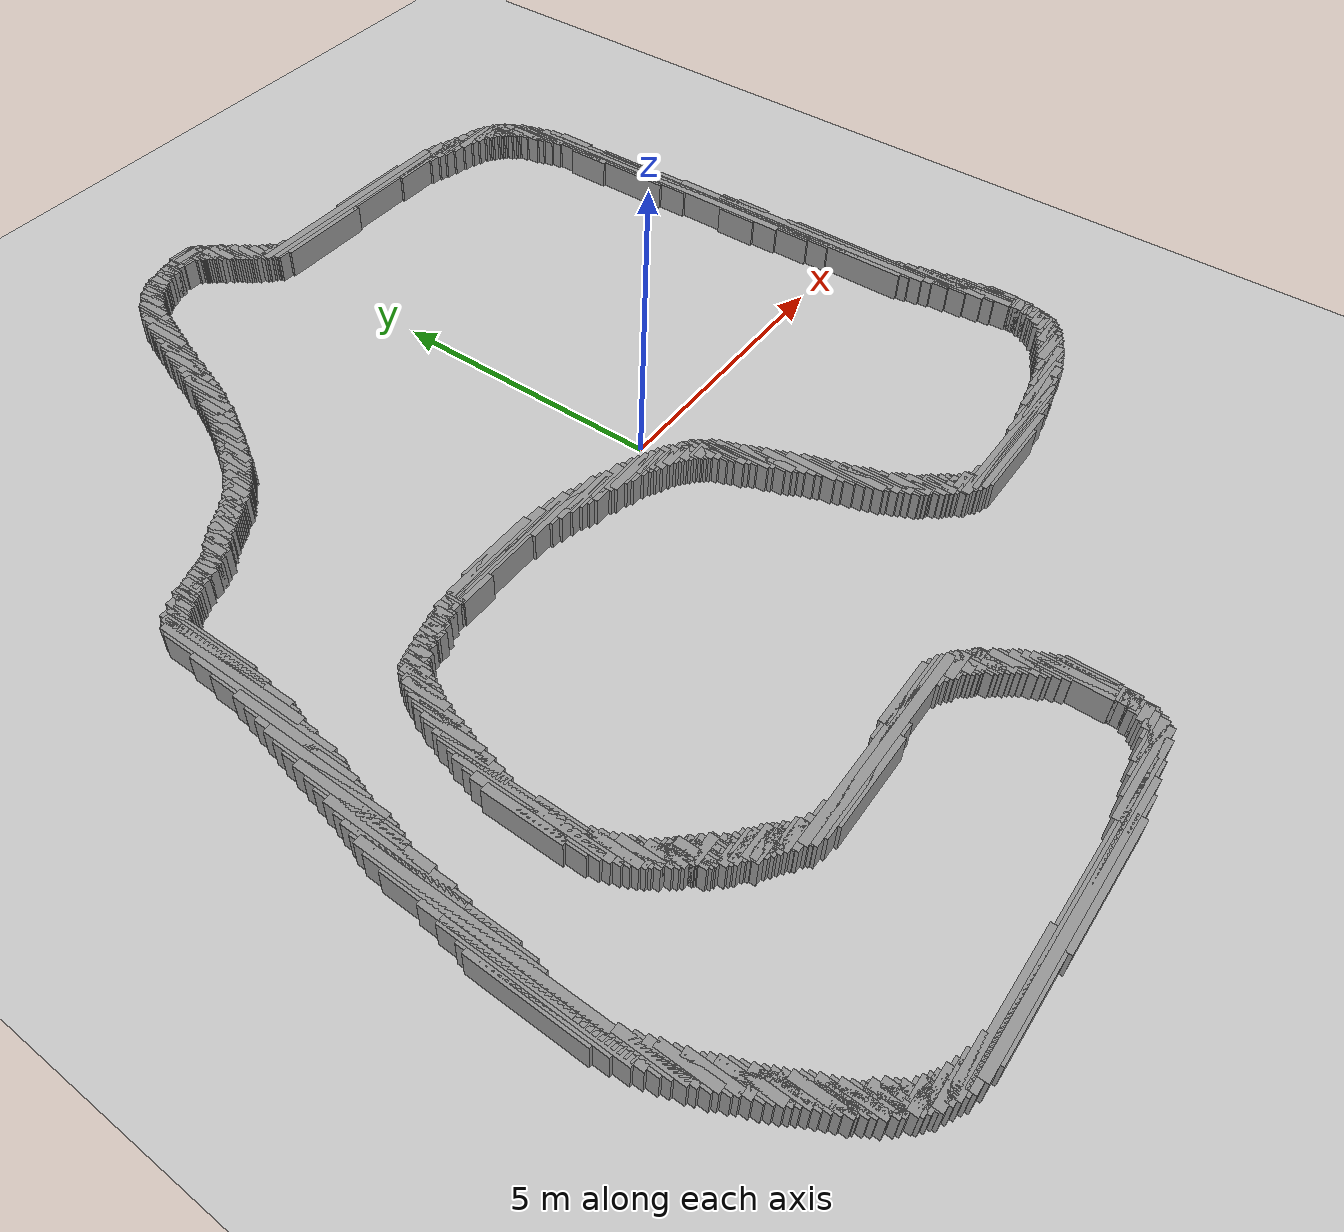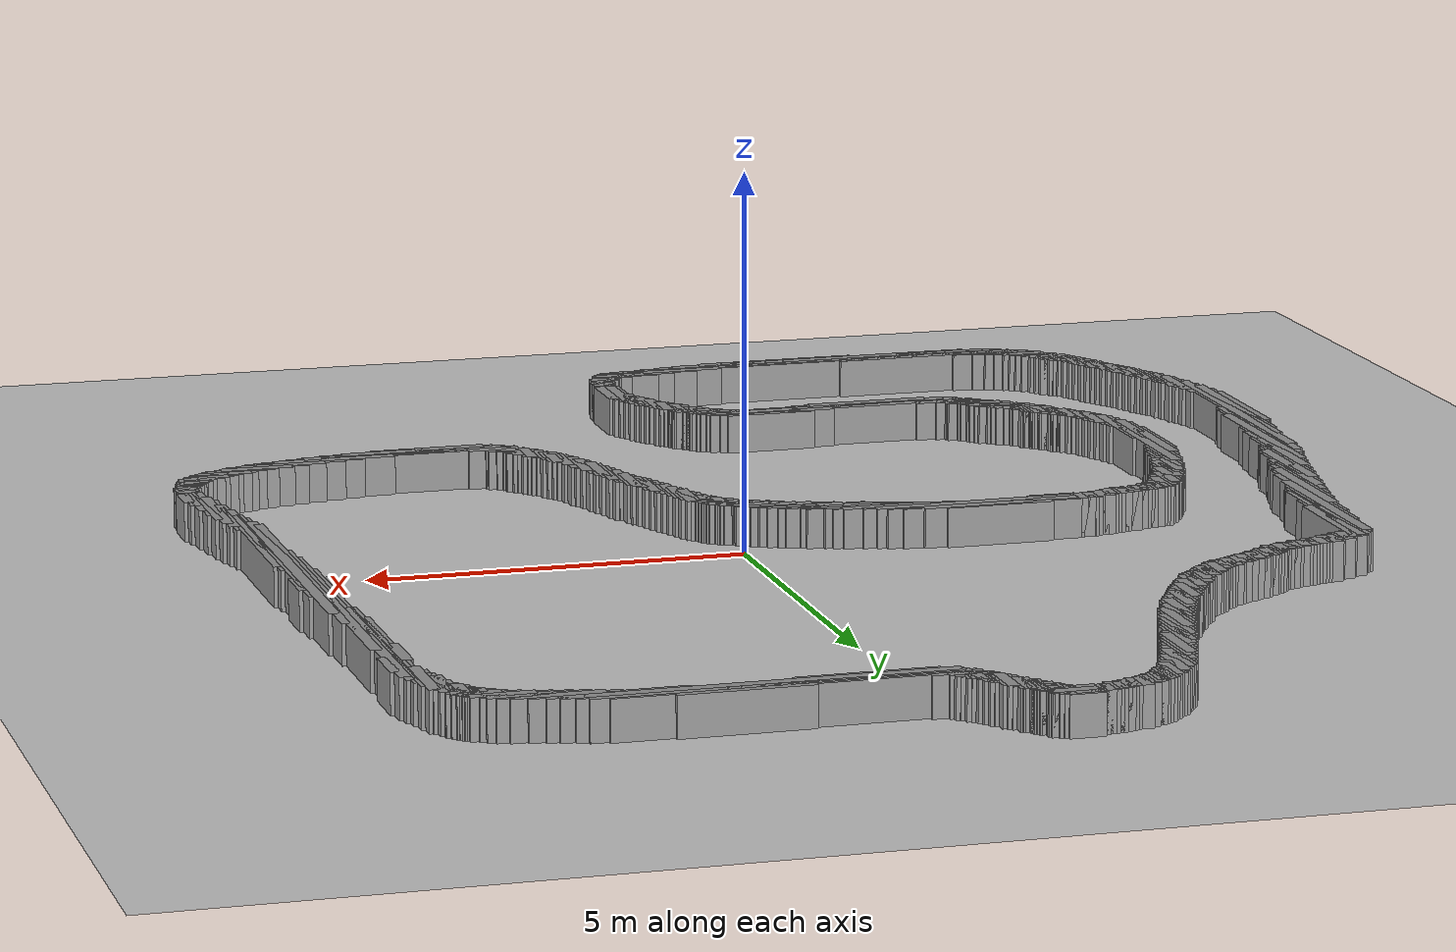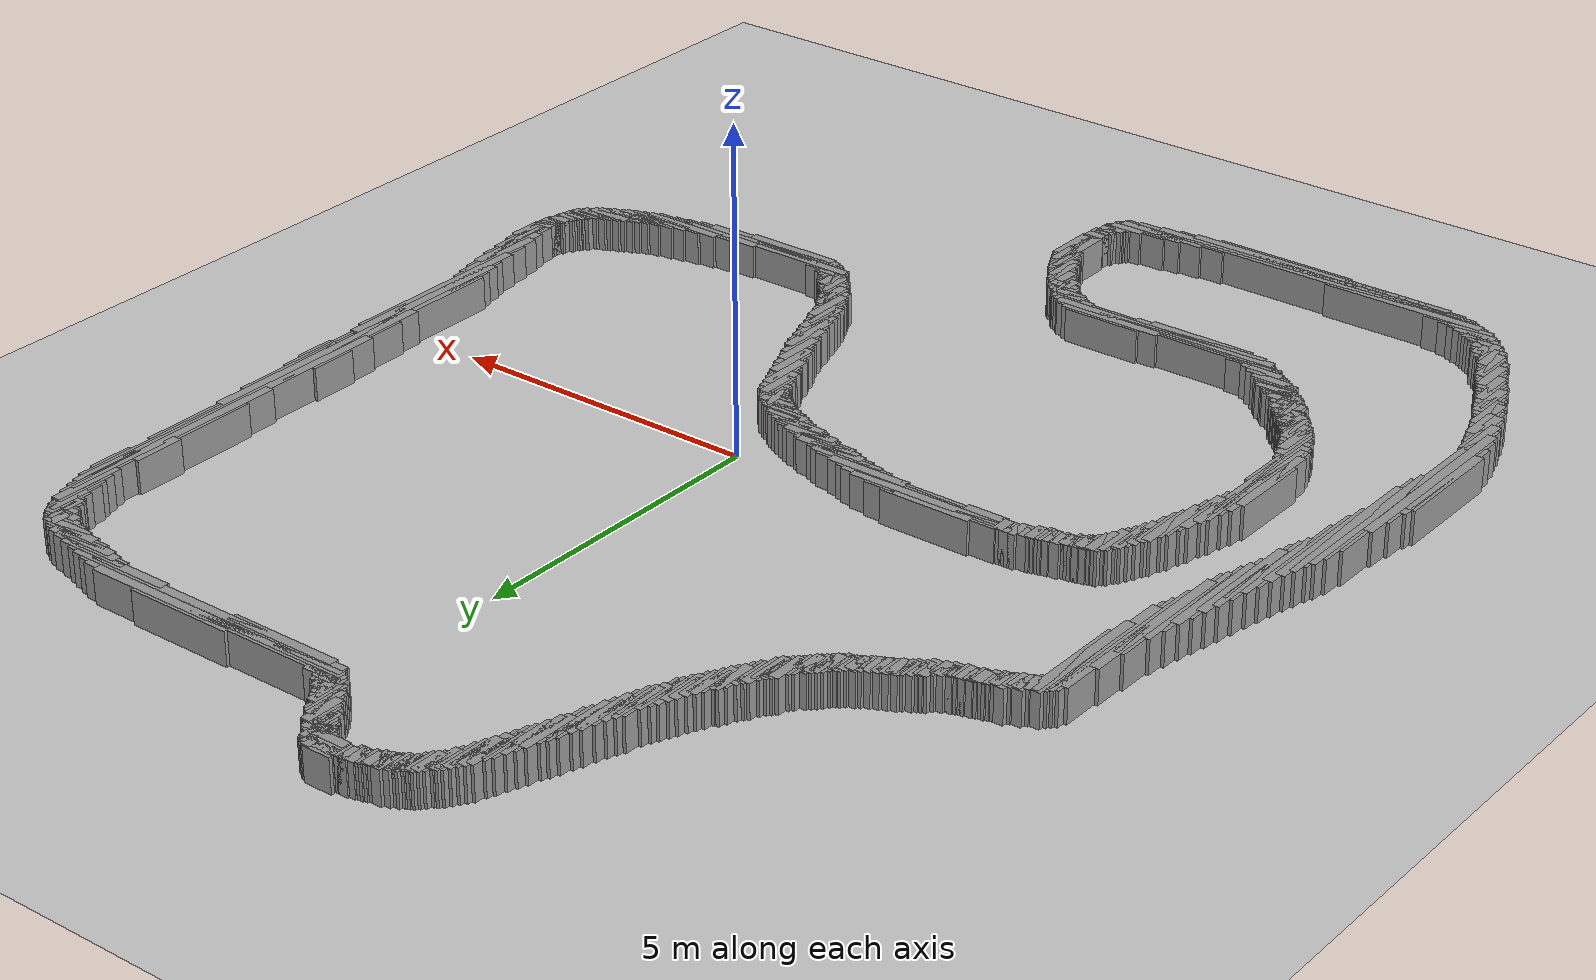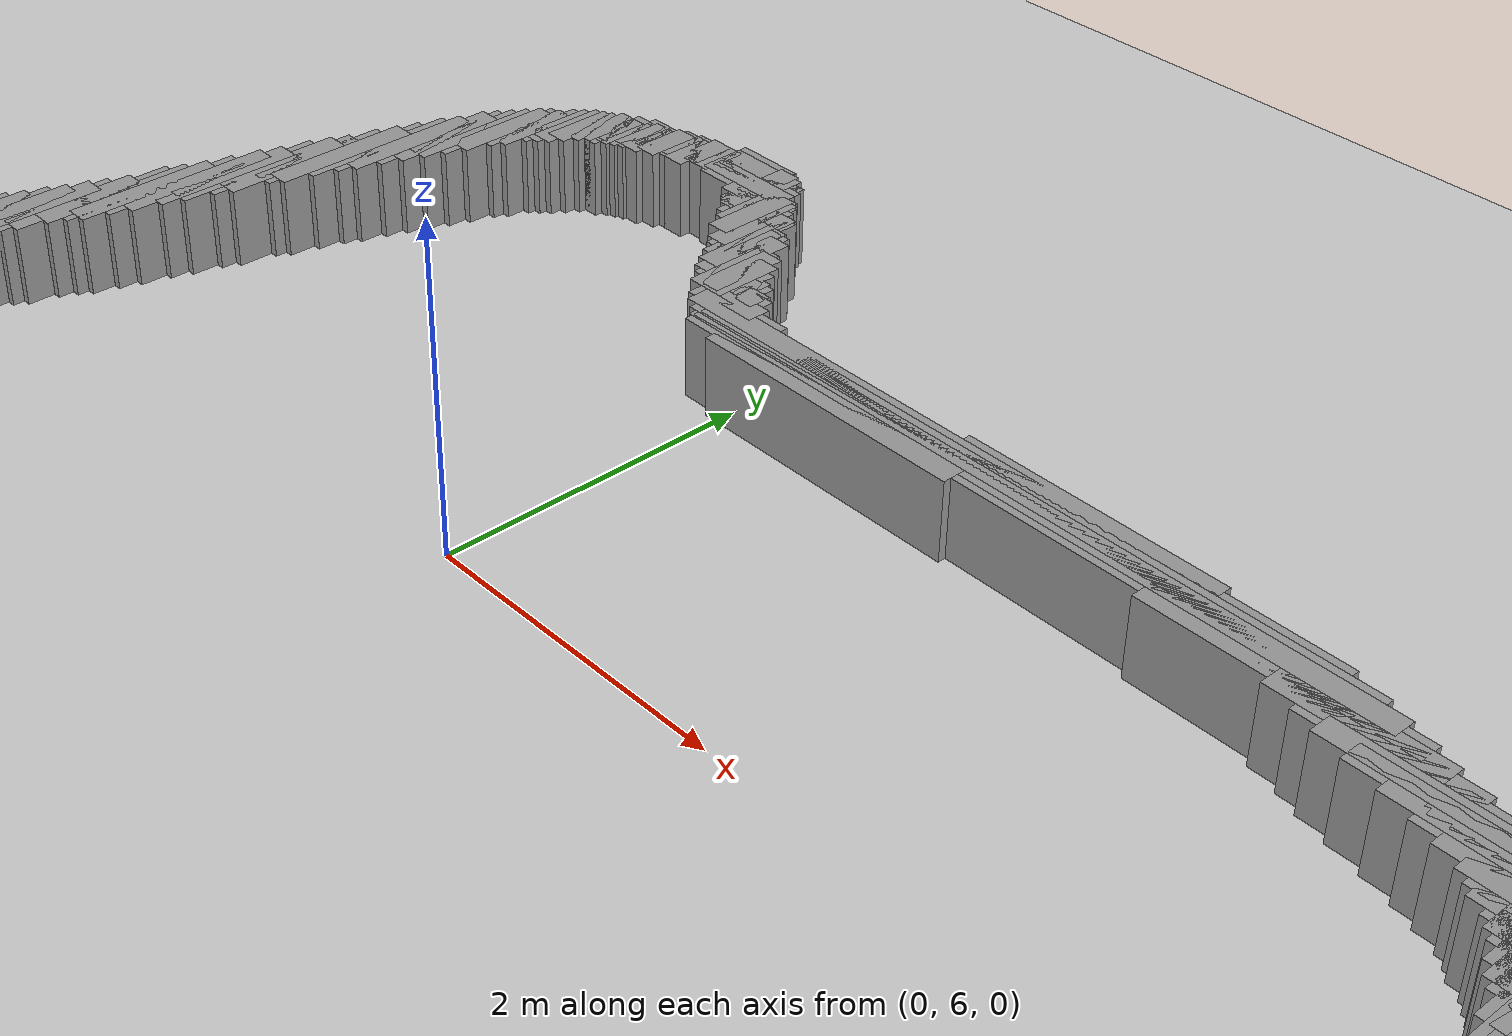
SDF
<sdf version="1.6">
  <world name="default">
    <include>
      <uri>model://sun</uri>
    </include>
    <include>
      <uri>model://ground_plane</uri>
    </include>
    <physics type="ode">
      <real_time_update_rate>1000.0</real_time_update_rate>
      <max_step_size>0.001</max_step_size>
      <real_time_factor>1</real_time_factor>
      <ode>
        <solver>
          <type>quick</type>
          <iters>150</iters>
          <precon_iters>0</precon_iters>
          <sor>1.400000</sor>
          <use_dynamic_moi_rescaling>1</use_dynamic_moi_rescaling>
        </solver>
        <constraints>
          <cfm>0.00001</cfm>
          <erp>0.2</erp>
          <contact_max_correcting_vel>2000.000000</contact_max_correcting_vel>
          <contact_surface_layer>0.01000</contact_surface_layer>
        </constraints>
      </ode>
    </physics>
    <scene>
      <ambient>0.4 0.4 0.4 1</ambient>
      <background>0.7 0.7 0.7 1</background>
      <shadows>true</shadows>
    </scene>
    <gui fullscreen="0">
      <camera name="user_camera">
        <pose>0.0 0.0 17.0 -1.5708 1.5708 0</pose>
        <view_controller>orbit</view_controller>
      </camera>
    </gui>
    <model name="obstacle">
      <static>1</static>
      <pose frame="">0 0 0 0 0 0</pose>
      <link name="obstacle">
        <collision name="obstacle_1">
          <pose>-3.1499999999999915 -9.299999999999997 0 0 0 0</pose>
          <geometry>
            <box>
              <size>2.3000000000000003 0.15 1.0</size>
            </box>
          </geometry>
        </collision>
        <visual name="obstacle_1">
          <pose>-3.1499999999999915 -9.299999999999997 0 0 0 0</pose>
          <geometry>
            <box>
              <size>2.3000000000000003 0.15 1.0</size>
            </box>
          </geometry>
          <material>
            <script>
              <uri>file://media/materials/scripts/gazebo.material</uri>
              <name>Gazebo/Grey</name>
            </script>
            <ambient>1 1 1 1</ambient>
          </material>
        </visual>
        <collision name="obstacle_2">
          <pose>-3.799999999999997 -9.25 0 0 0 0</pose>
          <geometry>
            <box>
              <size>4.4 0.15 1.0</size>
            </box>
          </geometry>
        </collision>
        <visual name="obstacle_2">
          <pose>-3.799999999999997 -9.25 0 0 0 0</pose>
          <geometry>
            <box>
              <size>4.4 0.15 1.0</size>
            </box>
          </geometry>
          <material>
            <script>
              <uri>file://media/materials/scripts/gazebo.material</uri>
              <name>Gazebo/Grey</name>
            </script>
            <ambient>1 1 1 1</ambient>
          </material>
        </visual>
        <collision name="obstacle_3">
          <pose>-3.799999999999997 -9.199999999999989 0 0 0 0</pose>
          <geometry>
            <box>
              <size>4.95 0.15 1.0</size>
            </box>
          </geometry>
        </collision>
        <visual name="obstacle_3">
          <pose>-3.799999999999997 -9.199999999999989 0 0 0 0</pose>
          <geometry>
            <box>
              <size>4.95 0.15 1.0</size>
            </box>
          </geometry>
          <material>
            <script>
              <uri>file://media/materials/scripts/gazebo.material</uri>
              <name>Gazebo/Grey</name>
            </script>
            <ambient>1 1 1 1</ambient>
          </material>
        </visual>
        <collision name="obstacle_4">
          <pose>-3.75 -9.149999999999991 0 0 0 0</pose>
          <geometry>
            <box>
              <size>5.45 0.15 1.0</size>
            </box>
          </geometry>
        </collision>
        <visual name="obstacle_4">
          <pose>-3.75 -9.149999999999991 0 0 0 0</pose>
          <geometry>
            <box>
              <size>5.45 0.15 1.0</size>
            </box>
          </geometry>
          <material>
            <script>
              <uri>file://media/materials/scripts/gazebo.material</uri>
              <name>Gazebo/Grey</name>
            </script>
            <ambient>1 1 1 1</ambient>
          </material>
        </visual>
        <collision name="obstacle_5">
          <pose>-3.5999999999999943 -9.099999999999994 0 0 0 0</pose>
          <geometry>
            <box>
              <size>5.9 0.15 1.0</size>
            </box>
          </geometry>
        </collision>
        <visual name="obstacle_5">
          <pose>-3.5999999999999943 -9.099999999999994 0 0 0 0</pose>
          <geometry>
            <box>
              <size>5.9 0.15 1.0</size>
            </box>
          </geometry>
          <material>
            <script>
              <uri>file://media/materials/scripts/gazebo.material</uri>
              <name>Gazebo/Grey</name>
            </script>
            <ambient>1 1 1 1</ambient>
          </material>
        </visual>
        <collision name="obstacle_6">
          <pose>-5.349999999999994 -9.049999999999997 0 0 0 0</pose>
          <geometry>
            <box>
              <size>2.6 0.15 1.0</size>
            </box>
          </geometry>
        </collision>
        <visual name="obstacle_6">
          <pose>-5.349999999999994 -9.049999999999997 0 0 0 0</pose>
          <geometry>
            <box>
              <size>2.6 0.15 1.0</size>
            </box>
          </geometry>
          <material>
            <script>
              <uri>file://media/materials/scripts/gazebo.material</uri>
              <name>Gazebo/Grey</name>
            </script>
            <ambient>1 1 1 1</ambient>
          </material>
        </visual>
        <collision name="obstacle_7">
          <pose>-1.3499999999999943 -9.049999999999997 0 0 0 0</pose>
          <geometry>
            <box>
              <size>1.8 0.15 1.0</size>
            </box>
          </geometry>
        </collision>
        <visual name="obstacle_7">
          <pose>-1.3499999999999943 -9.049999999999997 0 0 0 0</pose>
          <geometry>
            <box>
              <size>1.8 0.15 1.0</size>
            </box>
          </geometry>
          <material>
            <script>
              <uri>file://media/materials/scripts/gazebo.material</uri>
              <name>Gazebo/Grey</name>
            </script>
            <ambient>1 1 1 1</ambient>
          </material>
        </visual>
        <collision name="obstacle_8">
          <pose>-6.25 -9.0 0 0 0 0</pose>
          <geometry>
            <box>
              <size>1.0 0.15 1.0</size>
            </box>
          </geometry>
        </collision>
        <visual name="obstacle_8">
          <pose>-6.25 -9.0 0 0 0 0</pose>
          <geometry>
            <box>
              <size>1.0 0.15 1.0</size>
            </box>
          </geometry>
          <material>
            <script>
              <uri>file://media/materials/scripts/gazebo.material</uri>
              <name>Gazebo/Grey</name>
            </script>
            <ambient>1 1 1 1</ambient>
          </material>
        </visual>
        <collision name="obstacle_9">
          <pose>-1.1499999999999915 -9.0 0 0 0 0</pose>
          <geometry>
            <box>
              <size>1.4500000000000002 0.15 1.0</size>
            </box>
          </geometry>
        </collision>
        <visual name="obstacle_9">
          <pose>-1.1499999999999915 -9.0 0 0 0 0</pose>
          <geometry>
            <box>
              <size>1.4500000000000002 0.15 1.0</size>
            </box>
          </geometry>
          <material>
            <script>
              <uri>file://media/materials/scripts/gazebo.material</uri>
              <name>Gazebo/Grey</name>
            </script>
            <ambient>1 1 1 1</ambient>
          </material>
        </visual>
        <collision name="obstacle_10">
          <pose>-6.450000000000003 -8.949999999999989 0 0 0 0</pose>
          <geometry>
            <box>
              <size>0.8500000000000001 0.15 1.0</size>
            </box>
          </geometry>
        </collision>
        <visual name="obstacle_10">
          <pose>-6.450000000000003 -8.949999999999989 0 0 0 0</pose>
          <geometry>
            <box>
              <size>0.8500000000000001 0.15 1.0</size>
            </box>
          </geometry>
          <material>
            <script>
              <uri>file://media/materials/scripts/gazebo.material</uri>
              <name>Gazebo/Grey</name>
            </script>
            <ambient>1 1 1 1</ambient>
          </material>
        </visual>
        <collision name="obstacle_11">
          <pose>-0.9499999999999886 -8.949999999999989 0 0 0 0</pose>
          <geometry>
            <box>
              <size>1.1500000000000001 0.15 1.0</size>
            </box>
          </geometry>
        </collision>
        <visual name="obstacle_11">
          <pose>-0.9499999999999886 -8.949999999999989 0 0 0 0</pose>
          <geometry>
            <box>
              <size>1.1500000000000001 0.15 1.0</size>
            </box>
          </geometry>
          <material>
            <script>
              <uri>file://media/materials/scripts/gazebo.material</uri>
              <name>Gazebo/Grey</name>
            </script>
            <ambient>1 1 1 1</ambient>
          </material>
        </visual>
        <collision name="obstacle_12">
          <pose>-6.549999999999997 -8.899999999999991 0 0 0 0</pose>
          <geometry>
            <box>
              <size>0.7000000000000001 0.15 1.0</size>
            </box>
          </geometry>
        </collision>
        <visual name="obstacle_12">
          <pose>-6.549999999999997 -8.899999999999991 0 0 0 0</pose>
          <geometry>
            <box>
              <size>0.7000000000000001 0.15 1.0</size>
            </box>
          </geometry>
          <material>
            <script>
              <uri>file://media/materials/scripts/gazebo.material</uri>
              <name>Gazebo/Grey</name>
            </script>
            <ambient>1 1 1 1</ambient>
          </material>
        </visual>
        <collision name="obstacle_13">
          <pose>-0.7999999999999972 -8.899999999999991 0 0 0 0</pose>
          <geometry>
            <box>
              <size>0.9500000000000001 0.15 1.0</size>
            </box>
          </geometry>
        </collision>
        <visual name="obstacle_13">
          <pose>-0.7999999999999972 -8.899999999999991 0 0 0 0</pose>
          <geometry>
            <box>
              <size>0.9500000000000001 0.15 1.0</size>
            </box>
          </geometry>
          <material>
            <script>
              <uri>file://media/materials/scripts/gazebo.material</uri>
              <name>Gazebo/Grey</name>
            </script>
            <ambient>1 1 1 1</ambient>
          </material>
        </visual>
        <collision name="obstacle_14">
          <pose>-6.6499999999999915 -8.849999999999994 0 0 0 0</pose>
          <geometry>
            <box>
              <size>0.65 0.15 1.0</size>
            </box>
          </geometry>
        </collision>
        <visual name="obstacle_14">
          <pose>-6.6499999999999915 -8.849999999999994 0 0 0 0</pose>
          <geometry>
            <box>
              <size>0.65 0.15 1.0</size>
            </box>
          </geometry>
          <material>
            <script>
              <uri>file://media/materials/scripts/gazebo.material</uri>
              <name>Gazebo/Grey</name>
            </script>
            <ambient>1 1 1 1</ambient>
          </material>
        </visual>
        <collision name="obstacle_15">
          <pose>-0.5999999999999943 -8.849999999999994 0 0 0 0</pose>
          <geometry>
            <box>
              <size>0.55 0.15 1.0</size>
            </box>
          </geometry>
        </collision>
        <visual name="obstacle_15">
          <pose>-0.5999999999999943 -8.849999999999994 0 0 0 0</pose>
          <geometry>
            <box>
              <size>0.55 0.15 1.0</size>
            </box>
          </geometry>
          <material>
            <script>
              <uri>file://media/materials/scripts/gazebo.material</uri>
              <name>Gazebo/Grey</name>
            </script>
            <ambient>1 1 1 1</ambient>
          </material>
        </visual>
        <collision name="obstacle_16">
          <pose>-6.75 -8.799999999999997 0 0 0 0</pose>
          <geometry>
            <box>
              <size>0.6000000000000001 0.15 1.0</size>
            </box>
          </geometry>
        </collision>
        <visual name="obstacle_16">
          <pose>-6.75 -8.799999999999997 0 0 0 0</pose>
          <geometry>
            <box>
              <size>0.6000000000000001 0.15 1.0</size>
            </box>
          </geometry>
          <material>
            <script>
              <uri>file://media/materials/scripts/gazebo.material</uri>
              <name>Gazebo/Grey</name>
            </script>
            <ambient>1 1 1 1</ambient>
          </material>
        </visual>
        <collision name="obstacle_17">
          <pose>-0.5 -8.799999999999997 0 0 0 0</pose>
          <geometry>
            <box>
              <size>0.4 0.15 1.0</size>
            </box>
          </geometry>
        </collision>
        <visual name="obstacle_17">
          <pose>-0.5 -8.799999999999997 0 0 0 0</pose>
          <geometry>
            <box>
              <size>0.4 0.15 1.0</size>
            </box>
          </geometry>
          <material>
            <script>
              <uri>file://media/materials/scripts/gazebo.material</uri>
              <name>Gazebo/Grey</name>
            </script>
            <ambient>1 1 1 1</ambient>
          </material>
        </visual>
        <collision name="obstacle_18">
          <pose>-6.799999999999997 -8.75 0 0 0 0</pose>
          <geometry>
            <box>
              <size>0.55 0.15 1.0</size>
            </box>
          </geometry>
        </collision>
        <visual name="obstacle_18">
          <pose>-6.799999999999997 -8.75 0 0 0 0</pose>
          <geometry>
            <box>
              <size>0.55 0.15 1.0</size>
            </box>
          </geometry>
          <material>
            <script>
              <uri>file://media/materials/scripts/gazebo.material</uri>
              <name>Gazebo/Grey</name>
            </script>
            <ambient>1 1 1 1</ambient>
          </material>
        </visual>
        <collision name="obstacle_19">
          <pose>-0.44999999999998863 -8.75 0 0 0 0</pose>
          <geometry>
            <box>
              <size>0.4 0.15 1.0</size>
            </box>
          </geometry>
        </collision>
        <visual name="obstacle_19">
          <pose>-0.44999999999998863 -8.75 0 0 0 0</pose>
          <geometry>
            <box>
              <size>0.4 0.15 1.0</size>
            </box>
          </geometry>
          <material>
            <script>
              <uri>file://media/materials/scripts/gazebo.material</uri>
              <name>Gazebo/Grey</name>
            </script>
            <ambient>1 1 1 1</ambient>
          </material>
        </visual>
        <collision name="obstacle_20">
          <pose>-7.099999999999994 -8.449999999999989 0 0 0 1.5708</pose>
          <geometry>
            <box>
              <size>0.55 0.15 1.0</size>
            </box>
          </geometry>
        </collision>
        <visual name="obstacle_20">
          <pose>-7.099999999999994 -8.449999999999989 0 0 0 1.5708</pose>
          <geometry>
            <box>
              <size>0.55 0.15 1.0</size>
            </box>
          </geometry>
          <material>
            <script>
              <uri>file://media/materials/scripts/gazebo.material</uri>
              <name>Gazebo/Grey</name>
            </script>
            <ambient>1 1 1 1</ambient>
          </material>
        </visual>
        <collision name="obstacle_21">
          <pose>-7.049999999999997 -8.449999999999989 0 0 0 1.5708</pose>
          <geometry>
            <box>
              <size>0.5 0.15 1.0</size>
            </box>
          </geometry>
        </collision>
        <visual name="obstacle_21">
          <pose>-7.049999999999997 -8.449999999999989 0 0 0 1.5708</pose>
          <geometry>
            <box>
              <size>0.5 0.15 1.0</size>
            </box>
          </geometry>
          <material>
            <script>
              <uri>file://media/materials/scripts/gazebo.material</uri>
              <name>Gazebo/Grey</name>
            </script>
            <ambient>1 1 1 1</ambient>
          </material>
        </visual>
        <collision name="obstacle_22">
          <pose>-6.799999999999997 -8.699999999999989 0 0 0 0</pose>
          <geometry>
            <box>
              <size>0.4 0.15 1.0</size>
            </box>
          </geometry>
        </collision>
        <visual name="obstacle_22">
          <pose>-6.799999999999997 -8.699999999999989 0 0 0 0</pose>
          <geometry>
            <box>
              <size>0.4 0.15 1.0</size>
            </box>
          </geometry>
          <material>
            <script>
              <uri>file://media/materials/scripts/gazebo.material</uri>
              <name>Gazebo/Grey</name>
            </script>
            <ambient>1 1 1 1</ambient>
          </material>
        </visual>
        <collision name="obstacle_23">
          <pose>-0.44999999999998863 -8.699999999999989 0 0 0 0</pose>
          <geometry>
            <box>
              <size>0.35000000000000003 0.15 1.0</size>
            </box>
          </geometry>
        </collision>
        <visual name="obstacle_23">
          <pose>-0.44999999999998863 -8.699999999999989 0 0 0 0</pose>
          <geometry>
            <box>
              <size>0.35000000000000003 0.15 1.0</size>
            </box>
          </geometry>
          <material>
            <script>
              <uri>file://media/materials/scripts/gazebo.material</uri>
              <name>Gazebo/Grey</name>
            </script>
            <ambient>1 1 1 1</ambient>
          </material>
        </visual>
        <collision name="obstacle_24">
          <pose>-7.1499999999999915 -8.399999999999991 0 0 0 1.5708</pose>
          <geometry>
            <box>
              <size>0.55 0.15 1.0</size>
            </box>
          </geometry>
        </collision>
        <visual name="obstacle_24">
          <pose>-7.1499999999999915 -8.399999999999991 0 0 0 1.5708</pose>
          <geometry>
            <box>
              <size>0.55 0.15 1.0</size>
            </box>
          </geometry>
          <material>
            <script>
              <uri>file://media/materials/scripts/gazebo.material</uri>
              <name>Gazebo/Grey</name>
            </script>
            <ambient>1 1 1 1</ambient>
          </material>
        </visual>
        <collision name="obstacle_25">
          <pose>-6.849999999999994 -8.649999999999991 0 0 0 0</pose>
          <geometry>
            <box>
              <size>0.35000000000000003 0.15 1.0</size>
            </box>
          </geometry>
        </collision>
        <visual name="obstacle_25">
          <pose>-6.849999999999994 -8.649999999999991 0 0 0 0</pose>
          <geometry>
            <box>
              <size>0.35000000000000003 0.15 1.0</size>
            </box>
          </geometry>
          <material>
            <script>
              <uri>file://media/materials/scripts/gazebo.material</uri>
              <name>Gazebo/Grey</name>
            </script>
            <ambient>1 1 1 1</ambient>
          </material>
        </visual>
        <collision name="obstacle_26">
          <pose>-0.3999999999999915 -8.649999999999991 0 0 0 0</pose>
          <geometry>
            <box>
              <size>0.30000000000000004 0.15 1.0</size>
            </box>
          </geometry>
        </collision>
        <visual name="obstacle_26">
          <pose>-0.3999999999999915 -8.649999999999991 0 0 0 0</pose>
          <geometry>
            <box>
              <size>0.30000000000000004 0.15 1.0</size>
            </box>
          </geometry>
          <material>
            <script>
              <uri>file://media/materials/scripts/gazebo.material</uri>
              <name>Gazebo/Grey</name>
            </script>
            <ambient>1 1 1 1</ambient>
          </material>
        </visual>
        <collision name="obstacle_27">
          <pose>-7.0 -8.449999999999989 0 0 0 1.5708</pose>
          <geometry>
            <box>
              <size>0.30000000000000004 0.15 1.0</size>
            </box>
          </geometry>
        </collision>
        <visual name="obstacle_27">
          <pose>-7.0 -8.449999999999989 0 0 0 1.5708</pose>
          <geometry>
            <box>
              <size>0.30000000000000004 0.15 1.0</size>
            </box>
          </geometry>
          <material>
            <script>
              <uri>file://media/materials/scripts/gazebo.material</uri>
              <name>Gazebo/Grey</name>
            </script>
            <ambient>1 1 1 1</ambient>
          </material>
        </visual>
        <collision name="obstacle_28">
          <pose>-6.950000000000003 -8.449999999999989 0 0 0 1.5708</pose>
          <geometry>
            <box>
              <size>0.30000000000000004 0.15 1.0</size>
            </box>
          </geometry>
        </collision>
        <visual name="obstacle_28">
          <pose>-6.950000000000003 -8.449999999999989 0 0 0 1.5708</pose>
          <geometry>
            <box>
              <size>0.30000000000000004 0.15 1.0</size>
            </box>
          </geometry>
          <material>
            <script>
              <uri>file://media/materials/scripts/gazebo.material</uri>
              <name>Gazebo/Grey</name>
            </script>
            <ambient>1 1 1 1</ambient>
          </material>
        </visual>
        <collision name="obstacle_29">
          <pose>-6.8999999999999915 -8.5 0 0 0 1.5708</pose>
          <geometry>
            <box>
              <size>0.2 0.15 1.0</size>
            </box>
          </geometry>
        </collision>
        <visual name="obstacle_29">
          <pose>-6.8999999999999915 -8.5 0 0 0 1.5708</pose>
          <geometry>
            <box>
              <size>0.2 0.15 1.0</size>
            </box>
          </geometry>
          <material>
            <script>
              <uri>file://media/materials/scripts/gazebo.material</uri>
              <name>Gazebo/Grey</name>
            </script>
            <ambient>1 1 1 1</ambient>
          </material>
        </visual>
        <collision name="obstacle_30">
          <pose>-6.849999999999994 -8.549999999999997 0 0 0 1.5708</pose>
          <geometry>
            <box>
              <size>0.15000000000000002 0.15 1.0</size>
            </box>
          </geometry>
        </collision>
        <visual name="obstacle_30">
          <pose>-6.849999999999994 -8.549999999999997 0 0 0 1.5708</pose>
          <geometry>
            <box>
              <size>0.15000000000000002 0.15 1.0</size>
            </box>
          </geometry>
          <material>
            <script>
              <uri>file://media/materials/scripts/gazebo.material</uri>
              <name>Gazebo/Grey</name>
            </script>
            <ambient>1 1 1 1</ambient>
          </material>
        </visual>
        <collision name="obstacle_32">
          <pose>-0.3999999999999915 -8.599999999999994 0 0 0 0</pose>
          <geometry>
            <box>
              <size>0.30000000000000004 0.15 1.0</size>
            </box>
          </geometry>
        </collision>
        <visual name="obstacle_32">
          <pose>-0.3999999999999915 -8.599999999999994 0 0 0 0</pose>
          <geometry>
            <box>
              <size>0.30000000000000004 0.15 1.0</size>
            </box>
          </geometry>
          <material>
            <script>
              <uri>file://media/materials/scripts/gazebo.material</uri>
              <name>Gazebo/Grey</name>
            </script>
            <ambient>1 1 1 1</ambient>
          </material>
        </visual>
        <collision name="obstacle_33">
          <pose>-7.25 -8.25 0 0 0 1.5708</pose>
          <geometry>
            <box>
              <size>0.65 0.15 1.0</size>
            </box>
          </geometry>
        </collision>
        <visual name="obstacle_33">
          <pose>-7.25 -8.25 0 0 0 1.5708</pose>
          <geometry>
            <box>
              <size>0.65 0.15 1.0</size>
            </box>
          </geometry>
          <material>
            <script>
              <uri>file://media/materials/scripts/gazebo.material</uri>
              <name>Gazebo/Grey</name>
            </script>
            <ambient>1 1 1 1</ambient>
          </material>
        </visual>
        <collision name="obstacle_34">
          <pose>-7.200000000000003 -8.299999999999997 0 0 0 1.5708</pose>
          <geometry>
            <box>
              <size>0.55 0.15 1.0</size>
            </box>
          </geometry>
        </collision>
        <visual name="obstacle_34">
          <pose>-7.200000000000003 -8.299999999999997 0 0 0 1.5708</pose>
          <geometry>
            <box>
              <size>0.55 0.15 1.0</size>
            </box>
          </geometry>
          <material>
            <script>
              <uri>file://media/materials/scripts/gazebo.material</uri>
              <name>Gazebo/Grey</name>
            </script>
            <ambient>1 1 1 1</ambient>
          </material>
        </visual>
        <collision name="obstacle_35">
          <pose>-0.3999999999999915 -8.549999999999997 0 0 0 0</pose>
          <geometry>
            <box>
              <size>0.30000000000000004 0.15 1.0</size>
            </box>
          </geometry>
        </collision>
        <visual name="obstacle_35">
          <pose>-0.3999999999999915 -8.549999999999997 0 0 0 0</pose>
          <geometry>
            <box>
              <size>0.30000000000000004 0.15 1.0</size>
            </box>
          </geometry>
          <material>
            <script>
              <uri>file://media/materials/scripts/gazebo.material</uri>
              <name>Gazebo/Grey</name>
            </script>
            <ambient>1 1 1 1</ambient>
          </material>
        </visual>
        <collision name="obstacle_36">
          <pose>-0.3499999999999943 -8.5 0 0 0 0</pose>
          <geometry>
            <box>
              <size>0.30000000000000004 0.15 1.0</size>
            </box>
          </geometry>
        </collision>
        <visual name="obstacle_36">
          <pose>-0.3499999999999943 -8.5 0 0 0 0</pose>
          <geometry>
            <box>
              <size>0.30000000000000004 0.15 1.0</size>
            </box>
          </geometry>
          <material>
            <script>
              <uri>file://media/materials/scripts/gazebo.material</uri>
              <name>Gazebo/Grey</name>
            </script>
            <ambient>1 1 1 1</ambient>
          </material>
        </visual>
        <collision name="obstacle_37">
          <pose>-7.299999999999997 -8.149999999999991 0 0 0 1.5708</pose>
          <geometry>
            <box>
              <size>0.65 0.15 1.0</size>
            </box>
          </geometry>
        </collision>
        <visual name="obstacle_37">
          <pose>-7.299999999999997 -8.149999999999991 0 0 0 1.5708</pose>
          <geometry>
            <box>
              <size>0.65 0.15 1.0</size>
            </box>
          </geometry>
          <material>
            <script>
              <uri>file://media/materials/scripts/gazebo.material</uri>
              <name>Gazebo/Grey</name>
            </script>
            <ambient>1 1 1 1</ambient>
          </material>
        </visual>
        <collision name="obstacle_38">
          <pose>-0.3499999999999943 -8.449999999999989 0 0 0 0</pose>
          <geometry>
            <box>
              <size>0.30000000000000004 0.15 1.0</size>
            </box>
          </geometry>
        </collision>
        <visual name="obstacle_38">
          <pose>-0.3499999999999943 -8.449999999999989 0 0 0 0</pose>
          <geometry>
            <box>
              <size>0.30000000000000004 0.15 1.0</size>
            </box>
          </geometry>
          <material>
            <script>
              <uri>file://media/materials/scripts/gazebo.material</uri>
              <name>Gazebo/Grey</name>
            </script>
            <ambient>1 1 1 1</ambient>
          </material>
        </visual>
        <collision name="obstacle_39">
          <pose>-7.349999999999994 -8.049999999999997 0 0 0 1.5708</pose>
          <geometry>
            <box>
              <size>0.7000000000000001 0.15 1.0</size>
            </box>
          </geometry>
        </collision>
        <visual name="obstacle_39">
          <pose>-7.349999999999994 -8.049999999999997 0 0 0 1.5708</pose>
          <geometry>
            <box>
              <size>0.7000000000000001 0.15 1.0</size>
            </box>
          </geometry>
          <material>
            <script>
              <uri>file://media/materials/scripts/gazebo.material</uri>
              <name>Gazebo/Grey</name>
            </script>
            <ambient>1 1 1 1</ambient>
          </material>
        </visual>
        <collision name="obstacle_40">
          <pose>-0.3499999999999943 -8.399999999999991 0 0 0 0</pose>
          <geometry>
            <box>
              <size>0.30000000000000004 0.15 1.0</size>
            </box>
          </geometry>
        </collision>
        <visual name="obstacle_40">
          <pose>-0.3499999999999943 -8.399999999999991 0 0 0 0</pose>
          <geometry>
            <box>
              <size>0.30000000000000004 0.15 1.0</size>
            </box>
          </geometry>
          <material>
            <script>
              <uri>file://media/materials/scripts/gazebo.material</uri>
              <name>Gazebo/Grey</name>
            </script>
            <ambient>1 1 1 1</ambient>
          </material>
        </visual>
        <collision name="obstacle_41">
          <pose>-0.3499999999999943 -8.349999999999994 0 0 0 0</pose>
          <geometry>
            <box>
              <size>0.30000000000000004 0.15 1.0</size>
            </box>
          </geometry>
        </collision>
        <visual name="obstacle_41">
          <pose>-0.3499999999999943 -8.349999999999994 0 0 0 0</pose>
          <geometry>
            <box>
              <size>0.30000000000000004 0.15 1.0</size>
            </box>
          </geometry>
          <material>
            <script>
              <uri>file://media/materials/scripts/gazebo.material</uri>
              <name>Gazebo/Grey</name>
            </script>
            <ambient>1 1 1 1</ambient>
          </material>
        </visual>
        <collision name="obstacle_42">
          <pose>-7.3999999999999915 -7.949999999999989 0 0 0 1.5708</pose>
          <geometry>
            <box>
              <size>0.7000000000000001 0.15 1.0</size>
            </box>
          </geometry>
        </collision>
        <visual name="obstacle_42">
          <pose>-7.3999999999999915 -7.949999999999989 0 0 0 1.5708</pose>
          <geometry>
            <box>
              <size>0.7000000000000001 0.15 1.0</size>
            </box>
          </geometry>
          <material>
            <script>
              <uri>file://media/materials/scripts/gazebo.material</uri>
              <name>Gazebo/Grey</name>
            </script>
            <ambient>1 1 1 1</ambient>
          </material>
        </visual>
        <collision name="obstacle_43">
          <pose>-0.3499999999999943 -8.299999999999997 0 0 0 0</pose>
          <geometry>
            <box>
              <size>0.30000000000000004 0.15 1.0</size>
            </box>
          </geometry>
        </collision>
        <visual name="obstacle_43">
          <pose>-0.3499999999999943 -8.299999999999997 0 0 0 0</pose>
          <geometry>
            <box>
              <size>0.30000000000000004 0.15 1.0</size>
            </box>
          </geometry>
          <material>
            <script>
              <uri>file://media/materials/scripts/gazebo.material</uri>
              <name>Gazebo/Grey</name>
            </script>
            <ambient>1 1 1 1</ambient>
          </material>
        </visual>
        <collision name="obstacle_44">
          <pose>-7.450000000000003 -7.8999999999999915 0 0 0 1.5708</pose>
          <geometry>
            <box>
              <size>0.75 0.15 1.0</size>
            </box>
          </geometry>
        </collision>
        <visual name="obstacle_44">
          <pose>-7.450000000000003 -7.8999999999999915 0 0 0 1.5708</pose>
          <geometry>
            <box>
              <size>0.75 0.15 1.0</size>
            </box>
          </geometry>
          <material>
            <script>
              <uri>file://media/materials/scripts/gazebo.material</uri>
              <name>Gazebo/Grey</name>
            </script>
            <ambient>1 1 1 1</ambient>
          </material>
        </visual>
        <collision name="obstacle_45">
          <pose>-0.44999999999998863 -7.6499999999999915 0 0 0 1.5708</pose>
          <geometry>
            <box>
              <size>1.25 0.15 1.0</size>
            </box>
          </geometry>
        </collision>
        <visual name="obstacle_45">
          <pose>-0.44999999999998863 -7.6499999999999915 0 0 0 1.5708</pose>
          <geometry>
            <box>
              <size>1.25 0.15 1.0</size>
            </box>
          </geometry>
          <material>
            <script>
              <uri>file://media/materials/scripts/gazebo.material</uri>
              <name>Gazebo/Grey</name>
            </script>
            <ambient>1 1 1 1</ambient>
          </material>
        </visual>
        <collision name="obstacle_46">
          <pose>-0.3999999999999915 -7.699999999999989 0 0 0 1.5708</pose>
          <geometry>
            <box>
              <size>1.1500000000000001 0.15 1.0</size>
            </box>
          </geometry>
        </collision>
        <visual name="obstacle_46">
          <pose>-0.3999999999999915 -7.699999999999989 0 0 0 1.5708</pose>
          <geometry>
            <box>
              <size>1.1500000000000001 0.15 1.0</size>
            </box>
          </geometry>
          <material>
            <script>
              <uri>file://media/materials/scripts/gazebo.material</uri>
              <name>Gazebo/Grey</name>
            </script>
            <ambient>1 1 1 1</ambient>
          </material>
        </visual>
        <collision name="obstacle_47">
          <pose>-0.3499999999999943 -7.75 0 0 0 1.5708</pose>
          <geometry>
            <box>
              <size>1.05 0.15 1.0</size>
            </box>
          </geometry>
        </collision>
        <visual name="obstacle_47">
          <pose>-0.3499999999999943 -7.75 0 0 0 1.5708</pose>
          <geometry>
            <box>
              <size>1.05 0.15 1.0</size>
            </box>
          </geometry>
          <material>
            <script>
              <uri>file://media/materials/scripts/gazebo.material</uri>
              <name>Gazebo/Grey</name>
            </script>
            <ambient>1 1 1 1</ambient>
          </material>
        </visual>
        <collision name="obstacle_48">
          <pose>-0.29999999999999716 -7.799999999999997 0 0 0 1.5708</pose>
          <geometry>
            <box>
              <size>0.9500000000000001 0.15 1.0</size>
            </box>
          </geometry>
        </collision>
        <visual name="obstacle_48">
          <pose>-0.29999999999999716 -7.799999999999997 0 0 0 1.5708</pose>
          <geometry>
            <box>
              <size>0.9500000000000001 0.15 1.0</size>
            </box>
          </geometry>
          <material>
            <script>
              <uri>file://media/materials/scripts/gazebo.material</uri>
              <name>Gazebo/Grey</name>
            </script>
            <ambient>1 1 1 1</ambient>
          </material>
        </visual>
        <collision name="obstacle_49">
          <pose>-0.25 -7.849999999999994 0 0 0 1.5708</pose>
          <geometry>
            <box>
              <size>0.8500000000000001 0.15 1.0</size>
            </box>
          </geometry>
        </collision>
        <visual name="obstacle_49">
          <pose>-0.25 -7.849999999999994 0 0 0 1.5708</pose>
          <geometry>
            <box>
              <size>0.8500000000000001 0.15 1.0</size>
            </box>
          </geometry>
          <material>
            <script>
              <uri>file://media/materials/scripts/gazebo.material</uri>
              <name>Gazebo/Grey</name>
            </script>
            <ambient>1 1 1 1</ambient>
          </material>
        </visual>
        <collision name="obstacle_50">
          <pose>-7.5 -7.799999999999997 0 0 0 1.5708</pose>
          <geometry>
            <box>
              <size>0.7000000000000001 0.15 1.0</size>
            </box>
          </geometry>
        </collision>
        <visual name="obstacle_50">
          <pose>-7.5 -7.799999999999997 0 0 0 1.5708</pose>
          <geometry>
            <box>
              <size>0.7000000000000001 0.15 1.0</size>
            </box>
          </geometry>
          <material>
            <script>
              <uri>file://media/materials/scripts/gazebo.material</uri>
              <name>Gazebo/Grey</name>
            </script>
            <ambient>1 1 1 1</ambient>
          </material>
        </visual>
        <collision name="obstacle_51">
          <pose>-7.549999999999997 -7.699999999999989 0 0 0 1.5708</pose>
          <geometry>
            <box>
              <size>0.7000000000000001 0.15 1.0</size>
            </box>
          </geometry>
        </collision>
        <visual name="obstacle_51">
          <pose>-7.549999999999997 -7.699999999999989 0 0 0 1.5708</pose>
          <geometry>
            <box>
              <size>0.7000000000000001 0.15 1.0</size>
            </box>
          </geometry>
          <material>
            <script>
              <uri>file://media/materials/scripts/gazebo.material</uri>
              <name>Gazebo/Grey</name>
            </script>
            <ambient>1 1 1 1</ambient>
          </material>
        </visual>
        <collision name="obstacle_52">
          <pose>-7.599999999999994 -7.599999999999994 0 0 0 1.5708</pose>
          <geometry>
            <box>
              <size>0.7000000000000001 0.15 1.0</size>
            </box>
          </geometry>
        </collision>
        <visual name="obstacle_52">
          <pose>-7.599999999999994 -7.599999999999994 0 0 0 1.5708</pose>
          <geometry>
            <box>
              <size>0.7000000000000001 0.15 1.0</size>
            </box>
          </geometry>
          <material>
            <script>
              <uri>file://media/materials/scripts/gazebo.material</uri>
              <name>Gazebo/Grey</name>
            </script>
            <ambient>1 1 1 1</ambient>
          </material>
        </visual>
        <collision name="obstacle_53">
          <pose>-7.6499999999999915 -7.5 0 0 0 1.5708</pose>
          <geometry>
            <box>
              <size>0.7000000000000001 0.15 1.0</size>
            </box>
          </geometry>
        </collision>
        <visual name="obstacle_53">
          <pose>-7.6499999999999915 -7.5 0 0 0 1.5708</pose>
          <geometry>
            <box>
              <size>0.7000000000000001 0.15 1.0</size>
            </box>
          </geometry>
          <material>
            <script>
              <uri>file://media/materials/scripts/gazebo.material</uri>
              <name>Gazebo/Grey</name>
            </script>
            <ambient>1 1 1 1</ambient>
          </material>
        </visual>
        <collision name="obstacle_54">
          <pose>-7.700000000000003 -7.3999999999999915 0 0 0 1.5708</pose>
          <geometry>
            <box>
              <size>0.7000000000000001 0.15 1.0</size>
            </box>
          </geometry>
        </collision>
        <visual name="obstacle_54">
          <pose>-7.700000000000003 -7.3999999999999915 0 0 0 1.5708</pose>
          <geometry>
            <box>
              <size>0.7000000000000001 0.15 1.0</size>
            </box>
          </geometry>
          <material>
            <script>
              <uri>file://media/materials/scripts/gazebo.material</uri>
              <name>Gazebo/Grey</name>
            </script>
            <ambient>1 1 1 1</ambient>
          </material>
        </visual>
        <collision name="obstacle_55">
          <pose>-7.75 -7.299999999999997 0 0 0 1.5708</pose>
          <geometry>
            <box>
              <size>0.75 0.15 1.0</size>
            </box>
          </geometry>
        </collision>
        <visual name="obstacle_55">
          <pose>-7.75 -7.299999999999997 0 0 0 1.5708</pose>
          <geometry>
            <box>
              <size>0.75 0.15 1.0</size>
            </box>
          </geometry>
          <material>
            <script>
              <uri>file://media/materials/scripts/gazebo.material</uri>
              <name>Gazebo/Grey</name>
            </script>
            <ambient>1 1 1 1</ambient>
          </material>
        </visual>
        <collision name="obstacle_56">
          <pose>-0.5 -7.299999999999997 0 0 0 1.5708</pose>
          <geometry>
            <box>
              <size>0.75 0.15 1.0</size>
            </box>
          </geometry>
        </collision>
        <visual name="obstacle_56">
          <pose>-0.5 -7.299999999999997 0 0 0 1.5708</pose>
          <geometry>
            <box>
              <size>0.75 0.15 1.0</size>
            </box>
          </geometry>
          <material>
            <script>
              <uri>file://media/materials/scripts/gazebo.material</uri>
              <name>Gazebo/Grey</name>
            </script>
            <ambient>1 1 1 1</ambient>
          </material>
        </visual>
        <collision name="obstacle_57">
          <pose>-7.799999999999997 -7.199999999999989 0 0 0 1.5708</pose>
          <geometry>
            <box>
              <size>0.8 0.15 1.0</size>
            </box>
          </geometry>
        </collision>
        <visual name="obstacle_57">
          <pose>-7.799999999999997 -7.199999999999989 0 0 0 1.5708</pose>
          <geometry>
            <box>
              <size>0.8 0.15 1.0</size>
            </box>
          </geometry>
          <material>
            <script>
              <uri>file://media/materials/scripts/gazebo.material</uri>
              <name>Gazebo/Grey</name>
            </script>
            <ambient>1 1 1 1</ambient>
          </material>
        </visual>
        <collision name="obstacle_58">
          <pose>-0.5499999999999972 -7.199999999999989 0 0 0 1.5708</pose>
          <geometry>
            <box>
              <size>0.7000000000000001 0.15 1.0</size>
            </box>
          </geometry>
        </collision>
        <visual name="obstacle_58">
          <pose>-0.5499999999999972 -7.199999999999989 0 0 0 1.5708</pose>
          <geometry>
            <box>
              <size>0.7000000000000001 0.15 1.0</size>
            </box>
          </geometry>
          <material>
            <script>
              <uri>file://media/materials/scripts/gazebo.material</uri>
              <name>Gazebo/Grey</name>
            </script>
            <ambient>1 1 1 1</ambient>
          </material>
        </visual>
        <collision name="obstacle_59">
          <pose>-7.849999999999994 -7.099999999999994 0 0 0 1.5708</pose>
          <geometry>
            <box>
              <size>0.8 0.15 1.0</size>
            </box>
          </geometry>
        </collision>
        <visual name="obstacle_59">
          <pose>-7.849999999999994 -7.099999999999994 0 0 0 1.5708</pose>
          <geometry>
            <box>
              <size>0.8 0.15 1.0</size>
            </box>
          </geometry>
          <material>
            <script>
              <uri>file://media/materials/scripts/gazebo.material</uri>
              <name>Gazebo/Grey</name>
            </script>
            <ambient>1 1 1 1</ambient>
          </material>
        </visual>
        <collision name="obstacle_60">
          <pose>-7.8999999999999915 -7.0 0 0 0 1.5708</pose>
          <geometry>
            <box>
              <size>0.8 0.15 1.0</size>
            </box>
          </geometry>
        </collision>
        <visual name="obstacle_60">
          <pose>-7.8999999999999915 -7.0 0 0 0 1.5708</pose>
          <geometry>
            <box>
              <size>0.8 0.15 1.0</size>
            </box>
          </geometry>
          <material>
            <script>
              <uri>file://media/materials/scripts/gazebo.material</uri>
              <name>Gazebo/Grey</name>
            </script>
            <ambient>1 1 1 1</ambient>
          </material>
        </visual>
        <collision name="obstacle_61">
          <pose>-0.5999999999999943 -7.099999999999994 0 0 0 1.5708</pose>
          <geometry>
            <box>
              <size>0.65 0.15 1.0</size>
            </box>
          </geometry>
        </collision>
        <visual name="obstacle_61">
          <pose>-0.5999999999999943 -7.099999999999994 0 0 0 1.5708</pose>
          <geometry>
            <box>
              <size>0.65 0.15 1.0</size>
            </box>
          </geometry>
          <material>
            <script>
              <uri>file://media/materials/scripts/gazebo.material</uri>
              <name>Gazebo/Grey</name>
            </script>
            <ambient>1 1 1 1</ambient>
          </material>
        </visual>
        <collision name="obstacle_62">
          <pose>-0.6499999999999915 -7.049999999999997 0 0 0 1.5708</pose>
          <geometry>
            <box>
              <size>0.65 0.15 1.0</size>
            </box>
          </geometry>
        </collision>
        <visual name="obstacle_62">
          <pose>-0.6499999999999915 -7.049999999999997 0 0 0 1.5708</pose>
          <geometry>
            <box>
              <size>0.65 0.15 1.0</size>
            </box>
          </geometry>
          <material>
            <script>
              <uri>file://media/materials/scripts/gazebo.material</uri>
              <name>Gazebo/Grey</name>
            </script>
            <ambient>1 1 1 1</ambient>
          </material>
        </visual>
        <collision name="obstacle_63">
          <pose>-7.950000000000003 -6.8999999999999915 0 0 0 1.5708</pose>
          <geometry>
            <box>
              <size>0.75 0.15 1.0</size>
            </box>
          </geometry>
        </collision>
        <visual name="obstacle_63">
          <pose>-7.950000000000003 -6.8999999999999915 0 0 0 1.5708</pose>
          <geometry>
            <box>
              <size>0.75 0.15 1.0</size>
            </box>
          </geometry>
          <material>
            <script>
              <uri>file://media/materials/scripts/gazebo.material</uri>
              <name>Gazebo/Grey</name>
            </script>
            <ambient>1 1 1 1</ambient>
          </material>
        </visual>
        <collision name="obstacle_64">
          <pose>-0.6999999999999886 -6.949999999999989 0 0 0 1.5708</pose>
          <geometry>
            <box>
              <size>0.65 0.15 1.0</size>
            </box>
          </geometry>
        </collision>
        <visual name="obstacle_64">
          <pose>-0.6999999999999886 -6.949999999999989 0 0 0 1.5708</pose>
          <geometry>
            <box>
              <size>0.65 0.15 1.0</size>
            </box>
          </geometry>
          <material>
            <script>
              <uri>file://media/materials/scripts/gazebo.material</uri>
              <name>Gazebo/Grey</name>
            </script>
            <ambient>1 1 1 1</ambient>
          </material>
        </visual>
        <collision name="obstacle_65">
          <pose>-8.0 -6.75 0 0 0 1.5708</pose>
          <geometry>
            <box>
              <size>0.8 0.15 1.0</size>
            </box>
          </geometry>
        </collision>
        <visual name="obstacle_65">
          <pose>-8.0 -6.75 0 0 0 1.5708</pose>
          <geometry>
            <box>
              <size>0.8 0.15 1.0</size>
            </box>
          </geometry>
          <material>
            <script>
              <uri>file://media/materials/scripts/gazebo.material</uri>
              <name>Gazebo/Grey</name>
            </script>
            <ambient>1 1 1 1</ambient>
          </material>
        </visual>
        <collision name="obstacle_66">
          <pose>-0.75 -6.849999999999994 0 0 0 1.5708</pose>
          <geometry>
            <box>
              <size>0.6000000000000001 0.15 1.0</size>
            </box>
          </geometry>
        </collision>
        <visual name="obstacle_66">
          <pose>-0.75 -6.849999999999994 0 0 0 1.5708</pose>
          <geometry>
            <box>
              <size>0.6000000000000001 0.15 1.0</size>
            </box>
          </geometry>
          <material>
            <script>
              <uri>file://media/materials/scripts/gazebo.material</uri>
              <name>Gazebo/Grey</name>
            </script>
            <ambient>1 1 1 1</ambient>
          </material>
        </visual>
        <collision name="obstacle_67">
          <pose>-8.049999999999997 -6.6499999999999915 0 0 0 1.5708</pose>
          <geometry>
            <box>
              <size>0.8500000000000001 0.15 1.0</size>
            </box>
          </geometry>
        </collision>
        <visual name="obstacle_67">
          <pose>-8.049999999999997 -6.6499999999999915 0 0 0 1.5708</pose>
          <geometry>
            <box>
              <size>0.8500000000000001 0.15 1.0</size>
            </box>
          </geometry>
          <material>
            <script>
              <uri>file://media/materials/scripts/gazebo.material</uri>
              <name>Gazebo/Grey</name>
            </script>
            <ambient>1 1 1 1</ambient>
          </material>
        </visual>
        <collision name="obstacle_68">
          <pose>-0.7999999999999972 -6.799999999999997 0 0 0 1.5708</pose>
          <geometry>
            <box>
              <size>0.55 0.15 1.0</size>
            </box>
          </geometry>
        </collision>
        <visual name="obstacle_68">
          <pose>-0.7999999999999972 -6.799999999999997 0 0 0 1.5708</pose>
          <geometry>
            <box>
              <size>0.55 0.15 1.0</size>
            </box>
          </geometry>
          <material>
            <script>
              <uri>file://media/materials/scripts/gazebo.material</uri>
              <name>Gazebo/Grey</name>
            </script>
            <ambient>1 1 1 1</ambient>
          </material>
        </visual>
        <collision name="obstacle_69">
          <pose>-0.8499999999999943 -6.699999999999989 0 0 0 1.5708</pose>
          <geometry>
            <box>
              <size>0.6000000000000001 0.15 1.0</size>
            </box>
          </geometry>
        </collision>
        <visual name="obstacle_69">
          <pose>-0.8499999999999943 -6.699999999999989 0 0 0 1.5708</pose>
          <geometry>
            <box>
              <size>0.6000000000000001 0.15 1.0</size>
            </box>
          </geometry>
          <material>
            <script>
              <uri>file://media/materials/scripts/gazebo.material</uri>
              <name>Gazebo/Grey</name>
            </script>
            <ambient>1 1 1 1</ambient>
          </material>
        </visual>
        <collision name="obstacle_70">
          <pose>-8.099999999999994 -6.5 0 0 0 1.5708</pose>
          <geometry>
            <box>
              <size>0.9 0.15 1.0</size>
            </box>
          </geometry>
        </collision>
        <visual name="obstacle_70">
          <pose>-8.099999999999994 -6.5 0 0 0 1.5708</pose>
          <geometry>
            <box>
              <size>0.9 0.15 1.0</size>
            </box>
          </geometry>
          <material>
            <script>
              <uri>file://media/materials/scripts/gazebo.material</uri>
              <name>Gazebo/Grey</name>
            </script>
            <ambient>1 1 1 1</ambient>
          </material>
        </visual>
        <collision name="obstacle_71">
          <pose>-0.8999999999999915 -6.6499999999999915 0 0 0 1.5708</pose>
          <geometry>
            <box>
              <size>0.6000000000000001 0.15 1.0</size>
            </box>
          </geometry>
        </collision>
        <visual name="obstacle_71">
          <pose>-0.8999999999999915 -6.6499999999999915 0 0 0 1.5708</pose>
          <geometry>
            <box>
              <size>0.6000000000000001 0.15 1.0</size>
            </box>
          </geometry>
          <material>
            <script>
              <uri>file://media/materials/scripts/gazebo.material</uri>
              <name>Gazebo/Grey</name>
            </script>
            <ambient>1 1 1 1</ambient>
          </material>
        </visual>
        <collision name="obstacle_72">
          <pose>-8.149999999999991 -6.3999999999999915 0 0 0 1.5708</pose>
          <geometry>
            <box>
              <size>0.9500000000000001 0.15 1.0</size>
            </box>
          </geometry>
        </collision>
        <visual name="obstacle_72">
          <pose>-8.149999999999991 -6.3999999999999915 0 0 0 1.5708</pose>
          <geometry>
            <box>
              <size>0.9500000000000001 0.15 1.0</size>
            </box>
          </geometry>
          <material>
            <script>
              <uri>file://media/materials/scripts/gazebo.material</uri>
              <name>Gazebo/Grey</name>
            </script>
            <ambient>1 1 1 1</ambient>
          </material>
        </visual>
        <collision name="obstacle_73">
          <pose>-0.9499999999999886 -6.599999999999994 0 0 0 1.5708</pose>
          <geometry>
            <box>
              <size>0.55 0.15 1.0</size>
            </box>
          </geometry>
        </collision>
        <visual name="obstacle_73">
          <pose>-0.9499999999999886 -6.599999999999994 0 0 0 1.5708</pose>
          <geometry>
            <box>
              <size>0.55 0.15 1.0</size>
            </box>
          </geometry>
          <material>
            <script>
              <uri>file://media/materials/scripts/gazebo.material</uri>
              <name>Gazebo/Grey</name>
            </script>
            <ambient>1 1 1 1</ambient>
          </material>
        </visual>
        <collision name="obstacle_74">
          <pose>-1.0 -6.549999999999997 0 0 0 1.5708</pose>
          <geometry>
            <box>
              <size>0.55 0.15 1.0</size>
            </box>
          </geometry>
        </collision>
        <visual name="obstacle_74">
          <pose>-1.0 -6.549999999999997 0 0 0 1.5708</pose>
          <geometry>
            <box>
              <size>0.55 0.15 1.0</size>
            </box>
          </geometry>
          <material>
            <script>
              <uri>file://media/materials/scripts/gazebo.material</uri>
              <name>Gazebo/Grey</name>
            </script>
            <ambient>1 1 1 1</ambient>
          </material>
        </visual>
        <collision name="obstacle_75">
          <pose>-1.0499999999999972 -6.5 0 0 0 1.5708</pose>
          <geometry>
            <box>
              <size>0.55 0.15 1.0</size>
            </box>
          </geometry>
        </collision>
        <visual name="obstacle_75">
          <pose>-1.0499999999999972 -6.5 0 0 0 1.5708</pose>
          <geometry>
            <box>
              <size>0.55 0.15 1.0</size>
            </box>
          </geometry>
          <material>
            <script>
              <uri>file://media/materials/scripts/gazebo.material</uri>
              <name>Gazebo/Grey</name>
            </script>
            <ambient>1 1 1 1</ambient>
          </material>
        </visual>
        <collision name="obstacle_76">
          <pose>-8.200000000000003 -6.25 0 0 0 1.5708</pose>
          <geometry>
            <box>
              <size>0.9500000000000001 0.15 1.0</size>
            </box>
          </geometry>
        </collision>
        <visual name="obstacle_76">
          <pose>-8.200000000000003 -6.25 0 0 0 1.5708</pose>
          <geometry>
            <box>
              <size>0.9500000000000001 0.15 1.0</size>
            </box>
          </geometry>
          <material>
            <script>
              <uri>file://media/materials/scripts/gazebo.material</uri>
              <name>Gazebo/Grey</name>
            </script>
            <ambient>1 1 1 1</ambient>
          </material>
        </visual>
        <collision name="obstacle_77">
          <pose>-1.0999999999999943 -6.3999999999999915 0 0 0 1.5708</pose>
          <geometry>
            <box>
              <size>0.5 0.15 1.0</size>
            </box>
          </geometry>
        </collision>
        <visual name="obstacle_77">
          <pose>-1.0999999999999943 -6.3999999999999915 0 0 0 1.5708</pose>
          <geometry>
            <box>
              <size>0.5 0.15 1.0</size>
            </box>
          </geometry>
          <material>
            <script>
              <uri>file://media/materials/scripts/gazebo.material</uri>
              <name>Gazebo/Grey</name>
            </script>
            <ambient>1 1 1 1</ambient>
          </material>
        </visual>
        <collision name="obstacle_78">
          <pose>-8.25 -6.099999999999994 0 0 0 1.5708</pose>
          <geometry>
            <box>
              <size>1.05 0.15 1.0</size>
            </box>
          </geometry>
        </collision>
        <visual name="obstacle_78">
          <pose>-8.25 -6.099999999999994 0 0 0 1.5708</pose>
          <geometry>
            <box>
              <size>1.05 0.15 1.0</size>
            </box>
          </geometry>
          <material>
            <script>
              <uri>file://media/materials/scripts/gazebo.material</uri>
              <name>Gazebo/Grey</name>
            </script>
            <ambient>1 1 1 1</ambient>
          </material>
        </visual>
        <collision name="obstacle_79">
          <pose>-1.1499999999999915 -6.349999999999994 0 0 0 1.5708</pose>
          <geometry>
            <box>
              <size>0.5 0.15 1.0</size>
            </box>
          </geometry>
        </collision>
        <visual name="obstacle_79">
          <pose>-1.1499999999999915 -6.349999999999994 0 0 0 1.5708</pose>
          <geometry>
            <box>
              <size>0.5 0.15 1.0</size>
            </box>
          </geometry>
          <material>
            <script>
              <uri>file://media/materials/scripts/gazebo.material</uri>
              <name>Gazebo/Grey</name>
            </script>
            <ambient>1 1 1 1</ambient>
          </material>
        </visual>
        <collision name="obstacle_80">
          <pose>-1.0 -6.549999999999997 0 0 0 0</pose>
          <geometry>
            <box>
              <size>0.45 0.15 1.0</size>
            </box>
          </geometry>
        </collision>
        <visual name="obstacle_80">
          <pose>-1.0 -6.549999999999997 0 0 0 0</pose>
          <geometry>
            <box>
              <size>0.45 0.15 1.0</size>
            </box>
          </geometry>
          <material>
            <script>
              <uri>file://media/materials/scripts/gazebo.material</uri>
              <name>Gazebo/Grey</name>
            </script>
            <ambient>1 1 1 1</ambient>
          </material>
        </visual>
        <collision name="obstacle_81">
          <pose>-1.0499999999999972 -6.5 0 0 0 0</pose>
          <geometry>
            <box>
              <size>0.45 0.15 1.0</size>
            </box>
          </geometry>
        </collision>
        <visual name="obstacle_81">
          <pose>-1.0499999999999972 -6.5 0 0 0 0</pose>
          <geometry>
            <box>
              <size>0.45 0.15 1.0</size>
            </box>
          </geometry>
          <material>
            <script>
              <uri>file://media/materials/scripts/gazebo.material</uri>
              <name>Gazebo/Grey</name>
            </script>
            <ambient>1 1 1 1</ambient>
          </material>
        </visual>
        <collision name="obstacle_82">
          <pose>-8.299999999999997 -4.099999999999994 0 0 0 1.5708</pose>
          <geometry>
            <box>
              <size>4.7 0.15 1.0</size>
            </box>
          </geometry>
        </collision>
        <visual name="obstacle_82">
          <pose>-8.299999999999997 -4.099999999999994 0 0 0 1.5708</pose>
          <geometry>
            <box>
              <size>4.7 0.15 1.0</size>
            </box>
          </geometry>
          <material>
            <script>
              <uri>file://media/materials/scripts/gazebo.material</uri>
              <name>Gazebo/Grey</name>
            </script>
            <ambient>1 1 1 1</ambient>
          </material>
        </visual>
        <collision name="obstacle_83">
          <pose>-1.0499999999999972 -6.449999999999989 0 0 0 0</pose>
          <geometry>
            <box>
              <size>0.5 0.15 1.0</size>
            </box>
          </geometry>
        </collision>
        <visual name="obstacle_83">
          <pose>-1.0499999999999972 -6.449999999999989 0 0 0 0</pose>
          <geometry>
            <box>
              <size>0.5 0.15 1.0</size>
            </box>
          </geometry>
          <material>
            <script>
              <uri>file://media/materials/scripts/gazebo.material</uri>
              <name>Gazebo/Grey</name>
            </script>
            <ambient>1 1 1 1</ambient>
          </material>
        </visual>
        <collision name="obstacle_84">
          <pose>-1.0999999999999943 -6.3999999999999915 0 0 0 0</pose>
          <geometry>
            <box>
              <size>0.5 0.15 1.0</size>
            </box>
          </geometry>
        </collision>
        <visual name="obstacle_84">
          <pose>-1.0999999999999943 -6.3999999999999915 0 0 0 0</pose>
          <geometry>
            <box>
              <size>0.5 0.15 1.0</size>
            </box>
          </geometry>
          <material>
            <script>
              <uri>file://media/materials/scripts/gazebo.material</uri>
              <name>Gazebo/Grey</name>
            </script>
            <ambient>1 1 1 1</ambient>
          </material>
        </visual>
        <collision name="obstacle_85">
          <pose>-1.1999999999999886 -6.349999999999994 0 0 0 0</pose>
          <geometry>
            <box>
              <size>0.55 0.15 1.0</size>
            </box>
          </geometry>
        </collision>
        <visual name="obstacle_85">
          <pose>-1.1999999999999886 -6.349999999999994 0 0 0 0</pose>
          <geometry>
            <box>
              <size>0.55 0.15 1.0</size>
            </box>
          </geometry>
          <material>
            <script>
              <uri>file://media/materials/scripts/gazebo.material</uri>
              <name>Gazebo/Grey</name>
            </script>
            <ambient>1 1 1 1</ambient>
          </material>
        </visual>
        <collision name="obstacle_86">
          <pose>-8.349999999999994 -4.199999999999989 0 0 0 1.5708</pose>
          <geometry>
            <box>
              <size>4.25 0.15 1.0</size>
            </box>
          </geometry>
        </collision>
        <visual name="obstacle_86">
          <pose>-8.349999999999994 -4.199999999999989 0 0 0 1.5708</pose>
          <geometry>
            <box>
              <size>4.25 0.15 1.0</size>
            </box>
          </geometry>
          <material>
            <script>
              <uri>file://media/materials/scripts/gazebo.material</uri>
              <name>Gazebo/Grey</name>
            </script>
            <ambient>1 1 1 1</ambient>
          </material>
        </visual>
        <collision name="obstacle_87">
          <pose>-1.25 -6.299999999999997 0 0 0 0</pose>
          <geometry>
            <box>
              <size>0.55 0.15 1.0</size>
            </box>
          </geometry>
        </collision>
        <visual name="obstacle_87">
          <pose>-1.25 -6.299999999999997 0 0 0 0</pose>
          <geometry>
            <box>
              <size>0.55 0.15 1.0</size>
            </box>
          </geometry>
          <material>
            <script>
              <uri>file://media/materials/scripts/gazebo.material</uri>
              <name>Gazebo/Grey</name>
            </script>
            <ambient>1 1 1 1</ambient>
          </material>
        </visual>
        <collision name="obstacle_88">
          <pose>-3.5999999999999943 -6.25 0 0 0 0</pose>
          <geometry>
            <box>
              <size>1.7000000000000002 0.15 1.0</size>
            </box>
          </geometry>
        </collision>
        <visual name="obstacle_88">
          <pose>-3.5999999999999943 -6.25 0 0 0 0</pose>
          <geometry>
            <box>
              <size>1.7000000000000002 0.15 1.0</size>
            </box>
          </geometry>
          <material>
            <script>
              <uri>file://media/materials/scripts/gazebo.material</uri>
              <name>Gazebo/Grey</name>
            </script>
            <ambient>1 1 1 1</ambient>
          </material>
        </visual>
        <collision name="obstacle_89">
          <pose>-1.2999999999999972 -6.25 0 0 0 0</pose>
          <geometry>
            <box>
              <size>0.6000000000000001 0.15 1.0</size>
            </box>
          </geometry>
        </collision>
        <visual name="obstacle_89">
          <pose>-1.2999999999999972 -6.25 0 0 0 0</pose>
          <geometry>
            <box>
              <size>0.6000000000000001 0.15 1.0</size>
            </box>
          </geometry>
          <material>
            <script>
              <uri>file://media/materials/scripts/gazebo.material</uri>
              <name>Gazebo/Grey</name>
            </script>
            <ambient>1 1 1 1</ambient>
          </material>
        </visual>
        <collision name="obstacle_90">
          <pose>-3.5999999999999943 -6.199999999999989 0 0 0 0</pose>
          <geometry>
            <box>
              <size>2.2 0.15 1.0</size>
            </box>
          </geometry>
        </collision>
        <visual name="obstacle_90">
          <pose>-3.5999999999999943 -6.199999999999989 0 0 0 0</pose>
          <geometry>
            <box>
              <size>2.2 0.15 1.0</size>
            </box>
          </geometry>
          <material>
            <script>
              <uri>file://media/materials/scripts/gazebo.material</uri>
              <name>Gazebo/Grey</name>
            </script>
            <ambient>1 1 1 1</ambient>
          </material>
        </visual>
        <collision name="obstacle_91">
          <pose>-1.3999999999999915 -6.199999999999989 0 0 0 0</pose>
          <geometry>
            <box>
              <size>0.65 0.15 1.0</size>
            </box>
          </geometry>
        </collision>
        <visual name="obstacle_91">
          <pose>-1.3999999999999915 -6.199999999999989 0 0 0 0</pose>
          <geometry>
            <box>
              <size>0.65 0.15 1.0</size>
            </box>
          </geometry>
          <material>
            <script>
              <uri>file://media/materials/scripts/gazebo.material</uri>
              <name>Gazebo/Grey</name>
            </script>
            <ambient>1 1 1 1</ambient>
          </material>
        </visual>
        <collision name="obstacle_92">
          <pose>-8.399999999999991 -4.449999999999989 0 0 0 1.5708</pose>
          <geometry>
            <box>
              <size>3.4000000000000004 0.15 1.0</size>
            </box>
          </geometry>
        </collision>
        <visual name="obstacle_92">
          <pose>-8.399999999999991 -4.449999999999989 0 0 0 1.5708</pose>
          <geometry>
            <box>
              <size>3.4000000000000004 0.15 1.0</size>
            </box>
          </geometry>
          <material>
            <script>
              <uri>file://media/materials/scripts/gazebo.material</uri>
              <name>Gazebo/Grey</name>
            </script>
            <ambient>1 1 1 1</ambient>
          </material>
        </visual>
        <collision name="obstacle_93">
          <pose>-3.0 -6.1499999999999915 0 0 0 0</pose>
          <geometry>
            <box>
              <size>3.75 0.15 1.0</size>
            </box>
          </geometry>
        </collision>
        <visual name="obstacle_93">
          <pose>-3.0 -6.1499999999999915 0 0 0 0</pose>
          <geometry>
            <box>
              <size>3.75 0.15 1.0</size>
            </box>
          </geometry>
          <material>
            <script>
              <uri>file://media/materials/scripts/gazebo.material</uri>
              <name>Gazebo/Grey</name>
            </script>
            <ambient>1 1 1 1</ambient>
          </material>
        </visual>
        <collision name="obstacle_94">
          <pose>-3.049999999999997 -6.099999999999994 0 0 0 0</pose>
          <geometry>
            <box>
              <size>3.7 0.15 1.0</size>
            </box>
          </geometry>
        </collision>
        <visual name="obstacle_94">
          <pose>-3.049999999999997 -6.099999999999994 0 0 0 0</pose>
          <geometry>
            <box>
              <size>3.7 0.15 1.0</size>
            </box>
          </geometry>
          <material>
            <script>
              <uri>file://media/materials/scripts/gazebo.material</uri>
              <name>Gazebo/Grey</name>
            </script>
            <ambient>1 1 1 1</ambient>
          </material>
        </visual>
        <collision name="obstacle_95">
          <pose>-3.0999999999999943 -6.049999999999997 0 0 0 0</pose>
          <geometry>
            <box>
              <size>3.7 0.15 1.0</size>
            </box>
          </geometry>
        </collision>
        <visual name="obstacle_95">
          <pose>-3.0999999999999943 -6.049999999999997 0 0 0 0</pose>
          <geometry>
            <box>
              <size>3.7 0.15 1.0</size>
            </box>
          </geometry>
          <material>
            <script>
              <uri>file://media/materials/scripts/gazebo.material</uri>
              <name>Gazebo/Grey</name>
            </script>
            <ambient>1 1 1 1</ambient>
          </material>
        </visual>
        <collision name="obstacle_96">
          <pose>-8.450000000000003 -4.549999999999997 0 0 0 1.5708</pose>
          <geometry>
            <box>
              <size>2.9000000000000004 0.15 1.0</size>
            </box>
          </geometry>
        </collision>
        <visual name="obstacle_96">
          <pose>-8.450000000000003 -4.549999999999997 0 0 0 1.5708</pose>
          <geometry>
            <box>
              <size>2.9000000000000004 0.15 1.0</size>
            </box>
          </geometry>
          <material>
            <script>
              <uri>file://media/materials/scripts/gazebo.material</uri>
              <name>Gazebo/Grey</name>
            </script>
            <ambient>1 1 1 1</ambient>
          </material>
        </visual>
        <collision name="obstacle_97">
          <pose>-4.6499999999999915 -6.0 0 0 0 0</pose>
          <geometry>
            <box>
              <size>0.8500000000000001 0.15 1.0</size>
            </box>
          </geometry>
        </collision>
        <visual name="obstacle_97">
          <pose>-4.6499999999999915 -6.0 0 0 0 0</pose>
          <geometry>
            <box>
              <size>0.8500000000000001 0.15 1.0</size>
            </box>
          </geometry>
          <material>
            <script>
              <uri>file://media/materials/scripts/gazebo.material</uri>
              <name>Gazebo/Grey</name>
            </script>
            <ambient>1 1 1 1</ambient>
          </material>
        </visual>
        <collision name="obstacle_98">
          <pose>-2.200000000000003 -6.0 0 0 0 0</pose>
          <geometry>
            <box>
              <size>1.6500000000000001 0.15 1.0</size>
            </box>
          </geometry>
        </collision>
        <visual name="obstacle_98">
          <pose>-2.200000000000003 -6.0 0 0 0 0</pose>
          <geometry>
            <box>
              <size>1.6500000000000001 0.15 1.0</size>
            </box>
          </geometry>
          <material>
            <script>
              <uri>file://media/materials/scripts/gazebo.material</uri>
              <name>Gazebo/Grey</name>
            </script>
            <ambient>1 1 1 1</ambient>
          </material>
        </visual>
        <collision name="obstacle_99">
          <pose>-4.799999999999997 -5.949999999999989 0 0 0 0</pose>
          <geometry>
            <box>
              <size>0.6000000000000001 0.15 1.0</size>
            </box>
          </geometry>
        </collision>
        <visual name="obstacle_99">
          <pose>-4.799999999999997 -5.949999999999989 0 0 0 0</pose>
          <geometry>
            <box>
              <size>0.6000000000000001 0.15 1.0</size>
            </box>
          </geometry>
          <material>
            <script>
              <uri>file://media/materials/scripts/gazebo.material</uri>
              <name>Gazebo/Grey</name>
            </script>
            <ambient>1 1 1 1</ambient>
          </material>
        </visual>
        <collision name="obstacle_100">
          <pose>-2.0999999999999943 -5.949999999999989 0 0 0 0</pose>
          <geometry>
            <box>
              <size>1.25 0.15 1.0</size>
            </box>
          </geometry>
        </collision>
        <visual name="obstacle_100">
          <pose>-2.0999999999999943 -5.949999999999989 0 0 0 0</pose>
          <geometry>
            <box>
              <size>1.25 0.15 1.0</size>
            </box>
          </geometry>
          <material>
            <script>
              <uri>file://media/materials/scripts/gazebo.material</uri>
              <name>Gazebo/Grey</name>
            </script>
            <ambient>1 1 1 1</ambient>
          </material>
        </visual>
        <collision name="obstacle_101">
          <pose>-4.8999999999999915 -5.8999999999999915 0 0 0 0</pose>
          <geometry>
            <box>
              <size>0.55 0.15 1.0</size>
            </box>
          </geometry>
        </collision>
        <visual name="obstacle_101">
          <pose>-4.8999999999999915 -5.8999999999999915 0 0 0 0</pose>
          <geometry>
            <box>
              <size>0.55 0.15 1.0</size>
            </box>
          </geometry>
          <material>
            <script>
              <uri>file://media/materials/scripts/gazebo.material</uri>
              <name>Gazebo/Grey</name>
            </script>
            <ambient>1 1 1 1</ambient>
          </material>
        </visual>
        <collision name="obstacle_102">
          <pose>-4.950000000000003 -5.849999999999994 0 0 0 0</pose>
          <geometry>
            <box>
              <size>0.6000000000000001 0.15 1.0</size>
            </box>
          </geometry>
        </collision>
        <visual name="obstacle_102">
          <pose>-4.950000000000003 -5.849999999999994 0 0 0 0</pose>
          <geometry>
            <box>
              <size>0.6000000000000001 0.15 1.0</size>
            </box>
          </geometry>
          <material>
            <script>
              <uri>file://media/materials/scripts/gazebo.material</uri>
              <name>Gazebo/Grey</name>
            </script>
            <ambient>1 1 1 1</ambient>
          </material>
        </visual>
        <collision name="obstacle_103">
          <pose>-5.049999999999997 -5.799999999999997 0 0 0 0</pose>
          <geometry>
            <box>
              <size>0.55 0.15 1.0</size>
            </box>
          </geometry>
        </collision>
        <visual name="obstacle_103">
          <pose>-5.049999999999997 -5.799999999999997 0 0 0 0</pose>
          <geometry>
            <box>
              <size>0.55 0.15 1.0</size>
            </box>
          </geometry>
          <material>
            <script>
              <uri>file://media/materials/scripts/gazebo.material</uri>
              <name>Gazebo/Grey</name>
            </script>
            <ambient>1 1 1 1</ambient>
          </material>
        </visual>
        <collision name="obstacle_104">
          <pose>-8.5 -4.599999999999994 0 0 0 1.5708</pose>
          <geometry>
            <box>
              <size>2.3000000000000003 0.15 1.0</size>
            </box>
          </geometry>
        </collision>
        <visual name="obstacle_104">
          <pose>-8.5 -4.599999999999994 0 0 0 1.5708</pose>
          <geometry>
            <box>
              <size>2.3000000000000003 0.15 1.0</size>
            </box>
          </geometry>
          <material>
            <script>
              <uri>file://media/materials/scripts/gazebo.material</uri>
              <name>Gazebo/Grey</name>
            </script>
            <ambient>1 1 1 1</ambient>
          </material>
        </visual>
        <collision name="obstacle_105">
          <pose>-5.099999999999994 -5.75 0 0 0 0</pose>
          <geometry>
            <box>
              <size>0.6000000000000001 0.15 1.0</size>
            </box>
          </geometry>
        </collision>
        <visual name="obstacle_105">
          <pose>-5.099999999999994 -5.75 0 0 0 0</pose>
          <geometry>
            <box>
              <size>0.6000000000000001 0.15 1.0</size>
            </box>
          </geometry>
          <material>
            <script>
              <uri>file://media/materials/scripts/gazebo.material</uri>
              <name>Gazebo/Grey</name>
            </script>
            <ambient>1 1 1 1</ambient>
          </material>
        </visual>
        <collision name="obstacle_106">
          <pose>-5.200000000000003 -5.699999999999989 0 0 0 0</pose>
          <geometry>
            <box>
              <size>0.65 0.15 1.0</size>
            </box>
          </geometry>
        </collision>
        <visual name="obstacle_106">
          <pose>-5.200000000000003 -5.699999999999989 0 0 0 0</pose>
          <geometry>
            <box>
              <size>0.65 0.15 1.0</size>
            </box>
          </geometry>
          <material>
            <script>
              <uri>file://media/materials/scripts/gazebo.material</uri>
              <name>Gazebo/Grey</name>
            </script>
            <ambient>1 1 1 1</ambient>
          </material>
        </visual>
        <collision name="obstacle_107">
          <pose>-5.200000000000003 -5.6499999999999915 0 0 0 0</pose>
          <geometry>
            <box>
              <size>0.6000000000000001 0.15 1.0</size>
            </box>
          </geometry>
        </collision>
        <visual name="obstacle_107">
          <pose>-5.200000000000003 -5.6499999999999915 0 0 0 0</pose>
          <geometry>
            <box>
              <size>0.6000000000000001 0.15 1.0</size>
            </box>
          </geometry>
          <material>
            <script>
              <uri>file://media/materials/scripts/gazebo.material</uri>
              <name>Gazebo/Grey</name>
            </script>
            <ambient>1 1 1 1</ambient>
          </material>
        </visual>
        <collision name="obstacle_108">
          <pose>-5.25 -5.599999999999994 0 0 0 0</pose>
          <geometry>
            <box>
              <size>0.6000000000000001 0.15 1.0</size>
            </box>
          </geometry>
        </collision>
        <visual name="obstacle_108">
          <pose>-5.25 -5.599999999999994 0 0 0 0</pose>
          <geometry>
            <box>
              <size>0.6000000000000001 0.15 1.0</size>
            </box>
          </geometry>
          <material>
            <script>
              <uri>file://media/materials/scripts/gazebo.material</uri>
              <name>Gazebo/Grey</name>
            </script>
            <ambient>1 1 1 1</ambient>
          </material>
        </visual>
        <collision name="obstacle_109">
          <pose>-5.299999999999997 -5.549999999999997 0 0 0 0</pose>
          <geometry>
            <box>
              <size>0.6000000000000001 0.15 1.0</size>
            </box>
          </geometry>
        </collision>
        <visual name="obstacle_109">
          <pose>-5.299999999999997 -5.549999999999997 0 0 0 0</pose>
          <geometry>
            <box>
              <size>0.6000000000000001 0.15 1.0</size>
            </box>
          </geometry>
          <material>
            <script>
              <uri>file://media/materials/scripts/gazebo.material</uri>
              <name>Gazebo/Grey</name>
            </script>
            <ambient>1 1 1 1</ambient>
          </material>
        </visual>
        <collision name="obstacle_110">
          <pose>-8.549999999999997 -4.549999999999997 0 0 0 1.5708</pose>
          <geometry>
            <box>
              <size>1.9000000000000001 0.15 1.0</size>
            </box>
          </geometry>
        </collision>
        <visual name="obstacle_110">
          <pose>-8.549999999999997 -4.549999999999997 0 0 0 1.5708</pose>
          <geometry>
            <box>
              <size>1.9000000000000001 0.15 1.0</size>
            </box>
          </geometry>
          <material>
            <script>
              <uri>file://media/materials/scripts/gazebo.material</uri>
              <name>Gazebo/Grey</name>
            </script>
            <ambient>1 1 1 1</ambient>
          </material>
        </visual>
        <collision name="obstacle_111">
          <pose>-5.3999999999999915 -5.5 0 0 0 0</pose>
          <geometry>
            <box>
              <size>0.6000000000000001 0.15 1.0</size>
            </box>
          </geometry>
        </collision>
        <visual name="obstacle_111">
          <pose>-5.3999999999999915 -5.5 0 0 0 0</pose>
          <geometry>
            <box>
              <size>0.6000000000000001 0.15 1.0</size>
            </box>
          </geometry>
          <material>
            <script>
              <uri>file://media/materials/scripts/gazebo.material</uri>
              <name>Gazebo/Grey</name>
            </script>
            <ambient>1 1 1 1</ambient>
          </material>
        </visual>
        <collision name="obstacle_112">
          <pose>-5.450000000000003 -5.449999999999989 0 0 0 0</pose>
          <geometry>
            <box>
              <size>0.6000000000000001 0.15 1.0</size>
            </box>
          </geometry>
        </collision>
        <visual name="obstacle_112">
          <pose>-5.450000000000003 -5.449999999999989 0 0 0 0</pose>
          <geometry>
            <box>
              <size>0.6000000000000001 0.15 1.0</size>
            </box>
          </geometry>
          <material>
            <script>
              <uri>file://media/materials/scripts/gazebo.material</uri>
              <name>Gazebo/Grey</name>
            </script>
            <ambient>1 1 1 1</ambient>
          </material>
        </visual>
        <collision name="obstacle_113">
          <pose>-5.5 -5.3999999999999915 0 0 0 0</pose>
          <geometry>
            <box>
              <size>0.6000000000000001 0.15 1.0</size>
            </box>
          </geometry>
        </collision>
        <visual name="obstacle_113">
          <pose>-5.5 -5.3999999999999915 0 0 0 0</pose>
          <geometry>
            <box>
              <size>0.6000000000000001 0.15 1.0</size>
            </box>
          </geometry>
          <material>
            <script>
              <uri>file://media/materials/scripts/gazebo.material</uri>
              <name>Gazebo/Grey</name>
            </script>
            <ambient>1 1 1 1</ambient>
          </material>
        </visual>
        <collision name="obstacle_114">
          <pose>-5.849999999999994 -5.049999999999997 0 0 0 1.5708</pose>
          <geometry>
            <box>
              <size>0.6000000000000001 0.15 1.0</size>
            </box>
          </geometry>
        </collision>
        <visual name="obstacle_114">
          <pose>-5.849999999999994 -5.049999999999997 0 0 0 1.5708</pose>
          <geometry>
            <box>
              <size>0.6000000000000001 0.15 1.0</size>
            </box>
          </geometry>
          <material>
            <script>
              <uri>file://media/materials/scripts/gazebo.material</uri>
              <name>Gazebo/Grey</name>
            </script>
            <ambient>1 1 1 1</ambient>
          </material>
        </visual>
        <collision name="obstacle_115">
          <pose>-5.799999999999997 -5.099999999999994 0 0 0 1.5708</pose>
          <geometry>
            <box>
              <size>0.55 0.15 1.0</size>
            </box>
          </geometry>
        </collision>
        <visual name="obstacle_115">
          <pose>-5.799999999999997 -5.099999999999994 0 0 0 1.5708</pose>
          <geometry>
            <box>
              <size>0.55 0.15 1.0</size>
            </box>
          </geometry>
          <material>
            <script>
              <uri>file://media/materials/scripts/gazebo.material</uri>
              <name>Gazebo/Grey</name>
            </script>
            <ambient>1 1 1 1</ambient>
          </material>
        </visual>
        <collision name="obstacle_116">
          <pose>-5.75 -5.099999999999994 0 0 0 1.5708</pose>
          <geometry>
            <box>
              <size>0.5 0.15 1.0</size>
            </box>
          </geometry>
        </collision>
        <visual name="obstacle_116">
          <pose>-5.75 -5.099999999999994 0 0 0 1.5708</pose>
          <geometry>
            <box>
              <size>0.5 0.15 1.0</size>
            </box>
          </geometry>
          <material>
            <script>
              <uri>file://media/materials/scripts/gazebo.material</uri>
              <name>Gazebo/Grey</name>
            </script>
            <ambient>1 1 1 1</ambient>
          </material>
        </visual>
        <collision name="obstacle_117">
          <pose>-5.700000000000003 -5.1499999999999915 0 0 0 1.5708</pose>
          <geometry>
            <box>
              <size>0.45 0.15 1.0</size>
            </box>
          </geometry>
        </collision>
        <visual name="obstacle_117">
          <pose>-5.700000000000003 -5.1499999999999915 0 0 0 1.5708</pose>
          <geometry>
            <box>
              <size>0.45 0.15 1.0</size>
            </box>
          </geometry>
          <material>
            <script>
              <uri>file://media/materials/scripts/gazebo.material</uri>
              <name>Gazebo/Grey</name>
            </script>
            <ambient>1 1 1 1</ambient>
          </material>
        </visual>
        <collision name="obstacle_118">
          <pose>-5.6499999999999915 -5.1499999999999915 0 0 0 1.5708</pose>
          <geometry>
            <box>
              <size>0.4 0.15 1.0</size>
            </box>
          </geometry>
        </collision>
        <visual name="obstacle_118">
          <pose>-5.6499999999999915 -5.1499999999999915 0 0 0 1.5708</pose>
          <geometry>
            <box>
              <size>0.4 0.15 1.0</size>
            </box>
          </geometry>
          <material>
            <script>
              <uri>file://media/materials/scripts/gazebo.material</uri>
              <name>Gazebo/Grey</name>
            </script>
            <ambient>1 1 1 1</ambient>
          </material>
        </visual>
        <collision name="obstacle_119">
          <pose>-5.599999999999994 -5.199999999999989 0 0 0 1.5708</pose>
          <geometry>
            <box>
              <size>0.35000000000000003 0.15 1.0</size>
            </box>
          </geometry>
        </collision>
        <visual name="obstacle_119">
          <pose>-5.599999999999994 -5.199999999999989 0 0 0 1.5708</pose>
          <geometry>
            <box>
              <size>0.35000000000000003 0.15 1.0</size>
            </box>
          </geometry>
          <material>
            <script>
              <uri>file://media/materials/scripts/gazebo.material</uri>
              <name>Gazebo/Grey</name>
            </script>
            <ambient>1 1 1 1</ambient>
          </material>
        </visual>
        <collision name="obstacle_120">
          <pose>-5.549999999999997 -5.199999999999989 0 0 0 1.5708</pose>
          <geometry>
            <box>
              <size>0.30000000000000004 0.15 1.0</size>
            </box>
          </geometry>
        </collision>
        <visual name="obstacle_120">
          <pose>-5.549999999999997 -5.199999999999989 0 0 0 1.5708</pose>
          <geometry>
            <box>
              <size>0.30000000000000004 0.15 1.0</size>
            </box>
          </geometry>
          <material>
            <script>
              <uri>file://media/materials/scripts/gazebo.material</uri>
              <name>Gazebo/Grey</name>
            </script>
            <ambient>1 1 1 1</ambient>
          </material>
        </visual>
        <collision name="obstacle_121">
          <pose>-5.3999999999999915 -5.349999999999994 0 0 0 0</pose>
          <geometry>
            <box>
              <size>0.2 0.15 1.0</size>
            </box>
          </geometry>
        </collision>
        <visual name="obstacle_121">
          <pose>-5.3999999999999915 -5.349999999999994 0 0 0 0</pose>
          <geometry>
            <box>
              <size>0.2 0.15 1.0</size>
            </box>
          </geometry>
          <material>
            <script>
              <uri>file://media/materials/scripts/gazebo.material</uri>
              <name>Gazebo/Grey</name>
            </script>
            <ambient>1 1 1 1</ambient>
          </material>
        </visual>
        <collision name="obstacle_122">
          <pose>-5.8999999999999915 -5.0 0 0 0 1.5708</pose>
          <geometry>
            <box>
              <size>0.6000000000000001 0.15 1.0</size>
            </box>
          </geometry>
        </collision>
        <visual name="obstacle_122">
          <pose>-5.8999999999999915 -5.0 0 0 0 1.5708</pose>
          <geometry>
            <box>
              <size>0.6000000000000001 0.15 1.0</size>
            </box>
          </geometry>
          <material>
            <script>
              <uri>file://media/materials/scripts/gazebo.material</uri>
              <name>Gazebo/Grey</name>
            </script>
            <ambient>1 1 1 1</ambient>
          </material>
        </visual>
        <collision name="obstacle_123">
          <pose>-5.450000000000003 -5.299999999999997 0 0 0 0</pose>
          <geometry>
            <box>
              <size>0.15000000000000002 0.15 1.0</size>
            </box>
          </geometry>
        </collision>
        <visual name="obstacle_123">
          <pose>-5.450000000000003 -5.299999999999997 0 0 0 0</pose>
          <geometry>
            <box>
              <size>0.15000000000000002 0.15 1.0</size>
            </box>
          </geometry>
          <material>
            <script>
              <uri>file://media/materials/scripts/gazebo.material</uri>
              <name>Gazebo/Grey</name>
            </script>
            <ambient>1 1 1 1</ambient>
          </material>
        </visual>
        <collision name="obstacle_124">
          <pose>-5.450000000000003 -5.25 0 0 0 0</pose>
          <geometry>
            <box>
              <size>0.1 0.15 1.0</size>
            </box>
          </geometry>
        </collision>
        <visual name="obstacle_124">
          <pose>-5.450000000000003 -5.25 0 0 0 0</pose>
          <geometry>
            <box>
              <size>0.1 0.15 1.0</size>
            </box>
          </geometry>
          <material>
            <script>
              <uri>file://media/materials/scripts/gazebo.material</uri>
              <name>Gazebo/Grey</name>
            </script>
            <ambient>1 1 1 1</ambient>
          </material>
        </visual>
        <collision name="obstacle_126">
          <pose>-5.950000000000003 -4.8999999999999915 0 0 0 1.5708</pose>
          <geometry>
            <box>
              <size>0.5 0.15 1.0</size>
            </box>
          </geometry>
        </collision>
        <visual name="obstacle_126">
          <pose>-5.950000000000003 -4.8999999999999915 0 0 0 1.5708</pose>
          <geometry>
            <box>
              <size>0.5 0.15 1.0</size>
            </box>
          </geometry>
          <material>
            <script>
              <uri>file://media/materials/scripts/gazebo.material</uri>
              <name>Gazebo/Grey</name>
            </script>
            <ambient>1 1 1 1</ambient>
          </material>
        </visual>
        <collision name="obstacle_127">
          <pose>-5.75 -5.099999999999994 0 0 0 0</pose>
          <geometry>
            <box>
              <size>0.5 0.15 1.0</size>
            </box>
          </geometry>
        </collision>
        <visual name="obstacle_127">
          <pose>-5.75 -5.099999999999994 0 0 0 0</pose>
          <geometry>
            <box>
              <size>0.5 0.15 1.0</size>
            </box>
          </geometry>
          <material>
            <script>
              <uri>file://media/materials/scripts/gazebo.material</uri>
              <name>Gazebo/Grey</name>
            </script>
            <ambient>1 1 1 1</ambient>
          </material>
        </visual>
        <collision name="obstacle_128">
          <pose>-6.049999999999997 -4.799999999999997 0 0 0 1.5708</pose>
          <geometry>
            <box>
              <size>0.55 0.15 1.0</size>
            </box>
          </geometry>
        </collision>
        <visual name="obstacle_128">
          <pose>-6.049999999999997 -4.799999999999997 0 0 0 1.5708</pose>
          <geometry>
            <box>
              <size>0.55 0.15 1.0</size>
            </box>
          </geometry>
          <material>
            <script>
              <uri>file://media/materials/scripts/gazebo.material</uri>
              <name>Gazebo/Grey</name>
            </script>
            <ambient>1 1 1 1</ambient>
          </material>
        </visual>
        <collision name="obstacle_129">
          <pose>-5.799999999999997 -5.049999999999997 0 0 0 0</pose>
          <geometry>
            <box>
              <size>0.45 0.15 1.0</size>
            </box>
          </geometry>
        </collision>
        <visual name="obstacle_129">
          <pose>-5.799999999999997 -5.049999999999997 0 0 0 0</pose>
          <geometry>
            <box>
              <size>0.45 0.15 1.0</size>
            </box>
          </geometry>
          <material>
            <script>
              <uri>file://media/materials/scripts/gazebo.material</uri>
              <name>Gazebo/Grey</name>
            </script>
            <ambient>1 1 1 1</ambient>
          </material>
        </visual>
        <collision name="obstacle_130">
          <pose>3.0 -5.049999999999997 0 0 0 0</pose>
          <geometry>
            <box>
              <size>1.55 0.15 1.0</size>
            </box>
          </geometry>
        </collision>
        <visual name="obstacle_130">
          <pose>3.0 -5.049999999999997 0 0 0 0</pose>
          <geometry>
            <box>
              <size>1.55 0.15 1.0</size>
            </box>
          </geometry>
          <material>
            <script>
              <uri>file://media/materials/scripts/gazebo.material</uri>
              <name>Gazebo/Grey</name>
            </script>
            <ambient>1 1 1 1</ambient>
          </material>
        </visual>
        <collision name="obstacle_131">
          <pose>-6.099999999999994 -4.75 0 0 0 1.5708</pose>
          <geometry>
            <box>
              <size>0.55 0.15 1.0</size>
            </box>
          </geometry>
        </collision>
        <visual name="obstacle_131">
          <pose>-6.099999999999994 -4.75 0 0 0 1.5708</pose>
          <geometry>
            <box>
              <size>0.55 0.15 1.0</size>
            </box>
          </geometry>
          <material>
            <script>
              <uri>file://media/materials/scripts/gazebo.material</uri>
              <name>Gazebo/Grey</name>
            </script>
            <ambient>1 1 1 1</ambient>
          </material>
        </visual>
        <collision name="obstacle_132">
          <pose>-5.799999999999997 -5.0 0 0 0 0</pose>
          <geometry>
            <box>
              <size>0.4 0.15 1.0</size>
            </box>
          </geometry>
        </collision>
        <visual name="obstacle_132">
          <pose>-5.799999999999997 -5.0 0 0 0 0</pose>
          <geometry>
            <box>
              <size>0.4 0.15 1.0</size>
            </box>
          </geometry>
          <material>
            <script>
              <uri>file://media/materials/scripts/gazebo.material</uri>
              <name>Gazebo/Grey</name>
            </script>
            <ambient>1 1 1 1</ambient>
          </material>
        </visual>
        <collision name="obstacle_133">
          <pose>3.1500000000000057 -5.0 0 0 0 0</pose>
          <geometry>
            <box>
              <size>2.1 0.15 1.0</size>
            </box>
          </geometry>
        </collision>
        <visual name="obstacle_133">
          <pose>3.1500000000000057 -5.0 0 0 0 0</pose>
          <geometry>
            <box>
              <size>2.1 0.15 1.0</size>
            </box>
          </geometry>
          <material>
            <script>
              <uri>file://media/materials/scripts/gazebo.material</uri>
              <name>Gazebo/Grey</name>
            </script>
            <ambient>1 1 1 1</ambient>
          </material>
        </visual>
        <collision name="obstacle_134">
          <pose>-6.1499999999999915 -4.6499999999999915 0 0 0 1.5708</pose>
          <geometry>
            <box>
              <size>0.6000000000000001 0.15 1.0</size>
            </box>
          </geometry>
        </collision>
        <visual name="obstacle_134">
          <pose>-6.1499999999999915 -4.6499999999999915 0 0 0 1.5708</pose>
          <geometry>
            <box>
              <size>0.6000000000000001 0.15 1.0</size>
            </box>
          </geometry>
          <material>
            <script>
              <uri>file://media/materials/scripts/gazebo.material</uri>
              <name>Gazebo/Grey</name>
            </script>
            <ambient>1 1 1 1</ambient>
          </material>
        </visual>
        <collision name="obstacle_135">
          <pose>-5.849999999999994 -4.949999999999989 0 0 0 0</pose>
          <geometry>
            <box>
              <size>0.35000000000000003 0.15 1.0</size>
            </box>
          </geometry>
        </collision>
        <visual name="obstacle_135">
          <pose>-5.849999999999994 -4.949999999999989 0 0 0 0</pose>
          <geometry>
            <box>
              <size>0.35000000000000003 0.15 1.0</size>
            </box>
          </geometry>
          <material>
            <script>
              <uri>file://media/materials/scripts/gazebo.material</uri>
              <name>Gazebo/Grey</name>
            </script>
            <ambient>1 1 1 1</ambient>
          </material>
        </visual>
        <collision name="obstacle_136">
          <pose>3.25 -4.949999999999989 0 0 0 0</pose>
          <geometry>
            <box>
              <size>2.5 0.15 1.0</size>
            </box>
          </geometry>
        </collision>
        <visual name="obstacle_136">
          <pose>3.25 -4.949999999999989 0 0 0 0</pose>
          <geometry>
            <box>
              <size>2.5 0.15 1.0</size>
            </box>
          </geometry>
          <material>
            <script>
              <uri>file://media/materials/scripts/gazebo.material</uri>
              <name>Gazebo/Grey</name>
            </script>
            <ambient>1 1 1 1</ambient>
          </material>
        </visual>
        <collision name="obstacle_137">
          <pose>-5.849999999999994 -4.8999999999999915 0 0 0 0</pose>
          <geometry>
            <box>
              <size>0.30000000000000004 0.15 1.0</size>
            </box>
          </geometry>
        </collision>
        <visual name="obstacle_137">
          <pose>-5.849999999999994 -4.8999999999999915 0 0 0 0</pose>
          <geometry>
            <box>
              <size>0.30000000000000004 0.15 1.0</size>
            </box>
          </geometry>
          <material>
            <script>
              <uri>file://media/materials/scripts/gazebo.material</uri>
              <name>Gazebo/Grey</name>
            </script>
            <ambient>1 1 1 1</ambient>
          </material>
        </visual>
        <collision name="obstacle_138">
          <pose>3.3500000000000085 -4.8999999999999915 0 0 0 0</pose>
          <geometry>
            <box>
              <size>2.8000000000000003 0.15 1.0</size>
            </box>
          </geometry>
        </collision>
        <visual name="obstacle_138">
          <pose>3.3500000000000085 -4.8999999999999915 0 0 0 0</pose>
          <geometry>
            <box>
              <size>2.8000000000000003 0.15 1.0</size>
            </box>
          </geometry>
          <material>
            <script>
              <uri>file://media/materials/scripts/gazebo.material</uri>
              <name>Gazebo/Grey</name>
            </script>
            <ambient>1 1 1 1</ambient>
          </material>
        </visual>
        <collision name="obstacle_139">
          <pose>-6.25 -4.5 0 0 0 1.5708</pose>
          <geometry>
            <box>
              <size>0.7000000000000001 0.15 1.0</size>
            </box>
          </geometry>
        </collision>
        <visual name="obstacle_139">
          <pose>-6.25 -4.5 0 0 0 1.5708</pose>
          <geometry>
            <box>
              <size>0.7000000000000001 0.15 1.0</size>
            </box>
          </geometry>
          <material>
            <script>
              <uri>file://media/materials/scripts/gazebo.material</uri>
              <name>Gazebo/Grey</name>
            </script>
            <ambient>1 1 1 1</ambient>
          </material>
        </visual>
        <collision name="obstacle_140">
          <pose>-6.200000000000003 -4.549999999999997 0 0 0 1.5708</pose>
          <geometry>
            <box>
              <size>0.6000000000000001 0.15 1.0</size>
            </box>
          </geometry>
        </collision>
        <visual name="obstacle_140">
          <pose>-6.200000000000003 -4.549999999999997 0 0 0 1.5708</pose>
          <geometry>
            <box>
              <size>0.6000000000000001 0.15 1.0</size>
            </box>
          </geometry>
          <material>
            <script>
              <uri>file://media/materials/scripts/gazebo.material</uri>
              <name>Gazebo/Grey</name>
            </script>
            <ambient>1 1 1 1</ambient>
          </material>
        </visual>
        <collision name="obstacle_141">
          <pose>-5.8999999999999915 -4.849999999999994 0 0 0 0</pose>
          <geometry>
            <box>
              <size>0.25 0.15 1.0</size>
            </box>
          </geometry>
        </collision>
        <visual name="obstacle_141">
          <pose>-5.8999999999999915 -4.849999999999994 0 0 0 0</pose>
          <geometry>
            <box>
              <size>0.25 0.15 1.0</size>
            </box>
          </geometry>
          <material>
            <script>
              <uri>file://media/materials/scripts/gazebo.material</uri>
              <name>Gazebo/Grey</name>
            </script>
            <ambient>1 1 1 1</ambient>
          </material>
        </visual>
        <collision name="obstacle_142">
          <pose>3.4000000000000057 -4.849999999999994 0 0 0 0</pose>
          <geometry>
            <box>
              <size>3.1500000000000004 0.15 1.0</size>
            </box>
          </geometry>
        </collision>
        <visual name="obstacle_142">
          <pose>3.4000000000000057 -4.849999999999994 0 0 0 0</pose>
          <geometry>
            <box>
              <size>3.1500000000000004 0.15 1.0</size>
            </box>
          </geometry>
          <material>
            <script>
              <uri>file://media/materials/scripts/gazebo.material</uri>
              <name>Gazebo/Grey</name>
            </script>
            <ambient>1 1 1 1</ambient>
          </material>
        </visual>
        <collision name="obstacle_143">
          <pose>-5.8999999999999915 -4.799999999999997 0 0 0 0</pose>
          <geometry>
            <box>
              <size>0.2 0.15 1.0</size>
            </box>
          </geometry>
        </collision>
        <visual name="obstacle_143">
          <pose>-5.8999999999999915 -4.799999999999997 0 0 0 0</pose>
          <geometry>
            <box>
              <size>0.2 0.15 1.0</size>
            </box>
          </geometry>
          <material>
            <script>
              <uri>file://media/materials/scripts/gazebo.material</uri>
              <name>Gazebo/Grey</name>
            </script>
            <ambient>1 1 1 1</ambient>
          </material>
        </visual>
        <collision name="obstacle_144">
          <pose>2.1500000000000057 -4.799999999999997 0 0 0 0</pose>
          <geometry>
            <box>
              <size>0.7000000000000001 0.15 1.0</size>
            </box>
          </geometry>
        </collision>
        <visual name="obstacle_144">
          <pose>2.1500000000000057 -4.799999999999997 0 0 0 0</pose>
          <geometry>
            <box>
              <size>0.7000000000000001 0.15 1.0</size>
            </box>
          </geometry>
          <material>
            <script>
              <uri>file://media/materials/scripts/gazebo.material</uri>
              <name>Gazebo/Grey</name>
            </script>
            <ambient>1 1 1 1</ambient>
          </material>
        </visual>
        <collision name="obstacle_145">
          <pose>4.3500000000000085 -4.799999999999997 0 0 0 0</pose>
          <geometry>
            <box>
              <size>1.6500000000000001 0.15 1.0</size>
            </box>
          </geometry>
        </collision>
        <visual name="obstacle_145">
          <pose>4.3500000000000085 -4.799999999999997 0 0 0 0</pose>
          <geometry>
            <box>
              <size>1.6500000000000001 0.15 1.0</size>
            </box>
          </geometry>
          <material>
            <script>
              <uri>file://media/materials/scripts/gazebo.material</uri>
              <name>Gazebo/Grey</name>
            </script>
            <ambient>1 1 1 1</ambient>
          </material>
        </visual>
        <collision name="obstacle_146">
          <pose>-6.299999999999997 -4.3999999999999915 0 0 0 1.5708</pose>
          <geometry>
            <box>
              <size>0.7000000000000001 0.15 1.0</size>
            </box>
          </geometry>
        </collision>
        <visual name="obstacle_146">
          <pose>-6.299999999999997 -4.3999999999999915 0 0 0 1.5708</pose>
          <geometry>
            <box>
              <size>0.7000000000000001 0.15 1.0</size>
            </box>
          </geometry>
          <material>
            <script>
              <uri>file://media/materials/scripts/gazebo.material</uri>
              <name>Gazebo/Grey</name>
            </script>
            <ambient>1 1 1 1</ambient>
          </material>
        </visual>
        <collision name="obstacle_147">
          <pose>-5.950000000000003 -4.75 0 0 0 0</pose>
          <geometry>
            <box>
              <size>0.15000000000000002 0.15 1.0</size>
            </box>
          </geometry>
        </collision>
        <visual name="obstacle_147">
          <pose>-5.950000000000003 -4.75 0 0 0 0</pose>
          <geometry>
            <box>
              <size>0.15000000000000002 0.15 1.0</size>
            </box>
          </geometry>
          <material>
            <script>
              <uri>file://media/materials/scripts/gazebo.material</uri>
              <name>Gazebo/Grey</name>
            </script>
            <ambient>1 1 1 1</ambient>
          </material>
        </visual>
        <collision name="obstacle_148">
          <pose>1.8000000000000114 -4.5 0 0 0 1.5708</pose>
          <geometry>
            <box>
              <size>0.55 0.15 1.0</size>
            </box>
          </geometry>
        </collision>
        <visual name="obstacle_148">
          <pose>1.8000000000000114 -4.5 0 0 0 1.5708</pose>
          <geometry>
            <box>
              <size>0.55 0.15 1.0</size>
            </box>
          </geometry>
          <material>
            <script>
              <uri>file://media/materials/scripts/gazebo.material</uri>
              <name>Gazebo/Grey</name>
            </script>
            <ambient>1 1 1 1</ambient>
          </material>
        </visual>
        <collision name="obstacle_149">
          <pose>2.0500000000000114 -4.75 0 0 0 0</pose>
          <geometry>
            <box>
              <size>0.45 0.15 1.0</size>
            </box>
          </geometry>
        </collision>
        <visual name="obstacle_149">
          <pose>2.0500000000000114 -4.75 0 0 0 0</pose>
          <geometry>
            <box>
              <size>0.45 0.15 1.0</size>
            </box>
          </geometry>
          <material>
            <script>
              <uri>file://media/materials/scripts/gazebo.material</uri>
              <name>Gazebo/Grey</name>
            </script>
            <ambient>1 1 1 1</ambient>
          </material>
        </visual>
        <collision name="obstacle_150">
          <pose>4.700000000000003 -4.75 0 0 0 0</pose>
          <geometry>
            <box>
              <size>1.5 0.15 1.0</size>
            </box>
          </geometry>
        </collision>
        <visual name="obstacle_150">
          <pose>4.700000000000003 -4.75 0 0 0 0</pose>
          <geometry>
            <box>
              <size>1.5 0.15 1.0</size>
            </box>
          </geometry>
          <material>
            <script>
              <uri>file://media/materials/scripts/gazebo.material</uri>
              <name>Gazebo/Grey</name>
            </script>
            <ambient>1 1 1 1</ambient>
          </material>
        </visual>
        <collision name="obstacle_151">
          <pose>-6.349999999999994 -4.299999999999997 0 0 0 1.5708</pose>
          <geometry>
            <box>
              <size>0.8 0.15 1.0</size>
            </box>
          </geometry>
        </collision>
        <visual name="obstacle_151">
          <pose>-6.349999999999994 -4.299999999999997 0 0 0 1.5708</pose>
          <geometry>
            <box>
              <size>0.8 0.15 1.0</size>
            </box>
          </geometry>
          <material>
            <script>
              <uri>file://media/materials/scripts/gazebo.material</uri>
              <name>Gazebo/Grey</name>
            </script>
            <ambient>1 1 1 1</ambient>
          </material>
        </visual>
        <collision name="obstacle_152">
          <pose>-5.950000000000003 -4.699999999999989 0 0 0 0</pose>
          <geometry>
            <box>
              <size>0.1 0.15 1.0</size>
            </box>
          </geometry>
        </collision>
        <visual name="obstacle_152">
          <pose>-5.950000000000003 -4.699999999999989 0 0 0 0</pose>
          <geometry>
            <box>
              <size>0.1 0.15 1.0</size>
            </box>
          </geometry>
          <material>
            <script>
              <uri>file://media/materials/scripts/gazebo.material</uri>
              <name>Gazebo/Grey</name>
            </script>
            <ambient>1 1 1 1</ambient>
          </material>
        </visual>
        <collision name="obstacle_153">
          <pose>1.75 -4.449999999999989 0 0 0 1.5708</pose>
          <geometry>
            <box>
              <size>0.55 0.15 1.0</size>
            </box>
          </geometry>
        </collision>
        <visual name="obstacle_153">
          <pose>1.75 -4.449999999999989 0 0 0 1.5708</pose>
          <geometry>
            <box>
              <size>0.55 0.15 1.0</size>
            </box>
          </geometry>
          <material>
            <script>
              <uri>file://media/materials/scripts/gazebo.material</uri>
              <name>Gazebo/Grey</name>
            </script>
            <ambient>1 1 1 1</ambient>
          </material>
        </visual>
        <collision name="obstacle_154">
          <pose>2.0500000000000114 -4.699999999999989 0 0 0 0</pose>
          <geometry>
            <box>
              <size>0.4 0.15 1.0</size>
            </box>
          </geometry>
        </collision>
        <visual name="obstacle_154">
          <pose>2.0500000000000114 -4.699999999999989 0 0 0 0</pose>
          <geometry>
            <box>
              <size>0.4 0.15 1.0</size>
            </box>
          </geometry>
          <material>
            <script>
              <uri>file://media/materials/scripts/gazebo.material</uri>
              <name>Gazebo/Grey</name>
            </script>
            <ambient>1 1 1 1</ambient>
          </material>
        </visual>
        <collision name="obstacle_155">
          <pose>4.900000000000006 -4.699999999999989 0 0 0 0</pose>
          <geometry>
            <box>
              <size>1.35 0.15 1.0</size>
            </box>
          </geometry>
        </collision>
        <visual name="obstacle_155">
          <pose>4.900000000000006 -4.699999999999989 0 0 0 0</pose>
          <geometry>
            <box>
              <size>1.35 0.15 1.0</size>
            </box>
          </geometry>
          <material>
            <script>
              <uri>file://media/materials/scripts/gazebo.material</uri>
              <name>Gazebo/Grey</name>
            </script>
            <ambient>1 1 1 1</ambient>
          </material>
        </visual>
        <collision name="obstacle_157">
          <pose>1.7000000000000028 -4.3999999999999915 0 0 0 1.5708</pose>
          <geometry>
            <box>
              <size>0.55 0.15 1.0</size>
            </box>
          </geometry>
        </collision>
        <visual name="obstacle_157">
          <pose>1.7000000000000028 -4.3999999999999915 0 0 0 1.5708</pose>
          <geometry>
            <box>
              <size>0.55 0.15 1.0</size>
            </box>
          </geometry>
          <material>
            <script>
              <uri>file://media/materials/scripts/gazebo.material</uri>
              <name>Gazebo/Grey</name>
            </script>
            <ambient>1 1 1 1</ambient>
          </material>
        </visual>
        <collision name="obstacle_158">
          <pose>1.8500000000000085 -4.5 0 0 0 1.5708</pose>
          <geometry>
            <box>
              <size>0.35000000000000003 0.15 1.0</size>
            </box>
          </geometry>
        </collision>
        <visual name="obstacle_158">
          <pose>1.8500000000000085 -4.5 0 0 0 1.5708</pose>
          <geometry>
            <box>
              <size>0.35000000000000003 0.15 1.0</size>
            </box>
          </geometry>
          <material>
            <script>
              <uri>file://media/materials/scripts/gazebo.material</uri>
              <name>Gazebo/Grey</name>
            </script>
            <ambient>1 1 1 1</ambient>
          </material>
        </visual>
        <collision name="obstacle_159">
          <pose>1.9000000000000057 -4.5 0 0 0 1.5708</pose>
          <geometry>
            <box>
              <size>0.30000000000000004 0.15 1.0</size>
            </box>
          </geometry>
        </collision>
        <visual name="obstacle_159">
          <pose>1.9000000000000057 -4.5 0 0 0 1.5708</pose>
          <geometry>
            <box>
              <size>0.30000000000000004 0.15 1.0</size>
            </box>
          </geometry>
          <material>
            <script>
              <uri>file://media/materials/scripts/gazebo.material</uri>
              <name>Gazebo/Grey</name>
            </script>
            <ambient>1 1 1 1</ambient>
          </material>
        </visual>
        <collision name="obstacle_160">
          <pose>2.0500000000000114 -4.6499999999999915 0 0 0 0</pose>
          <geometry>
            <box>
              <size>0.2 0.15 1.0</size>
            </box>
          </geometry>
        </collision>
        <visual name="obstacle_160">
          <pose>2.0500000000000114 -4.6499999999999915 0 0 0 0</pose>
          <geometry>
            <box>
              <size>0.2 0.15 1.0</size>
            </box>
          </geometry>
          <material>
            <script>
              <uri>file://media/materials/scripts/gazebo.material</uri>
              <name>Gazebo/Grey</name>
            </script>
            <ambient>1 1 1 1</ambient>
          </material>
        </visual>
        <collision name="obstacle_161">
          <pose>5.1000000000000085 -4.6499999999999915 0 0 0 0</pose>
          <geometry>
            <box>
              <size>1.2000000000000002 0.15 1.0</size>
            </box>
          </geometry>
        </collision>
        <visual name="obstacle_161">
          <pose>5.1000000000000085 -4.6499999999999915 0 0 0 0</pose>
          <geometry>
            <box>
              <size>1.2000000000000002 0.15 1.0</size>
            </box>
          </geometry>
          <material>
            <script>
              <uri>file://media/materials/scripts/gazebo.material</uri>
              <name>Gazebo/Grey</name>
            </script>
            <ambient>1 1 1 1</ambient>
          </material>
        </visual>
        <collision name="obstacle_162">
          <pose>-6.3999999999999915 -4.199999999999989 0 0 0 1.5708</pose>
          <geometry>
            <box>
              <size>0.8500000000000001 0.15 1.0</size>
            </box>
          </geometry>
        </collision>
        <visual name="obstacle_162">
          <pose>-6.3999999999999915 -4.199999999999989 0 0 0 1.5708</pose>
          <geometry>
            <box>
              <size>0.8500000000000001 0.15 1.0</size>
            </box>
          </geometry>
          <material>
            <script>
              <uri>file://media/materials/scripts/gazebo.material</uri>
              <name>Gazebo/Grey</name>
            </script>
            <ambient>1 1 1 1</ambient>
          </material>
        </visual>
        <collision name="obstacle_163">
          <pose>1.6500000000000057 -4.349999999999994 0 0 0 1.5708</pose>
          <geometry>
            <box>
              <size>0.55 0.15 1.0</size>
            </box>
          </geometry>
        </collision>
        <visual name="obstacle_163">
          <pose>1.6500000000000057 -4.349999999999994 0 0 0 1.5708</pose>
          <geometry>
            <box>
              <size>0.55 0.15 1.0</size>
            </box>
          </geometry>
          <material>
            <script>
              <uri>file://media/materials/scripts/gazebo.material</uri>
              <name>Gazebo/Grey</name>
            </script>
            <ambient>1 1 1 1</ambient>
          </material>
        </visual>
        <collision name="obstacle_164">
          <pose>2.0 -4.599999999999994 0 0 0 0</pose>
          <geometry>
            <box>
              <size>0.15000000000000002 0.15 1.0</size>
            </box>
          </geometry>
        </collision>
        <visual name="obstacle_164">
          <pose>2.0 -4.599999999999994 0 0 0 0</pose>
          <geometry>
            <box>
              <size>0.15000000000000002 0.15 1.0</size>
            </box>
          </geometry>
          <material>
            <script>
              <uri>file://media/materials/scripts/gazebo.material</uri>
              <name>Gazebo/Grey</name>
            </script>
            <ambient>1 1 1 1</ambient>
          </material>
        </visual>
        <collision name="obstacle_165">
          <pose>5.300000000000011 -4.599999999999994 0 0 0 0</pose>
          <geometry>
            <box>
              <size>1.1 0.15 1.0</size>
            </box>
          </geometry>
        </collision>
        <visual name="obstacle_165">
          <pose>5.300000000000011 -4.599999999999994 0 0 0 0</pose>
          <geometry>
            <box>
              <size>1.1 0.15 1.0</size>
            </box>
          </geometry>
          <material>
            <script>
              <uri>file://media/materials/scripts/gazebo.material</uri>
              <name>Gazebo/Grey</name>
            </script>
            <ambient>1 1 1 1</ambient>
          </material>
        </visual>
        <collision name="obstacle_166">
          <pose>-8.25 -3.049999999999997 0 0 0 1.5708</pose>
          <geometry>
            <box>
              <size>3.0 0.15 1.0</size>
            </box>
          </geometry>
        </collision>
        <visual name="obstacle_166">
          <pose>-8.25 -3.049999999999997 0 0 0 1.5708</pose>
          <geometry>
            <box>
              <size>3.0 0.15 1.0</size>
            </box>
          </geometry>
          <material>
            <script>
              <uri>file://media/materials/scripts/gazebo.material</uri>
              <name>Gazebo/Grey</name>
            </script>
            <ambient>1 1 1 1</ambient>
          </material>
        </visual>
        <collision name="obstacle_167">
          <pose>1.6000000000000085 -4.25 0 0 0 1.5708</pose>
          <geometry>
            <box>
              <size>0.6000000000000001 0.15 1.0</size>
            </box>
          </geometry>
        </collision>
        <visual name="obstacle_167">
          <pose>1.6000000000000085 -4.25 0 0 0 1.5708</pose>
          <geometry>
            <box>
              <size>0.6000000000000001 0.15 1.0</size>
            </box>
          </geometry>
          <material>
            <script>
              <uri>file://media/materials/scripts/gazebo.material</uri>
              <name>Gazebo/Grey</name>
            </script>
            <ambient>1 1 1 1</ambient>
          </material>
        </visual>
        <collision name="obstacle_168">
          <pose>2.0 -4.549999999999997 0 0 0 0</pose>
          <geometry>
            <box>
              <size>0.1 0.15 1.0</size>
            </box>
          </geometry>
        </collision>
        <visual name="obstacle_168">
          <pose>2.0 -4.549999999999997 0 0 0 0</pose>
          <geometry>
            <box>
              <size>0.1 0.15 1.0</size>
            </box>
          </geometry>
          <material>
            <script>
              <uri>file://media/materials/scripts/gazebo.material</uri>
              <name>Gazebo/Grey</name>
            </script>
            <ambient>1 1 1 1</ambient>
          </material>
        </visual>
        <collision name="obstacle_169">
          <pose>5.450000000000003 -4.549999999999997 0 0 0 0</pose>
          <geometry>
            <box>
              <size>1.0 0.15 1.0</size>
            </box>
          </geometry>
        </collision>
        <visual name="obstacle_169">
          <pose>5.450000000000003 -4.549999999999997 0 0 0 0</pose>
          <geometry>
            <box>
              <size>1.0 0.15 1.0</size>
            </box>
          </geometry>
          <material>
            <script>
              <uri>file://media/materials/scripts/gazebo.material</uri>
              <name>Gazebo/Grey</name>
            </script>
            <ambient>1 1 1 1</ambient>
          </material>
        </visual>
        <collision name="obstacle_170">
          <pose>-6.450000000000003 -3.75 0 0 0 1.5708</pose>
          <geometry>
            <box>
              <size>1.55 0.15 1.0</size>
            </box>
          </geometry>
        </collision>
        <visual name="obstacle_170">
          <pose>-6.450000000000003 -3.75 0 0 0 1.5708</pose>
          <geometry>
            <box>
              <size>1.55 0.15 1.0</size>
            </box>
          </geometry>
          <material>
            <script>
              <uri>file://media/materials/scripts/gazebo.material</uri>
              <name>Gazebo/Grey</name>
            </script>
            <ambient>1 1 1 1</ambient>
          </material>
        </visual>
        <collision name="obstacle_171">
          <pose>2.0 -4.5 0 0 0 0</pose>
          <geometry>
            <box>
              <size>0.1 0.15 1.0</size>
            </box>
          </geometry>
        </collision>
        <visual name="obstacle_171">
          <pose>2.0 -4.5 0 0 0 0</pose>
          <geometry>
            <box>
              <size>0.1 0.15 1.0</size>
            </box>
          </geometry>
          <material>
            <script>
              <uri>file://media/materials/scripts/gazebo.material</uri>
              <name>Gazebo/Grey</name>
            </script>
            <ambient>1 1 1 1</ambient>
          </material>
        </visual>
        <collision name="obstacle_172">
          <pose>5.6000000000000085 -4.5 0 0 0 0</pose>
          <geometry>
            <box>
              <size>0.8500000000000001 0.15 1.0</size>
            </box>
          </geometry>
        </collision>
        <visual name="obstacle_172">
          <pose>5.6000000000000085 -4.5 0 0 0 0</pose>
          <geometry>
            <box>
              <size>0.8500000000000001 0.15 1.0</size>
            </box>
          </geometry>
          <material>
            <script>
              <uri>file://media/materials/scripts/gazebo.material</uri>
              <name>Gazebo/Grey</name>
            </script>
            <ambient>1 1 1 1</ambient>
          </material>
        </visual>
        <collision name="obstacle_173">
          <pose>1.5500000000000114 -4.1499999999999915 0 0 0 1.5708</pose>
          <geometry>
            <box>
              <size>0.6000000000000001 0.15 1.0</size>
            </box>
          </geometry>
        </collision>
        <visual name="obstacle_173">
          <pose>1.5500000000000114 -4.1499999999999915 0 0 0 1.5708</pose>
          <geometry>
            <box>
              <size>0.6000000000000001 0.15 1.0</size>
            </box>
          </geometry>
          <material>
            <script>
              <uri>file://media/materials/scripts/gazebo.material</uri>
              <name>Gazebo/Grey</name>
            </script>
            <ambient>1 1 1 1</ambient>
          </material>
        </visual>
        <collision name="obstacle_174">
          <pose>5.75 -4.449999999999989 0 0 0 0</pose>
          <geometry>
            <box>
              <size>0.8 0.15 1.0</size>
            </box>
          </geometry>
        </collision>
        <visual name="obstacle_174">
          <pose>5.75 -4.449999999999989 0 0 0 0</pose>
          <geometry>
            <box>
              <size>0.8 0.15 1.0</size>
            </box>
          </geometry>
          <material>
            <script>
              <uri>file://media/materials/scripts/gazebo.material</uri>
              <name>Gazebo/Grey</name>
            </script>
            <ambient>1 1 1 1</ambient>
          </material>
        </visual>
        <collision name="obstacle_175">
          <pose>-6.5 -3.0 0 0 0 1.5708</pose>
          <geometry>
            <box>
              <size>2.85 0.15 1.0</size>
            </box>
          </geometry>
        </collision>
        <visual name="obstacle_175">
          <pose>-6.5 -3.0 0 0 0 1.5708</pose>
          <geometry>
            <box>
              <size>2.85 0.15 1.0</size>
            </box>
          </geometry>
          <material>
            <script>
              <uri>file://media/materials/scripts/gazebo.material</uri>
              <name>Gazebo/Grey</name>
            </script>
            <ambient>1 1 1 1</ambient>
          </material>
        </visual>
        <collision name="obstacle_176">
          <pose>1.5 -4.099999999999994 0 0 0 1.5708</pose>
          <geometry>
            <box>
              <size>0.65 0.15 1.0</size>
            </box>
          </geometry>
        </collision>
        <visual name="obstacle_176">
          <pose>1.5 -4.099999999999994 0 0 0 1.5708</pose>
          <geometry>
            <box>
              <size>0.65 0.15 1.0</size>
            </box>
          </geometry>
          <material>
            <script>
              <uri>file://media/materials/scripts/gazebo.material</uri>
              <name>Gazebo/Grey</name>
            </script>
            <ambient>1 1 1 1</ambient>
          </material>
        </visual>
        <collision name="obstacle_177">
          <pose>5.8500000000000085 -4.3999999999999915 0 0 0 0</pose>
          <geometry>
            <box>
              <size>0.75 0.15 1.0</size>
            </box>
          </geometry>
        </collision>
        <visual name="obstacle_177">
          <pose>5.8500000000000085 -4.3999999999999915 0 0 0 0</pose>
          <geometry>
            <box>
              <size>0.75 0.15 1.0</size>
            </box>
          </geometry>
          <material>
            <script>
              <uri>file://media/materials/scripts/gazebo.material</uri>
              <name>Gazebo/Grey</name>
            </script>
            <ambient>1 1 1 1</ambient>
          </material>
        </visual>
        <collision name="obstacle_178">
          <pose>-8.200000000000003 -2.8999999999999915 0 0 0 1.5708</pose>
          <geometry>
            <box>
              <size>2.95 0.15 1.0</size>
            </box>
          </geometry>
        </collision>
        <visual name="obstacle_178">
          <pose>-8.200000000000003 -2.8999999999999915 0 0 0 1.5708</pose>
          <geometry>
            <box>
              <size>2.95 0.15 1.0</size>
            </box>
          </geometry>
          <material>
            <script>
              <uri>file://media/materials/scripts/gazebo.material</uri>
              <name>Gazebo/Grey</name>
            </script>
            <ambient>1 1 1 1</ambient>
          </material>
        </visual>
        <collision name="obstacle_179">
          <pose>1.4500000000000028 -4.049999999999997 0 0 0 1.5708</pose>
          <geometry>
            <box>
              <size>0.65 0.15 1.0</size>
            </box>
          </geometry>
        </collision>
        <visual name="obstacle_179">
          <pose>1.4500000000000028 -4.049999999999997 0 0 0 1.5708</pose>
          <geometry>
            <box>
              <size>0.65 0.15 1.0</size>
            </box>
          </geometry>
          <material>
            <script>
              <uri>file://media/materials/scripts/gazebo.material</uri>
              <name>Gazebo/Grey</name>
            </script>
            <ambient>1 1 1 1</ambient>
          </material>
        </visual>
        <collision name="obstacle_180">
          <pose>5.950000000000003 -4.349999999999994 0 0 0 0</pose>
          <geometry>
            <box>
              <size>0.75 0.15 1.0</size>
            </box>
          </geometry>
        </collision>
        <visual name="obstacle_180">
          <pose>5.950000000000003 -4.349999999999994 0 0 0 0</pose>
          <geometry>
            <box>
              <size>0.75 0.15 1.0</size>
            </box>
          </geometry>
          <material>
            <script>
              <uri>file://media/materials/scripts/gazebo.material</uri>
              <name>Gazebo/Grey</name>
            </script>
            <ambient>1 1 1 1</ambient>
          </material>
        </visual>
        <collision name="obstacle_181">
          <pose>-6.549999999999997 -3.0 0 0 0 1.5708</pose>
          <geometry>
            <box>
              <size>2.6 0.15 1.0</size>
            </box>
          </geometry>
        </collision>
        <visual name="obstacle_181">
          <pose>-6.549999999999997 -3.0 0 0 0 1.5708</pose>
          <geometry>
            <box>
              <size>2.6 0.15 1.0</size>
            </box>
          </geometry>
          <material>
            <script>
              <uri>file://media/materials/scripts/gazebo.material</uri>
              <name>Gazebo/Grey</name>
            </script>
            <ambient>1 1 1 1</ambient>
          </material>
        </visual>
        <collision name="obstacle_182">
          <pose>1.4000000000000057 -3.9499999999999886 0 0 0 1.5708</pose>
          <geometry>
            <box>
              <size>0.75 0.15 1.0</size>
            </box>
          </geometry>
        </collision>
        <visual name="obstacle_182">
          <pose>1.4000000000000057 -3.9499999999999886 0 0 0 1.5708</pose>
          <geometry>
            <box>
              <size>0.75 0.15 1.0</size>
            </box>
          </geometry>
          <material>
            <script>
              <uri>file://media/materials/scripts/gazebo.material</uri>
              <name>Gazebo/Grey</name>
            </script>
            <ambient>1 1 1 1</ambient>
          </material>
        </visual>
        <collision name="obstacle_183">
          <pose>6.050000000000011 -4.299999999999997 0 0 0 0</pose>
          <geometry>
            <box>
              <size>0.7000000000000001 0.15 1.0</size>
            </box>
          </geometry>
        </collision>
        <visual name="obstacle_183">
          <pose>6.050000000000011 -4.299999999999997 0 0 0 0</pose>
          <geometry>
            <box>
              <size>0.7000000000000001 0.15 1.0</size>
            </box>
          </geometry>
          <material>
            <script>
              <uri>file://media/materials/scripts/gazebo.material</uri>
              <name>Gazebo/Grey</name>
            </script>
            <ambient>1 1 1 1</ambient>
          </material>
        </visual>
        <collision name="obstacle_184">
          <pose>6.1000000000000085 -4.25 0 0 0 0</pose>
          <geometry>
            <box>
              <size>0.65 0.15 1.0</size>
            </box>
          </geometry>
        </collision>
        <visual name="obstacle_184">
          <pose>6.1000000000000085 -4.25 0 0 0 0</pose>
          <geometry>
            <box>
              <size>0.65 0.15 1.0</size>
            </box>
          </geometry>
          <material>
            <script>
              <uri>file://media/materials/scripts/gazebo.material</uri>
              <name>Gazebo/Grey</name>
            </script>
            <ambient>1 1 1 1</ambient>
          </material>
        </visual>
        <collision name="obstacle_185">
          <pose>1.3500000000000085 -3.799999999999997 0 0 0 1.5708</pose>
          <geometry>
            <box>
              <size>0.8 0.15 1.0</size>
            </box>
          </geometry>
        </collision>
        <visual name="obstacle_185">
          <pose>1.3500000000000085 -3.799999999999997 0 0 0 1.5708</pose>
          <geometry>
            <box>
              <size>0.8 0.15 1.0</size>
            </box>
          </geometry>
          <material>
            <script>
              <uri>file://media/materials/scripts/gazebo.material</uri>
              <name>Gazebo/Grey</name>
            </script>
            <ambient>1 1 1 1</ambient>
          </material>
        </visual>
        <collision name="obstacle_186">
          <pose>6.200000000000003 -4.199999999999989 0 0 0 0</pose>
          <geometry>
            <box>
              <size>0.6000000000000001 0.15 1.0</size>
            </box>
          </geometry>
        </collision>
        <visual name="obstacle_186">
          <pose>6.200000000000003 -4.199999999999989 0 0 0 0</pose>
          <geometry>
            <box>
              <size>0.6000000000000001 0.15 1.0</size>
            </box>
          </geometry>
          <material>
            <script>
              <uri>file://media/materials/scripts/gazebo.material</uri>
              <name>Gazebo/Grey</name>
            </script>
            <ambient>1 1 1 1</ambient>
          </material>
        </visual>
        <collision name="obstacle_187">
          <pose>-6.599999999999994 -3.049999999999997 0 0 0 1.5708</pose>
          <geometry>
            <box>
              <size>2.25 0.15 1.0</size>
            </box>
          </geometry>
        </collision>
        <visual name="obstacle_187">
          <pose>-6.599999999999994 -3.049999999999997 0 0 0 1.5708</pose>
          <geometry>
            <box>
              <size>2.25 0.15 1.0</size>
            </box>
          </geometry>
          <material>
            <script>
              <uri>file://media/materials/scripts/gazebo.material</uri>
              <name>Gazebo/Grey</name>
            </script>
            <ambient>1 1 1 1</ambient>
          </material>
        </visual>
        <collision name="obstacle_188">
          <pose>6.25 -4.1499999999999915 0 0 0 0</pose>
          <geometry>
            <box>
              <size>0.55 0.15 1.0</size>
            </box>
          </geometry>
        </collision>
        <visual name="obstacle_188">
          <pose>6.25 -4.1499999999999915 0 0 0 0</pose>
          <geometry>
            <box>
              <size>0.55 0.15 1.0</size>
            </box>
          </geometry>
          <material>
            <script>
              <uri>file://media/materials/scripts/gazebo.material</uri>
              <name>Gazebo/Grey</name>
            </script>
            <ambient>1 1 1 1</ambient>
          </material>
        </visual>
        <collision name="obstacle_189">
          <pose>1.3000000000000114 -3.6999999999999886 0 0 0 1.5708</pose>
          <geometry>
            <box>
              <size>0.8 0.15 1.0</size>
            </box>
          </geometry>
        </collision>
        <visual name="obstacle_189">
          <pose>1.3000000000000114 -3.6999999999999886 0 0 0 1.5708</pose>
          <geometry>
            <box>
              <size>0.8 0.15 1.0</size>
            </box>
          </geometry>
          <material>
            <script>
              <uri>file://media/materials/scripts/gazebo.material</uri>
              <name>Gazebo/Grey</name>
            </script>
            <ambient>1 1 1 1</ambient>
          </material>
        </visual>
        <collision name="obstacle_190">
          <pose>6.3500000000000085 -4.099999999999994 0 0 0 0</pose>
          <geometry>
            <box>
              <size>0.5 0.15 1.0</size>
            </box>
          </geometry>
        </collision>
        <visual name="obstacle_190">
          <pose>6.3500000000000085 -4.099999999999994 0 0 0 0</pose>
          <geometry>
            <box>
              <size>0.5 0.15 1.0</size>
            </box>
          </geometry>
          <material>
            <script>
              <uri>file://media/materials/scripts/gazebo.material</uri>
              <name>Gazebo/Grey</name>
            </script>
            <ambient>1 1 1 1</ambient>
          </material>
        </visual>
        <collision name="obstacle_191">
          <pose>-8.149999999999991 -2.6499999999999915 0 0 0 1.5708</pose>
          <geometry>
            <box>
              <size>2.85 0.15 1.0</size>
            </box>
          </geometry>
        </collision>
        <visual name="obstacle_191">
          <pose>-8.149999999999991 -2.6499999999999915 0 0 0 1.5708</pose>
          <geometry>
            <box>
              <size>2.85 0.15 1.0</size>
            </box>
          </geometry>
          <material>
            <script>
              <uri>file://media/materials/scripts/gazebo.material</uri>
              <name>Gazebo/Grey</name>
            </script>
            <ambient>1 1 1 1</ambient>
          </material>
        </visual>
        <collision name="obstacle_192">
          <pose>6.400000000000006 -4.049999999999997 0 0 0 0</pose>
          <geometry>
            <box>
              <size>0.4 0.15 1.0</size>
            </box>
          </geometry>
        </collision>
        <visual name="obstacle_192">
          <pose>6.400000000000006 -4.049999999999997 0 0 0 0</pose>
          <geometry>
            <box>
              <size>0.4 0.15 1.0</size>
            </box>
          </geometry>
          <material>
            <script>
              <uri>file://media/materials/scripts/gazebo.material</uri>
              <name>Gazebo/Grey</name>
            </script>
            <ambient>1 1 1 1</ambient>
          </material>
        </visual>
        <collision name="obstacle_193">
          <pose>-6.6499999999999915 -3.049999999999997 0 0 0 1.5708</pose>
          <geometry>
            <box>
              <size>1.9000000000000001 0.15 1.0</size>
            </box>
          </geometry>
        </collision>
        <visual name="obstacle_193">
          <pose>-6.6499999999999915 -3.049999999999997 0 0 0 1.5708</pose>
          <geometry>
            <box>
              <size>1.9000000000000001 0.15 1.0</size>
            </box>
          </geometry>
          <material>
            <script>
              <uri>file://media/materials/scripts/gazebo.material</uri>
              <name>Gazebo/Grey</name>
            </script>
            <ambient>1 1 1 1</ambient>
          </material>
        </visual>
        <collision name="obstacle_194">
          <pose>1.25 -3.5999999999999943 0 0 0 1.5708</pose>
          <geometry>
            <box>
              <size>0.8500000000000001 0.15 1.0</size>
            </box>
          </geometry>
        </collision>
        <visual name="obstacle_194">
          <pose>1.25 -3.5999999999999943 0 0 0 1.5708</pose>
          <geometry>
            <box>
              <size>0.8500000000000001 0.15 1.0</size>
            </box>
          </geometry>
          <material>
            <script>
              <uri>file://media/materials/scripts/gazebo.material</uri>
              <name>Gazebo/Grey</name>
            </script>
            <ambient>1 1 1 1</ambient>
          </material>
        </visual>
        <collision name="obstacle_195">
          <pose>6.400000000000006 -4.0 0 0 0 0</pose>
          <geometry>
            <box>
              <size>0.45 0.15 1.0</size>
            </box>
          </geometry>
        </collision>
        <visual name="obstacle_195">
          <pose>6.400000000000006 -4.0 0 0 0 0</pose>
          <geometry>
            <box>
              <size>0.45 0.15 1.0</size>
            </box>
          </geometry>
          <material>
            <script>
              <uri>file://media/materials/scripts/gazebo.material</uri>
              <name>Gazebo/Grey</name>
            </script>
            <ambient>1 1 1 1</ambient>
          </material>
        </visual>
        <collision name="obstacle_196">
          <pose>6.450000000000003 -3.9499999999999886 0 0 0 0</pose>
          <geometry>
            <box>
              <size>0.4 0.15 1.0</size>
            </box>
          </geometry>
        </collision>
        <visual name="obstacle_196">
          <pose>6.450000000000003 -3.9499999999999886 0 0 0 0</pose>
          <geometry>
            <box>
              <size>0.4 0.15 1.0</size>
            </box>
          </geometry>
          <material>
            <script>
              <uri>file://media/materials/scripts/gazebo.material</uri>
              <name>Gazebo/Grey</name>
            </script>
            <ambient>1 1 1 1</ambient>
          </material>
        </visual>
        <collision name="obstacle_197">
          <pose>1.2000000000000028 -3.4499999999999886 0 0 0 1.5708</pose>
          <geometry>
            <box>
              <size>0.9 0.15 1.0</size>
            </box>
          </geometry>
        </collision>
        <visual name="obstacle_197">
          <pose>1.2000000000000028 -3.4499999999999886 0 0 0 1.5708</pose>
          <geometry>
            <box>
              <size>0.9 0.15 1.0</size>
            </box>
          </geometry>
          <material>
            <script>
              <uri>file://media/materials/scripts/gazebo.material</uri>
              <name>Gazebo/Grey</name>
            </script>
            <ambient>1 1 1 1</ambient>
          </material>
        </visual>
        <collision name="obstacle_198">
          <pose>6.450000000000003 -3.8999999999999915 0 0 0 0</pose>
          <geometry>
            <box>
              <size>0.35000000000000003 0.15 1.0</size>
            </box>
          </geometry>
        </collision>
        <visual name="obstacle_198">
          <pose>6.450000000000003 -3.8999999999999915 0 0 0 0</pose>
          <geometry>
            <box>
              <size>0.35000000000000003 0.15 1.0</size>
            </box>
          </geometry>
          <material>
            <script>
              <uri>file://media/materials/scripts/gazebo.material</uri>
              <name>Gazebo/Grey</name>
            </script>
            <ambient>1 1 1 1</ambient>
          </material>
        </visual>
        <collision name="obstacle_199">
          <pose>6.5 -3.8499999999999943 0 0 0 0</pose>
          <geometry>
            <box>
              <size>0.35000000000000003 0.15 1.0</size>
            </box>
          </geometry>
        </collision>
        <visual name="obstacle_199">
          <pose>6.5 -3.8499999999999943 0 0 0 0</pose>
          <geometry>
            <box>
              <size>0.35000000000000003 0.15 1.0</size>
            </box>
          </geometry>
          <material>
            <script>
              <uri>file://media/materials/scripts/gazebo.material</uri>
              <name>Gazebo/Grey</name>
            </script>
            <ambient>1 1 1 1</ambient>
          </material>
        </visual>
        <collision name="obstacle_200">
          <pose>1.1500000000000057 -3.3499999999999943 0 0 0 1.5708</pose>
          <geometry>
            <box>
              <size>0.9500000000000001 0.15 1.0</size>
            </box>
          </geometry>
        </collision>
        <visual name="obstacle_200">
          <pose>1.1500000000000057 -3.3499999999999943 0 0 0 1.5708</pose>
          <geometry>
            <box>
              <size>0.9500000000000001 0.15 1.0</size>
            </box>
          </geometry>
          <material>
            <script>
              <uri>file://media/materials/scripts/gazebo.material</uri>
              <name>Gazebo/Grey</name>
            </script>
            <ambient>1 1 1 1</ambient>
          </material>
        </visual>
        <collision name="obstacle_201">
          <pose>6.5 -3.799999999999997 0 0 0 0</pose>
          <geometry>
            <box>
              <size>0.35000000000000003 0.15 1.0</size>
            </box>
          </geometry>
        </collision>
        <visual name="obstacle_201">
          <pose>6.5 -3.799999999999997 0 0 0 0</pose>
          <geometry>
            <box>
              <size>0.35000000000000003 0.15 1.0</size>
            </box>
          </geometry>
          <material>
            <script>
              <uri>file://media/materials/scripts/gazebo.material</uri>
              <name>Gazebo/Grey</name>
            </script>
            <ambient>1 1 1 1</ambient>
          </material>
        </visual>
        <collision name="obstacle_202">
          <pose>6.550000000000011 -3.75 0 0 0 0</pose>
          <geometry>
            <box>
              <size>0.30000000000000004 0.15 1.0</size>
            </box>
          </geometry>
        </collision>
        <visual name="obstacle_202">
          <pose>6.550000000000011 -3.75 0 0 0 0</pose>
          <geometry>
            <box>
              <size>0.30000000000000004 0.15 1.0</size>
            </box>
          </geometry>
          <material>
            <script>
              <uri>file://media/materials/scripts/gazebo.material</uri>
              <name>Gazebo/Grey</name>
            </script>
            <ambient>1 1 1 1</ambient>
          </material>
        </visual>
        <collision name="obstacle_203">
          <pose>6.550000000000011 -3.6999999999999886 0 0 0 0</pose>
          <geometry>
            <box>
              <size>0.30000000000000004 0.15 1.0</size>
            </box>
          </geometry>
        </collision>
        <visual name="obstacle_203">
          <pose>6.550000000000011 -3.6999999999999886 0 0 0 0</pose>
          <geometry>
            <box>
              <size>0.30000000000000004 0.15 1.0</size>
            </box>
          </geometry>
          <material>
            <script>
              <uri>file://media/materials/scripts/gazebo.material</uri>
              <name>Gazebo/Grey</name>
            </script>
            <ambient>1 1 1 1</ambient>
          </material>
        </visual>
        <collision name="obstacle_204">
          <pose>-6.700000000000003 -3.0 0 0 0 1.5708</pose>
          <geometry>
            <box>
              <size>1.35 0.15 1.0</size>
            </box>
          </geometry>
        </collision>
        <visual name="obstacle_204">
          <pose>-6.700000000000003 -3.0 0 0 0 1.5708</pose>
          <geometry>
            <box>
              <size>1.35 0.15 1.0</size>
            </box>
          </geometry>
          <material>
            <script>
              <uri>file://media/materials/scripts/gazebo.material</uri>
              <name>Gazebo/Grey</name>
            </script>
            <ambient>1 1 1 1</ambient>
          </material>
        </visual>
        <collision name="obstacle_205">
          <pose>1.1000000000000085 -3.1999999999999886 0 0 0 1.5708</pose>
          <geometry>
            <box>
              <size>0.9500000000000001 0.15 1.0</size>
            </box>
          </geometry>
        </collision>
        <visual name="obstacle_205">
          <pose>1.1000000000000085 -3.1999999999999886 0 0 0 1.5708</pose>
          <geometry>
            <box>
              <size>0.9500000000000001 0.15 1.0</size>
            </box>
          </geometry>
          <material>
            <script>
              <uri>file://media/materials/scripts/gazebo.material</uri>
              <name>Gazebo/Grey</name>
            </script>
            <ambient>1 1 1 1</ambient>
          </material>
        </visual>
        <collision name="obstacle_206">
          <pose>6.550000000000011 -3.6499999999999915 0 0 0 0</pose>
          <geometry>
            <box>
              <size>0.30000000000000004 0.15 1.0</size>
            </box>
          </geometry>
        </collision>
        <visual name="obstacle_206">
          <pose>6.550000000000011 -3.6499999999999915 0 0 0 0</pose>
          <geometry>
            <box>
              <size>0.30000000000000004 0.15 1.0</size>
            </box>
          </geometry>
          <material>
            <script>
              <uri>file://media/materials/scripts/gazebo.material</uri>
              <name>Gazebo/Grey</name>
            </script>
            <ambient>1 1 1 1</ambient>
          </material>
        </visual>
        <collision name="obstacle_207">
          <pose>6.6000000000000085 -3.5999999999999943 0 0 0 0</pose>
          <geometry>
            <box>
              <size>0.30000000000000004 0.15 1.0</size>
            </box>
          </geometry>
        </collision>
        <visual name="obstacle_207">
          <pose>6.6000000000000085 -3.5999999999999943 0 0 0 0</pose>
          <geometry>
            <box>
              <size>0.30000000000000004 0.15 1.0</size>
            </box>
          </geometry>
          <material>
            <script>
              <uri>file://media/materials/scripts/gazebo.material</uri>
              <name>Gazebo/Grey</name>
            </script>
            <ambient>1 1 1 1</ambient>
          </material>
        </visual>
        <collision name="obstacle_208">
          <pose>1.0500000000000114 -3.049999999999997 0 0 0 1.5708</pose>
          <geometry>
            <box>
              <size>1.0 0.15 1.0</size>
            </box>
          </geometry>
        </collision>
        <visual name="obstacle_208">
          <pose>1.0500000000000114 -3.049999999999997 0 0 0 1.5708</pose>
          <geometry>
            <box>
              <size>1.0 0.15 1.0</size>
            </box>
          </geometry>
          <material>
            <script>
              <uri>file://media/materials/scripts/gazebo.material</uri>
              <name>Gazebo/Grey</name>
            </script>
            <ambient>1 1 1 1</ambient>
          </material>
        </visual>
        <collision name="obstacle_209">
          <pose>6.6000000000000085 -3.549999999999997 0 0 0 0</pose>
          <geometry>
            <box>
              <size>0.30000000000000004 0.15 1.0</size>
            </box>
          </geometry>
        </collision>
        <visual name="obstacle_209">
          <pose>6.6000000000000085 -3.549999999999997 0 0 0 0</pose>
          <geometry>
            <box>
              <size>0.30000000000000004 0.15 1.0</size>
            </box>
          </geometry>
          <material>
            <script>
              <uri>file://media/materials/scripts/gazebo.material</uri>
              <name>Gazebo/Grey</name>
            </script>
            <ambient>1 1 1 1</ambient>
          </material>
        </visual>
        <collision name="obstacle_210">
          <pose>6.6000000000000085 -3.5 0 0 0 0</pose>
          <geometry>
            <box>
              <size>0.30000000000000004 0.15 1.0</size>
            </box>
          </geometry>
        </collision>
        <visual name="obstacle_210">
          <pose>6.6000000000000085 -3.5 0 0 0 0</pose>
          <geometry>
            <box>
              <size>0.30000000000000004 0.15 1.0</size>
            </box>
          </geometry>
          <material>
            <script>
              <uri>file://media/materials/scripts/gazebo.material</uri>
              <name>Gazebo/Grey</name>
            </script>
            <ambient>1 1 1 1</ambient>
          </material>
        </visual>
        <collision name="obstacle_211">
          <pose>6.6000000000000085 -3.4499999999999886 0 0 0 0</pose>
          <geometry>
            <box>
              <size>0.30000000000000004 0.15 1.0</size>
            </box>
          </geometry>
        </collision>
        <visual name="obstacle_211">
          <pose>6.6000000000000085 -3.4499999999999886 0 0 0 0</pose>
          <geometry>
            <box>
              <size>0.30000000000000004 0.15 1.0</size>
            </box>
          </geometry>
          <material>
            <script>
              <uri>file://media/materials/scripts/gazebo.material</uri>
              <name>Gazebo/Grey</name>
            </script>
            <ambient>1 1 1 1</ambient>
          </material>
        </visual>
        <collision name="obstacle_212">
          <pose>1.0 -2.8999999999999915 0 0 0 1.5708</pose>
          <geometry>
            <box>
              <size>1.0 0.15 1.0</size>
            </box>
          </geometry>
        </collision>
        <visual name="obstacle_212">
          <pose>1.0 -2.8999999999999915 0 0 0 1.5708</pose>
          <geometry>
            <box>
              <size>1.0 0.15 1.0</size>
            </box>
          </geometry>
          <material>
            <script>
              <uri>file://media/materials/scripts/gazebo.material</uri>
              <name>Gazebo/Grey</name>
            </script>
            <ambient>1 1 1 1</ambient>
          </material>
        </visual>
        <collision name="obstacle_213">
          <pose>6.6000000000000085 -3.3999999999999915 0 0 0 0</pose>
          <geometry>
            <box>
              <size>0.30000000000000004 0.15 1.0</size>
            </box>
          </geometry>
        </collision>
        <visual name="obstacle_213">
          <pose>6.6000000000000085 -3.3999999999999915 0 0 0 0</pose>
          <geometry>
            <box>
              <size>0.30000000000000004 0.15 1.0</size>
            </box>
          </geometry>
          <material>
            <script>
              <uri>file://media/materials/scripts/gazebo.material</uri>
              <name>Gazebo/Grey</name>
            </script>
            <ambient>1 1 1 1</ambient>
          </material>
        </visual>
        <collision name="obstacle_214">
          <pose>6.5 -2.549999999999997 0 0 0 1.5708</pose>
          <geometry>
            <box>
              <size>1.6 0.15 1.0</size>
            </box>
          </geometry>
        </collision>
        <visual name="obstacle_214">
          <pose>6.5 -2.549999999999997 0 0 0 1.5708</pose>
          <geometry>
            <box>
              <size>1.6 0.15 1.0</size>
            </box>
          </geometry>
          <material>
            <script>
              <uri>file://media/materials/scripts/gazebo.material</uri>
              <name>Gazebo/Grey</name>
            </script>
            <ambient>1 1 1 1</ambient>
          </material>
        </visual>
        <collision name="obstacle_215">
          <pose>6.550000000000011 -2.6999999999999886 0 0 0 1.5708</pose>
          <geometry>
            <box>
              <size>1.35 0.15 1.0</size>
            </box>
          </geometry>
        </collision>
        <visual name="obstacle_215">
          <pose>6.550000000000011 -2.6999999999999886 0 0 0 1.5708</pose>
          <geometry>
            <box>
              <size>1.35 0.15 1.0</size>
            </box>
          </geometry>
          <material>
            <script>
              <uri>file://media/materials/scripts/gazebo.material</uri>
              <name>Gazebo/Grey</name>
            </script>
            <ambient>1 1 1 1</ambient>
          </material>
        </visual>
        <collision name="obstacle_216">
          <pose>6.6000000000000085 -2.8499999999999943 0 0 0 1.5708</pose>
          <geometry>
            <box>
              <size>1.05 0.15 1.0</size>
            </box>
          </geometry>
        </collision>
        <visual name="obstacle_216">
          <pose>6.6000000000000085 -2.8499999999999943 0 0 0 1.5708</pose>
          <geometry>
            <box>
              <size>1.05 0.15 1.0</size>
            </box>
          </geometry>
          <material>
            <script>
              <uri>file://media/materials/scripts/gazebo.material</uri>
              <name>Gazebo/Grey</name>
            </script>
            <ambient>1 1 1 1</ambient>
          </material>
        </visual>
        <collision name="obstacle_217">
          <pose>6.650000000000006 -3.0 0 0 0 1.5708</pose>
          <geometry>
            <box>
              <size>0.75 0.15 1.0</size>
            </box>
          </geometry>
        </collision>
        <visual name="obstacle_217">
          <pose>6.650000000000006 -3.0 0 0 0 1.5708</pose>
          <geometry>
            <box>
              <size>0.75 0.15 1.0</size>
            </box>
          </geometry>
          <material>
            <script>
              <uri>file://media/materials/scripts/gazebo.material</uri>
              <name>Gazebo/Grey</name>
            </script>
            <ambient>1 1 1 1</ambient>
          </material>
        </visual>
        <collision name="obstacle_218">
          <pose>6.700000000000003 -3.0999999999999943 0 0 0 1.5708</pose>
          <geometry>
            <box>
              <size>0.55 0.15 1.0</size>
            </box>
          </geometry>
        </collision>
        <visual name="obstacle_218">
          <pose>6.700000000000003 -3.0999999999999943 0 0 0 1.5708</pose>
          <geometry>
            <box>
              <size>0.55 0.15 1.0</size>
            </box>
          </geometry>
          <material>
            <script>
              <uri>file://media/materials/scripts/gazebo.material</uri>
              <name>Gazebo/Grey</name>
            </script>
            <ambient>1 1 1 1</ambient>
          </material>
        </visual>
        <collision name="obstacle_219">
          <pose>-8.099999999999994 -2.1499999999999915 0 0 0 1.5708</pose>
          <geometry>
            <box>
              <size>2.2 0.15 1.0</size>
            </box>
          </geometry>
        </collision>
        <visual name="obstacle_219">
          <pose>-8.099999999999994 -2.1499999999999915 0 0 0 1.5708</pose>
          <geometry>
            <box>
              <size>2.2 0.15 1.0</size>
            </box>
          </geometry>
          <material>
            <script>
              <uri>file://media/materials/scripts/gazebo.material</uri>
              <name>Gazebo/Grey</name>
            </script>
            <ambient>1 1 1 1</ambient>
          </material>
        </visual>
        <collision name="obstacle_220">
          <pose>0.9500000000000028 -2.799999999999997 0 0 0 1.5708</pose>
          <geometry>
            <box>
              <size>0.8500000000000001 0.15 1.0</size>
            </box>
          </geometry>
        </collision>
        <visual name="obstacle_220">
          <pose>0.9500000000000028 -2.799999999999997 0 0 0 1.5708</pose>
          <geometry>
            <box>
              <size>0.8500000000000001 0.15 1.0</size>
            </box>
          </geometry>
          <material>
            <script>
              <uri>file://media/materials/scripts/gazebo.material</uri>
              <name>Gazebo/Grey</name>
            </script>
            <ambient>1 1 1 1</ambient>
          </material>
        </visual>
        <collision name="obstacle_221">
          <pose>0.9000000000000057 -2.6499999999999915 0 0 0 1.5708</pose>
          <geometry>
            <box>
              <size>0.9 0.15 1.0</size>
            </box>
          </geometry>
        </collision>
        <visual name="obstacle_221">
          <pose>0.9000000000000057 -2.6499999999999915 0 0 0 1.5708</pose>
          <geometry>
            <box>
              <size>0.9 0.15 1.0</size>
            </box>
          </geometry>
          <material>
            <script>
              <uri>file://media/materials/scripts/gazebo.material</uri>
              <name>Gazebo/Grey</name>
            </script>
            <ambient>1 1 1 1</ambient>
          </material>
        </visual>
        <collision name="obstacle_222">
          <pose>6.450000000000003 -2.299999999999997 0 0 0 1.5708</pose>
          <geometry>
            <box>
              <size>1.55 0.15 1.0</size>
            </box>
          </geometry>
        </collision>
        <visual name="obstacle_222">
          <pose>6.450000000000003 -2.299999999999997 0 0 0 1.5708</pose>
          <geometry>
            <box>
              <size>1.55 0.15 1.0</size>
            </box>
          </geometry>
          <material>
            <script>
              <uri>file://media/materials/scripts/gazebo.material</uri>
              <name>Gazebo/Grey</name>
            </script>
            <ambient>1 1 1 1</ambient>
          </material>
        </visual>
        <collision name="obstacle_223">
          <pose>-8.049999999999997 -1.8999999999999915 0 0 0 1.5708</pose>
          <geometry>
            <box>
              <size>2.15 0.15 1.0</size>
            </box>
          </geometry>
        </collision>
        <visual name="obstacle_223">
          <pose>-8.049999999999997 -1.8999999999999915 0 0 0 1.5708</pose>
          <geometry>
            <box>
              <size>2.15 0.15 1.0</size>
            </box>
          </geometry>
          <material>
            <script>
              <uri>file://media/materials/scripts/gazebo.material</uri>
              <name>Gazebo/Grey</name>
            </script>
            <ambient>1 1 1 1</ambient>
          </material>
        </visual>
        <collision name="obstacle_224">
          <pose>0.8500000000000085 -2.5 0 0 0 1.5708</pose>
          <geometry>
            <box>
              <size>0.8 0.15 1.0</size>
            </box>
          </geometry>
        </collision>
        <visual name="obstacle_224">
          <pose>0.8500000000000085 -2.5 0 0 0 1.5708</pose>
          <geometry>
            <box>
              <size>0.8 0.15 1.0</size>
            </box>
          </geometry>
          <material>
            <script>
              <uri>file://media/materials/scripts/gazebo.material</uri>
              <name>Gazebo/Grey</name>
            </script>
            <ambient>1 1 1 1</ambient>
          </material>
        </visual>
        <collision name="obstacle_225">
          <pose>6.400000000000006 -2.0999999999999943 0 0 0 1.5708</pose>
          <geometry>
            <box>
              <size>1.55 0.15 1.0</size>
            </box>
          </geometry>
        </collision>
        <visual name="obstacle_225">
          <pose>6.400000000000006 -2.0999999999999943 0 0 0 1.5708</pose>
          <geometry>
            <box>
              <size>1.55 0.15 1.0</size>
            </box>
          </geometry>
          <material>
            <script>
              <uri>file://media/materials/scripts/gazebo.material</uri>
              <name>Gazebo/Grey</name>
            </script>
            <ambient>1 1 1 1</ambient>
          </material>
        </visual>
        <collision name="obstacle_226">
          <pose>0.8000000000000114 -2.3999999999999915 0 0 0 1.5708</pose>
          <geometry>
            <box>
              <size>0.8 0.15 1.0</size>
            </box>
          </geometry>
        </collision>
        <visual name="obstacle_226">
          <pose>0.8000000000000114 -2.3999999999999915 0 0 0 1.5708</pose>
          <geometry>
            <box>
              <size>0.8 0.15 1.0</size>
            </box>
          </geometry>
          <material>
            <script>
              <uri>file://media/materials/scripts/gazebo.material</uri>
              <name>Gazebo/Grey</name>
            </script>
            <ambient>1 1 1 1</ambient>
          </material>
        </visual>
        <collision name="obstacle_227">
          <pose>0.75 -2.25 0 0 0 1.5708</pose>
          <geometry>
            <box>
              <size>0.8 0.15 1.0</size>
            </box>
          </geometry>
        </collision>
        <visual name="obstacle_227">
          <pose>0.75 -2.25 0 0 0 1.5708</pose>
          <geometry>
            <box>
              <size>0.8 0.15 1.0</size>
            </box>
          </geometry>
          <material>
            <script>
              <uri>file://media/materials/scripts/gazebo.material</uri>
              <name>Gazebo/Grey</name>
            </script>
            <ambient>1 1 1 1</ambient>
          </material>
        </visual>
        <collision name="obstacle_228">
          <pose>-8.0 -1.5999999999999943 0 0 0 1.5708</pose>
          <geometry>
            <box>
              <size>2.0 0.15 1.0</size>
            </box>
          </geometry>
        </collision>
        <visual name="obstacle_228">
          <pose>-8.0 -1.5999999999999943 0 0 0 1.5708</pose>
          <geometry>
            <box>
              <size>2.0 0.15 1.0</size>
            </box>
          </geometry>
          <material>
            <script>
              <uri>file://media/materials/scripts/gazebo.material</uri>
              <name>Gazebo/Grey</name>
            </script>
            <ambient>1 1 1 1</ambient>
          </material>
        </visual>
        <collision name="obstacle_229">
          <pose>-6.450000000000003 -1.9499999999999886 0 0 0 1.5708</pose>
          <geometry>
            <box>
              <size>1.2000000000000002 0.15 1.0</size>
            </box>
          </geometry>
        </collision>
        <visual name="obstacle_229">
          <pose>-6.450000000000003 -1.9499999999999886 0 0 0 1.5708</pose>
          <geometry>
            <box>
              <size>1.2000000000000002 0.15 1.0</size>
            </box>
          </geometry>
          <material>
            <script>
              <uri>file://media/materials/scripts/gazebo.material</uri>
              <name>Gazebo/Grey</name>
            </script>
            <ambient>1 1 1 1</ambient>
          </material>
        </visual>
        <collision name="obstacle_230">
          <pose>0.7000000000000028 -2.1499999999999915 0 0 0 1.5708</pose>
          <geometry>
            <box>
              <size>0.8 0.15 1.0</size>
            </box>
          </geometry>
        </collision>
        <visual name="obstacle_230">
          <pose>0.7000000000000028 -2.1499999999999915 0 0 0 1.5708</pose>
          <geometry>
            <box>
              <size>0.8 0.15 1.0</size>
            </box>
          </geometry>
          <material>
            <script>
              <uri>file://media/materials/scripts/gazebo.material</uri>
              <name>Gazebo/Grey</name>
            </script>
            <ambient>1 1 1 1</ambient>
          </material>
        </visual>
        <collision name="obstacle_231">
          <pose>6.3500000000000085 -1.8499999999999943 0 0 0 1.5708</pose>
          <geometry>
            <box>
              <size>1.4500000000000002 0.15 1.0</size>
            </box>
          </geometry>
        </collision>
        <visual name="obstacle_231">
          <pose>6.3500000000000085 -1.8499999999999943 0 0 0 1.5708</pose>
          <geometry>
            <box>
              <size>1.4500000000000002 0.15 1.0</size>
            </box>
          </geometry>
          <material>
            <script>
              <uri>file://media/materials/scripts/gazebo.material</uri>
              <name>Gazebo/Grey</name>
            </script>
            <ambient>1 1 1 1</ambient>
          </material>
        </visual>
        <collision name="obstacle_232">
          <pose>0.6500000000000057 -2.049999999999997 0 0 0 1.5708</pose>
          <geometry>
            <box>
              <size>0.8500000000000001 0.15 1.0</size>
            </box>
          </geometry>
        </collision>
        <visual name="obstacle_232">
          <pose>0.6500000000000057 -2.049999999999997 0 0 0 1.5708</pose>
          <geometry>
            <box>
              <size>0.8500000000000001 0.15 1.0</size>
            </box>
          </geometry>
          <material>
            <script>
              <uri>file://media/materials/scripts/gazebo.material</uri>
              <name>Gazebo/Grey</name>
            </script>
            <ambient>1 1 1 1</ambient>
          </material>
        </visual>
        <collision name="obstacle_233">
          <pose>-6.3999999999999915 -1.7999999999999972 0 0 0 1.5708</pose>
          <geometry>
            <box>
              <size>1.1500000000000001 0.15 1.0</size>
            </box>
          </geometry>
        </collision>
        <visual name="obstacle_233">
          <pose>-6.3999999999999915 -1.7999999999999972 0 0 0 1.5708</pose>
          <geometry>
            <box>
              <size>1.1500000000000001 0.15 1.0</size>
            </box>
          </geometry>
          <material>
            <script>
              <uri>file://media/materials/scripts/gazebo.material</uri>
              <name>Gazebo/Grey</name>
            </script>
            <ambient>1 1 1 1</ambient>
          </material>
        </visual>
        <collision name="obstacle_234">
          <pose>0.6000000000000085 -1.9499999999999886 0 0 0 1.5708</pose>
          <geometry>
            <box>
              <size>0.8500000000000001 0.15 1.0</size>
            </box>
          </geometry>
        </collision>
        <visual name="obstacle_234">
          <pose>0.6000000000000085 -1.9499999999999886 0 0 0 1.5708</pose>
          <geometry>
            <box>
              <size>0.8500000000000001 0.15 1.0</size>
            </box>
          </geometry>
          <material>
            <script>
              <uri>file://media/materials/scripts/gazebo.material</uri>
              <name>Gazebo/Grey</name>
            </script>
            <ambient>1 1 1 1</ambient>
          </material>
        </visual>
        <collision name="obstacle_235">
          <pose>6.300000000000011 -0.6499999999999915 0 0 0 1.5708</pose>
          <geometry>
            <box>
              <size>3.2 0.15 1.0</size>
            </box>
          </geometry>
        </collision>
        <visual name="obstacle_235">
          <pose>6.300000000000011 -0.6499999999999915 0 0 0 1.5708</pose>
          <geometry>
            <box>
              <size>3.2 0.15 1.0</size>
            </box>
          </geometry>
          <material>
            <script>
              <uri>file://media/materials/scripts/gazebo.material</uri>
              <name>Gazebo/Grey</name>
            </script>
            <ambient>1 1 1 1</ambient>
          </material>
        </visual>
        <collision name="obstacle_236">
          <pose>0.5500000000000114 -1.7999999999999972 0 0 0 1.5708</pose>
          <geometry>
            <box>
              <size>0.8 0.15 1.0</size>
            </box>
          </geometry>
        </collision>
        <visual name="obstacle_236">
          <pose>0.5500000000000114 -1.7999999999999972 0 0 0 1.5708</pose>
          <geometry>
            <box>
              <size>0.8 0.15 1.0</size>
            </box>
          </geometry>
          <material>
            <script>
              <uri>file://media/materials/scripts/gazebo.material</uri>
              <name>Gazebo/Grey</name>
            </script>
            <ambient>1 1 1 1</ambient>
          </material>
        </visual>
        <collision name="obstacle_237">
          <pose>-6.349999999999994 -1.5999999999999943 0 0 0 1.5708</pose>
          <geometry>
            <box>
              <size>1.1500000000000001 0.15 1.0</size>
            </box>
          </geometry>
        </collision>
        <visual name="obstacle_237">
          <pose>-6.349999999999994 -1.5999999999999943 0 0 0 1.5708</pose>
          <geometry>
            <box>
              <size>1.1500000000000001 0.15 1.0</size>
            </box>
          </geometry>
          <material>
            <script>
              <uri>file://media/materials/scripts/gazebo.material</uri>
              <name>Gazebo/Grey</name>
            </script>
            <ambient>1 1 1 1</ambient>
          </material>
        </visual>
        <collision name="obstacle_238">
          <pose>-7.950000000000003 -1.25 0 0 0 1.5708</pose>
          <geometry>
            <box>
              <size>1.75 0.15 1.0</size>
            </box>
          </geometry>
        </collision>
        <visual name="obstacle_238">
          <pose>-7.950000000000003 -1.25 0 0 0 1.5708</pose>
          <geometry>
            <box>
              <size>1.75 0.15 1.0</size>
            </box>
          </geometry>
          <material>
            <script>
              <uri>file://media/materials/scripts/gazebo.material</uri>
              <name>Gazebo/Grey</name>
            </script>
            <ambient>1 1 1 1</ambient>
          </material>
        </visual>
        <collision name="obstacle_239">
          <pose>0.5 -1.6999999999999886 0 0 0 1.5708</pose>
          <geometry>
            <box>
              <size>0.8500000000000001 0.15 1.0</size>
            </box>
          </geometry>
        </collision>
        <visual name="obstacle_239">
          <pose>0.5 -1.6999999999999886 0 0 0 1.5708</pose>
          <geometry>
            <box>
              <size>0.8500000000000001 0.15 1.0</size>
            </box>
          </geometry>
          <material>
            <script>
              <uri>file://media/materials/scripts/gazebo.material</uri>
              <name>Gazebo/Grey</name>
            </script>
            <ambient>1 1 1 1</ambient>
          </material>
        </visual>
        <collision name="obstacle_240">
          <pose>-7.8999999999999915 -1.0499999999999972 0 0 0 1.5708</pose>
          <geometry>
            <box>
              <size>1.85 0.15 1.0</size>
            </box>
          </geometry>
        </collision>
        <visual name="obstacle_240">
          <pose>-7.8999999999999915 -1.0499999999999972 0 0 0 1.5708</pose>
          <geometry>
            <box>
              <size>1.85 0.15 1.0</size>
            </box>
          </geometry>
          <material>
            <script>
              <uri>file://media/materials/scripts/gazebo.material</uri>
              <name>Gazebo/Grey</name>
            </script>
            <ambient>1 1 1 1</ambient>
          </material>
        </visual>
        <collision name="obstacle_241">
          <pose>-6.299999999999997 -1.4499999999999886 0 0 0 1.5708</pose>
          <geometry>
            <box>
              <size>1.05 0.15 1.0</size>
            </box>
          </geometry>
        </collision>
        <visual name="obstacle_241">
          <pose>-6.299999999999997 -1.4499999999999886 0 0 0 1.5708</pose>
          <geometry>
            <box>
              <size>1.05 0.15 1.0</size>
            </box>
          </geometry>
          <material>
            <script>
              <uri>file://media/materials/scripts/gazebo.material</uri>
              <name>Gazebo/Grey</name>
            </script>
            <ambient>1 1 1 1</ambient>
          </material>
        </visual>
        <collision name="obstacle_242">
          <pose>0.45000000000000284 -1.5499999999999972 0 0 0 1.5708</pose>
          <geometry>
            <box>
              <size>0.8 0.15 1.0</size>
            </box>
          </geometry>
        </collision>
        <visual name="obstacle_242">
          <pose>0.45000000000000284 -1.5499999999999972 0 0 0 1.5708</pose>
          <geometry>
            <box>
              <size>0.8 0.15 1.0</size>
            </box>
          </geometry>
          <material>
            <script>
              <uri>file://media/materials/scripts/gazebo.material</uri>
              <name>Gazebo/Grey</name>
            </script>
            <ambient>1 1 1 1</ambient>
          </material>
        </visual>
        <collision name="obstacle_243">
          <pose>6.25 -0.3999999999999915 0 0 0 1.5708</pose>
          <geometry>
            <box>
              <size>3.1 0.15 1.0</size>
            </box>
          </geometry>
        </collision>
        <visual name="obstacle_243">
          <pose>6.25 -0.3999999999999915 0 0 0 1.5708</pose>
          <geometry>
            <box>
              <size>3.1 0.15 1.0</size>
            </box>
          </geometry>
          <material>
            <script>
              <uri>file://media/materials/scripts/gazebo.material</uri>
              <name>Gazebo/Grey</name>
            </script>
            <ambient>1 1 1 1</ambient>
          </material>
        </visual>
        <collision name="obstacle_244">
          <pose>0.4000000000000057 -1.4499999999999886 0 0 0 1.5708</pose>
          <geometry>
            <box>
              <size>0.8 0.15 1.0</size>
            </box>
          </geometry>
        </collision>
        <visual name="obstacle_244">
          <pose>0.4000000000000057 -1.4499999999999886 0 0 0 1.5708</pose>
          <geometry>
            <box>
              <size>0.8 0.15 1.0</size>
            </box>
          </geometry>
          <material>
            <script>
              <uri>file://media/materials/scripts/gazebo.material</uri>
              <name>Gazebo/Grey</name>
            </script>
            <ambient>1 1 1 1</ambient>
          </material>
        </visual>
        <collision name="obstacle_245">
          <pose>-7.849999999999994 -0.8499999999999943 0 0 0 1.5708</pose>
          <geometry>
            <box>
              <size>1.9500000000000002 0.15 1.0</size>
            </box>
          </geometry>
        </collision>
        <visual name="obstacle_245">
          <pose>-7.849999999999994 -0.8499999999999943 0 0 0 1.5708</pose>
          <geometry>
            <box>
              <size>1.9500000000000002 0.15 1.0</size>
            </box>
          </geometry>
          <material>
            <script>
              <uri>file://media/materials/scripts/gazebo.material</uri>
              <name>Gazebo/Grey</name>
            </script>
            <ambient>1 1 1 1</ambient>
          </material>
        </visual>
        <collision name="obstacle_246">
          <pose>-6.25 -1.25 0 0 0 1.5708</pose>
          <geometry>
            <box>
              <size>1.0 0.15 1.0</size>
            </box>
          </geometry>
        </collision>
        <visual name="obstacle_246">
          <pose>-6.25 -1.25 0 0 0 1.5708</pose>
          <geometry>
            <box>
              <size>1.0 0.15 1.0</size>
            </box>
          </geometry>
          <material>
            <script>
              <uri>file://media/materials/scripts/gazebo.material</uri>
              <name>Gazebo/Grey</name>
            </script>
            <ambient>1 1 1 1</ambient>
          </material>
        </visual>
        <collision name="obstacle_247">
          <pose>0.3500000000000085 -1.3999999999999915 0 0 0 1.5708</pose>
          <geometry>
            <box>
              <size>0.75 0.15 1.0</size>
            </box>
          </geometry>
        </collision>
        <visual name="obstacle_247">
          <pose>0.3500000000000085 -1.3999999999999915 0 0 0 1.5708</pose>
          <geometry>
            <box>
              <size>0.75 0.15 1.0</size>
            </box>
          </geometry>
          <material>
            <script>
              <uri>file://media/materials/scripts/gazebo.material</uri>
              <name>Gazebo/Grey</name>
            </script>
            <ambient>1 1 1 1</ambient>
          </material>
        </visual>
        <collision name="obstacle_248">
          <pose>6.200000000000003 0.4000000000000057 0 0 0 1.5708</pose>
          <geometry>
            <box>
              <size>4.3500000000000005 0.15 1.0</size>
            </box>
          </geometry>
        </collision>
        <visual name="obstacle_248">
          <pose>6.200000000000003 0.4000000000000057 0 0 0 1.5708</pose>
          <geometry>
            <box>
              <size>4.3500000000000005 0.15 1.0</size>
            </box>
          </geometry>
          <material>
            <script>
              <uri>file://media/materials/scripts/gazebo.material</uri>
              <name>Gazebo/Grey</name>
            </script>
            <ambient>1 1 1 1</ambient>
          </material>
        </visual>
        <collision name="obstacle_249">
          <pose>-7.799999999999997 -0.6499999999999915 0 0 0 1.5708</pose>
          <geometry>
            <box>
              <size>2.0 0.15 1.0</size>
            </box>
          </geometry>
        </collision>
        <visual name="obstacle_249">
          <pose>-7.799999999999997 -0.6499999999999915 0 0 0 1.5708</pose>
          <geometry>
            <box>
              <size>2.0 0.15 1.0</size>
            </box>
          </geometry>
          <material>
            <script>
              <uri>file://media/materials/scripts/gazebo.material</uri>
              <name>Gazebo/Grey</name>
            </script>
            <ambient>1 1 1 1</ambient>
          </material>
        </visual>
        <collision name="obstacle_250">
          <pose>-6.200000000000003 -1.1499999999999915 0 0 0 1.5708</pose>
          <geometry>
            <box>
              <size>0.9500000000000001 0.15 1.0</size>
            </box>
          </geometry>
        </collision>
        <visual name="obstacle_250">
          <pose>-6.200000000000003 -1.1499999999999915 0 0 0 1.5708</pose>
          <geometry>
            <box>
              <size>0.9500000000000001 0.15 1.0</size>
            </box>
          </geometry>
          <material>
            <script>
              <uri>file://media/materials/scripts/gazebo.material</uri>
              <name>Gazebo/Grey</name>
            </script>
            <ambient>1 1 1 1</ambient>
          </material>
        </visual>
        <collision name="obstacle_251">
          <pose>0.30000000000001137 -1.2999999999999972 0 0 0 1.5708</pose>
          <geometry>
            <box>
              <size>0.65 0.15 1.0</size>
            </box>
          </geometry>
        </collision>
        <visual name="obstacle_251">
          <pose>0.30000000000001137 -1.2999999999999972 0 0 0 1.5708</pose>
          <geometry>
            <box>
              <size>0.65 0.15 1.0</size>
            </box>
          </geometry>
          <material>
            <script>
              <uri>file://media/materials/scripts/gazebo.material</uri>
              <name>Gazebo/Grey</name>
            </script>
            <ambient>1 1 1 1</ambient>
          </material>
        </visual>
        <collision name="obstacle_252">
          <pose>6.150000000000006 0.9500000000000028 0 0 0 1.5708</pose>
          <geometry>
            <box>
              <size>5.0 0.15 1.0</size>
            </box>
          </geometry>
        </collision>
        <visual name="obstacle_252">
          <pose>6.150000000000006 0.9500000000000028 0 0 0 1.5708</pose>
          <geometry>
            <box>
              <size>5.0 0.15 1.0</size>
            </box>
          </geometry>
          <material>
            <script>
              <uri>file://media/materials/scripts/gazebo.material</uri>
              <name>Gazebo/Grey</name>
            </script>
            <ambient>1 1 1 1</ambient>
          </material>
        </visual>
        <collision name="obstacle_253">
          <pose>0.25 -1.1999999999999886 0 0 0 1.5708</pose>
          <geometry>
            <box>
              <size>0.65 0.15 1.0</size>
            </box>
          </geometry>
        </collision>
        <visual name="obstacle_253">
          <pose>0.25 -1.1999999999999886 0 0 0 1.5708</pose>
          <geometry>
            <box>
              <size>0.65 0.15 1.0</size>
            </box>
          </geometry>
          <material>
            <script>
              <uri>file://media/materials/scripts/gazebo.material</uri>
              <name>Gazebo/Grey</name>
            </script>
            <ambient>1 1 1 1</ambient>
          </material>
        </visual>
        <collision name="obstacle_254">
          <pose>-6.1499999999999915 -1.0 0 0 0 1.5708</pose>
          <geometry>
            <box>
              <size>0.9 0.15 1.0</size>
            </box>
          </geometry>
        </collision>
        <visual name="obstacle_254">
          <pose>-6.1499999999999915 -1.0 0 0 0 1.5708</pose>
          <geometry>
            <box>
              <size>0.9 0.15 1.0</size>
            </box>
          </geometry>
          <material>
            <script>
              <uri>file://media/materials/scripts/gazebo.material</uri>
              <name>Gazebo/Grey</name>
            </script>
            <ambient>1 1 1 1</ambient>
          </material>
        </visual>
        <collision name="obstacle_255">
          <pose>0.20000000000000284 -1.0999999999999943 0 0 0 1.5708</pose>
          <geometry>
            <box>
              <size>0.6000000000000001 0.15 1.0</size>
            </box>
          </geometry>
        </collision>
        <visual name="obstacle_255">
          <pose>0.20000000000000284 -1.0999999999999943 0 0 0 1.5708</pose>
          <geometry>
            <box>
              <size>0.6000000000000001 0.15 1.0</size>
            </box>
          </geometry>
          <material>
            <script>
              <uri>file://media/materials/scripts/gazebo.material</uri>
              <name>Gazebo/Grey</name>
            </script>
            <ambient>1 1 1 1</ambient>
          </material>
        </visual>
        <collision name="obstacle_256">
          <pose>6.1000000000000085 1.3000000000000114 0 0 0 1.5708</pose>
          <geometry>
            <box>
              <size>5.3500000000000005 0.15 1.0</size>
            </box>
          </geometry>
        </collision>
        <visual name="obstacle_256">
          <pose>6.1000000000000085 1.3000000000000114 0 0 0 1.5708</pose>
          <geometry>
            <box>
              <size>5.3500000000000005 0.15 1.0</size>
            </box>
          </geometry>
          <material>
            <script>
              <uri>file://media/materials/scripts/gazebo.material</uri>
              <name>Gazebo/Grey</name>
            </script>
            <ambient>1 1 1 1</ambient>
          </material>
        </visual>
        <collision name="obstacle_257">
          <pose>0.15000000000000568 -1.0499999999999972 0 0 0 1.5708</pose>
          <geometry>
            <box>
              <size>0.5 0.15 1.0</size>
            </box>
          </geometry>
        </collision>
        <visual name="obstacle_257">
          <pose>0.15000000000000568 -1.0499999999999972 0 0 0 1.5708</pose>
          <geometry>
            <box>
              <size>0.5 0.15 1.0</size>
            </box>
          </geometry>
          <material>
            <script>
              <uri>file://media/materials/scripts/gazebo.material</uri>
              <name>Gazebo/Grey</name>
            </script>
            <ambient>1 1 1 1</ambient>
          </material>
        </visual>
        <collision name="obstacle_258">
          <pose>-7.75 -0.3499999999999943 0 0 0 1.5708</pose>
          <geometry>
            <box>
              <size>1.85 0.15 1.0</size>
            </box>
          </geometry>
        </collision>
        <visual name="obstacle_258">
          <pose>-7.75 -0.3499999999999943 0 0 0 1.5708</pose>
          <geometry>
            <box>
              <size>1.85 0.15 1.0</size>
            </box>
          </geometry>
          <material>
            <script>
              <uri>file://media/materials/scripts/gazebo.material</uri>
              <name>Gazebo/Grey</name>
            </script>
            <ambient>1 1 1 1</ambient>
          </material>
        </visual>
        <collision name="obstacle_259">
          <pose>-6.099999999999994 -0.8499999999999943 0 0 0 1.5708</pose>
          <geometry>
            <box>
              <size>0.8 0.15 1.0</size>
            </box>
          </geometry>
        </collision>
        <visual name="obstacle_259">
          <pose>-6.099999999999994 -0.8499999999999943 0 0 0 1.5708</pose>
          <geometry>
            <box>
              <size>0.8 0.15 1.0</size>
            </box>
          </geometry>
          <material>
            <script>
              <uri>file://media/materials/scripts/gazebo.material</uri>
              <name>Gazebo/Grey</name>
            </script>
            <ambient>1 1 1 1</ambient>
          </material>
        </visual>
        <collision name="obstacle_260">
          <pose>0.10000000000000853 -1.0 0 0 0 1.5708</pose>
          <geometry>
            <box>
              <size>0.5 0.15 1.0</size>
            </box>
          </geometry>
        </collision>
        <visual name="obstacle_260">
          <pose>0.10000000000000853 -1.0 0 0 0 1.5708</pose>
          <geometry>
            <box>
              <size>0.5 0.15 1.0</size>
            </box>
          </geometry>
          <material>
            <script>
              <uri>file://media/materials/scripts/gazebo.material</uri>
              <name>Gazebo/Grey</name>
            </script>
            <ambient>1 1 1 1</ambient>
          </material>
        </visual>
        <collision name="obstacle_261">
          <pose>0.05000000000001137 -0.9499999999999886 0 0 0 1.5708</pose>
          <geometry>
            <box>
              <size>0.5 0.15 1.0</size>
            </box>
          </geometry>
        </collision>
        <visual name="obstacle_261">
          <pose>0.05000000000001137 -0.9499999999999886 0 0 0 1.5708</pose>
          <geometry>
            <box>
              <size>0.5 0.15 1.0</size>
            </box>
          </geometry>
          <material>
            <script>
              <uri>file://media/materials/scripts/gazebo.material</uri>
              <name>Gazebo/Grey</name>
            </script>
            <ambient>1 1 1 1</ambient>
          </material>
        </visual>
        <collision name="obstacle_262">
          <pose>-6.049999999999997 -0.75 0 0 0 1.5708</pose>
          <geometry>
            <box>
              <size>0.8 0.15 1.0</size>
            </box>
          </geometry>
        </collision>
        <visual name="obstacle_262">
          <pose>-6.049999999999997 -0.75 0 0 0 1.5708</pose>
          <geometry>
            <box>
              <size>0.8 0.15 1.0</size>
            </box>
          </geometry>
          <material>
            <script>
              <uri>file://media/materials/scripts/gazebo.material</uri>
              <name>Gazebo/Grey</name>
            </script>
            <ambient>1 1 1 1</ambient>
          </material>
        </visual>
        <collision name="obstacle_263">
          <pose>-7.700000000000003 -0.14999999999999147 0 0 0 1.5708</pose>
          <geometry>
            <box>
              <size>1.9000000000000001 0.15 1.0</size>
            </box>
          </geometry>
        </collision>
        <visual name="obstacle_263">
          <pose>-7.700000000000003 -0.14999999999999147 0 0 0 1.5708</pose>
          <geometry>
            <box>
              <size>1.9000000000000001 0.15 1.0</size>
            </box>
          </geometry>
          <material>
            <script>
              <uri>file://media/materials/scripts/gazebo.material</uri>
              <name>Gazebo/Grey</name>
            </script>
            <ambient>1 1 1 1</ambient>
          </material>
        </visual>
        <collision name="obstacle_264">
          <pose>0.20000000000000284 -1.0999999999999943 0 0 0 0</pose>
          <geometry>
            <box>
              <size>0.45 0.15 1.0</size>
            </box>
          </geometry>
        </collision>
        <visual name="obstacle_264">
          <pose>0.20000000000000284 -1.0999999999999943 0 0 0 0</pose>
          <geometry>
            <box>
              <size>0.45 0.15 1.0</size>
            </box>
          </geometry>
          <material>
            <script>
              <uri>file://media/materials/scripts/gazebo.material</uri>
              <name>Gazebo/Grey</name>
            </script>
            <ambient>1 1 1 1</ambient>
          </material>
        </visual>
        <collision name="obstacle_265">
          <pose>0.15000000000000568 -1.0499999999999972 0 0 0 0</pose>
          <geometry>
            <box>
              <size>0.45 0.15 1.0</size>
            </box>
          </geometry>
        </collision>
        <visual name="obstacle_265">
          <pose>0.15000000000000568 -1.0499999999999972 0 0 0 0</pose>
          <geometry>
            <box>
              <size>0.45 0.15 1.0</size>
            </box>
          </geometry>
          <material>
            <script>
              <uri>file://media/materials/scripts/gazebo.material</uri>
              <name>Gazebo/Grey</name>
            </script>
            <ambient>1 1 1 1</ambient>
          </material>
        </visual>
        <collision name="obstacle_266">
          <pose>-6.0 -0.6499999999999915 0 0 0 1.5708</pose>
          <geometry>
            <box>
              <size>0.7000000000000001 0.15 1.0</size>
            </box>
          </geometry>
        </collision>
        <visual name="obstacle_266">
          <pose>-6.0 -0.6499999999999915 0 0 0 1.5708</pose>
          <geometry>
            <box>
              <size>0.7000000000000001 0.15 1.0</size>
            </box>
          </geometry>
          <material>
            <script>
              <uri>file://media/materials/scripts/gazebo.material</uri>
              <name>Gazebo/Grey</name>
            </script>
            <ambient>1 1 1 1</ambient>
          </material>
        </visual>
        <collision name="obstacle_267">
          <pose>0.10000000000000853 -1.0 0 0 0 0</pose>
          <geometry>
            <box>
              <size>0.5 0.15 1.0</size>
            </box>
          </geometry>
        </collision>
        <visual name="obstacle_267">
          <pose>0.10000000000000853 -1.0 0 0 0 0</pose>
          <geometry>
            <box>
              <size>0.5 0.15 1.0</size>
            </box>
          </geometry>
          <material>
            <script>
              <uri>file://media/materials/scripts/gazebo.material</uri>
              <name>Gazebo/Grey</name>
            </script>
            <ambient>1 1 1 1</ambient>
          </material>
        </visual>
        <collision name="obstacle_268">
          <pose>-7.6499999999999915 0.05000000000001137 0 0 0 1.5708</pose>
          <geometry>
            <box>
              <size>2.0 0.15 1.0</size>
            </box>
          </geometry>
        </collision>
        <visual name="obstacle_268">
          <pose>-7.6499999999999915 0.05000000000001137 0 0 0 1.5708</pose>
          <geometry>
            <box>
              <size>2.0 0.15 1.0</size>
            </box>
          </geometry>
          <material>
            <script>
              <uri>file://media/materials/scripts/gazebo.material</uri>
              <name>Gazebo/Grey</name>
            </script>
            <ambient>1 1 1 1</ambient>
          </material>
        </visual>
        <collision name="obstacle_269">
          <pose>0.05000000000001137 -0.9499999999999886 0 0 0 0</pose>
          <geometry>
            <box>
              <size>0.5 0.15 1.0</size>
            </box>
          </geometry>
        </collision>
        <visual name="obstacle_269">
          <pose>0.05000000000001137 -0.9499999999999886 0 0 0 0</pose>
          <geometry>
            <box>
              <size>0.5 0.15 1.0</size>
            </box>
          </geometry>
          <material>
            <script>
              <uri>file://media/materials/scripts/gazebo.material</uri>
              <name>Gazebo/Grey</name>
            </script>
            <ambient>1 1 1 1</ambient>
          </material>
        </visual>
        <collision name="obstacle_270">
          <pose>-5.950000000000003 -0.5499999999999972 0 0 0 1.5708</pose>
          <geometry>
            <box>
              <size>0.7000000000000001 0.15 1.0</size>
            </box>
          </geometry>
        </collision>
        <visual name="obstacle_270">
          <pose>-5.950000000000003 -0.5499999999999972 0 0 0 1.5708</pose>
          <geometry>
            <box>
              <size>0.7000000000000001 0.15 1.0</size>
            </box>
          </geometry>
          <material>
            <script>
              <uri>file://media/materials/scripts/gazebo.material</uri>
              <name>Gazebo/Grey</name>
            </script>
            <ambient>1 1 1 1</ambient>
          </material>
        </visual>
        <collision name="obstacle_271">
          <pose>0.0 -0.8999999999999915 0 0 0 0</pose>
          <geometry>
            <box>
              <size>0.55 0.15 1.0</size>
            </box>
          </geometry>
        </collision>
        <visual name="obstacle_271">
          <pose>0.0 -0.8999999999999915 0 0 0 0</pose>
          <geometry>
            <box>
              <size>0.55 0.15 1.0</size>
            </box>
          </geometry>
          <material>
            <script>
              <uri>file://media/materials/scripts/gazebo.material</uri>
              <name>Gazebo/Grey</name>
            </script>
            <ambient>1 1 1 1</ambient>
          </material>
        </visual>
        <collision name="obstacle_272">
          <pose>-0.04999999999999716 -0.8499999999999943 0 0 0 0</pose>
          <geometry>
            <box>
              <size>0.6000000000000001 0.15 1.0</size>
            </box>
          </geometry>
        </collision>
        <visual name="obstacle_272">
          <pose>-0.04999999999999716 -0.8499999999999943 0 0 0 0</pose>
          <geometry>
            <box>
              <size>0.6000000000000001 0.15 1.0</size>
            </box>
          </geometry>
          <material>
            <script>
              <uri>file://media/materials/scripts/gazebo.material</uri>
              <name>Gazebo/Grey</name>
            </script>
            <ambient>1 1 1 1</ambient>
          </material>
        </visual>
        <collision name="obstacle_273">
          <pose>-5.8999999999999915 -0.5 0 0 0 1.5708</pose>
          <geometry>
            <box>
              <size>0.65 0.15 1.0</size>
            </box>
          </geometry>
        </collision>
        <visual name="obstacle_273">
          <pose>-5.8999999999999915 -0.5 0 0 0 1.5708</pose>
          <geometry>
            <box>
              <size>0.65 0.15 1.0</size>
            </box>
          </geometry>
          <material>
            <script>
              <uri>file://media/materials/scripts/gazebo.material</uri>
              <name>Gazebo/Grey</name>
            </script>
            <ambient>1 1 1 1</ambient>
          </material>
        </visual>
        <collision name="obstacle_274">
          <pose>-0.14999999999999147 -0.7999999999999972 0 0 0 0</pose>
          <geometry>
            <box>
              <size>0.6000000000000001 0.15 1.0</size>
            </box>
          </geometry>
        </collision>
        <visual name="obstacle_274">
          <pose>-0.14999999999999147 -0.7999999999999972 0 0 0 0</pose>
          <geometry>
            <box>
              <size>0.6000000000000001 0.15 1.0</size>
            </box>
          </geometry>
          <material>
            <script>
              <uri>file://media/materials/scripts/gazebo.material</uri>
              <name>Gazebo/Grey</name>
            </script>
            <ambient>1 1 1 1</ambient>
          </material>
        </visual>
        <collision name="obstacle_275">
          <pose>-0.25 -0.75 0 0 0 0</pose>
          <geometry>
            <box>
              <size>0.65 0.15 1.0</size>
            </box>
          </geometry>
        </collision>
        <visual name="obstacle_275">
          <pose>-0.25 -0.75 0 0 0 0</pose>
          <geometry>
            <box>
              <size>0.65 0.15 1.0</size>
            </box>
          </geometry>
          <material>
            <script>
              <uri>file://media/materials/scripts/gazebo.material</uri>
              <name>Gazebo/Grey</name>
            </script>
            <ambient>1 1 1 1</ambient>
          </material>
        </visual>
        <collision name="obstacle_276">
          <pose>-7.599999999999994 0.30000000000001137 0 0 0 1.5708</pose>
          <geometry>
            <box>
              <size>2.0500000000000003 0.15 1.0</size>
            </box>
          </geometry>
        </collision>
        <visual name="obstacle_276">
          <pose>-7.599999999999994 0.30000000000001137 0 0 0 1.5708</pose>
          <geometry>
            <box>
              <size>2.0500000000000003 0.15 1.0</size>
            </box>
          </geometry>
          <material>
            <script>
              <uri>file://media/materials/scripts/gazebo.material</uri>
              <name>Gazebo/Grey</name>
            </script>
            <ambient>1 1 1 1</ambient>
          </material>
        </visual>
        <collision name="obstacle_277">
          <pose>-5.849999999999994 -0.3999999999999915 0 0 0 1.5708</pose>
          <geometry>
            <box>
              <size>0.6000000000000001 0.15 1.0</size>
            </box>
          </geometry>
        </collision>
        <visual name="obstacle_277">
          <pose>-5.849999999999994 -0.3999999999999915 0 0 0 1.5708</pose>
          <geometry>
            <box>
              <size>0.6000000000000001 0.15 1.0</size>
            </box>
          </geometry>
          <material>
            <script>
              <uri>file://media/materials/scripts/gazebo.material</uri>
              <name>Gazebo/Grey</name>
            </script>
            <ambient>1 1 1 1</ambient>
          </material>
        </visual>
        <collision name="obstacle_278">
          <pose>-0.3499999999999943 -0.6999999999999886 0 0 0 0</pose>
          <geometry>
            <box>
              <size>0.65 0.15 1.0</size>
            </box>
          </geometry>
        </collision>
        <visual name="obstacle_278">
          <pose>-0.3499999999999943 -0.6999999999999886 0 0 0 0</pose>
          <geometry>
            <box>
              <size>0.65 0.15 1.0</size>
            </box>
          </geometry>
          <material>
            <script>
              <uri>file://media/materials/scripts/gazebo.material</uri>
              <name>Gazebo/Grey</name>
            </script>
            <ambient>1 1 1 1</ambient>
          </material>
        </visual>
        <collision name="obstacle_279">
          <pose>-0.3999999999999915 -0.6499999999999915 0 0 0 0</pose>
          <geometry>
            <box>
              <size>0.7000000000000001 0.15 1.0</size>
            </box>
          </geometry>
        </collision>
        <visual name="obstacle_279">
          <pose>-0.3999999999999915 -0.6499999999999915 0 0 0 0</pose>
          <geometry>
            <box>
              <size>0.7000000000000001 0.15 1.0</size>
            </box>
          </geometry>
          <material>
            <script>
              <uri>file://media/materials/scripts/gazebo.material</uri>
              <name>Gazebo/Grey</name>
            </script>
            <ambient>1 1 1 1</ambient>
          </material>
        </visual>
        <collision name="obstacle_280">
          <pose>-7.549999999999997 0.6000000000000085 0 0 0 1.5708</pose>
          <geometry>
            <box>
              <size>2.45 0.15 1.0</size>
            </box>
          </geometry>
        </collision>
        <visual name="obstacle_280">
          <pose>-7.549999999999997 0.6000000000000085 0 0 0 1.5708</pose>
          <geometry>
            <box>
              <size>2.45 0.15 1.0</size>
            </box>
          </geometry>
          <material>
            <script>
              <uri>file://media/materials/scripts/gazebo.material</uri>
              <name>Gazebo/Grey</name>
            </script>
            <ambient>1 1 1 1</ambient>
          </material>
        </visual>
        <collision name="obstacle_281">
          <pose>-5.799999999999997 -0.3499999999999943 0 0 0 1.5708</pose>
          <geometry>
            <box>
              <size>0.5 0.15 1.0</size>
            </box>
          </geometry>
        </collision>
        <visual name="obstacle_281">
          <pose>-5.799999999999997 -0.3499999999999943 0 0 0 1.5708</pose>
          <geometry>
            <box>
              <size>0.5 0.15 1.0</size>
            </box>
          </geometry>
          <material>
            <script>
              <uri>file://media/materials/scripts/gazebo.material</uri>
              <name>Gazebo/Grey</name>
            </script>
            <ambient>1 1 1 1</ambient>
          </material>
        </visual>
        <collision name="obstacle_282">
          <pose>-0.5 -0.5999999999999943 0 0 0 0</pose>
          <geometry>
            <box>
              <size>0.75 0.15 1.0</size>
            </box>
          </geometry>
        </collision>
        <visual name="obstacle_282">
          <pose>-0.5 -0.5999999999999943 0 0 0 0</pose>
          <geometry>
            <box>
              <size>0.75 0.15 1.0</size>
            </box>
          </geometry>
          <material>
            <script>
              <uri>file://media/materials/scripts/gazebo.material</uri>
              <name>Gazebo/Grey</name>
            </script>
            <ambient>1 1 1 1</ambient>
          </material>
        </visual>
        <collision name="obstacle_283">
          <pose>-0.6499999999999915 -0.5499999999999972 0 0 0 0</pose>
          <geometry>
            <box>
              <size>0.8500000000000001 0.15 1.0</size>
            </box>
          </geometry>
        </collision>
        <visual name="obstacle_283">
          <pose>-0.6499999999999915 -0.5499999999999972 0 0 0 0</pose>
          <geometry>
            <box>
              <size>0.8500000000000001 0.15 1.0</size>
            </box>
          </geometry>
          <material>
            <script>
              <uri>file://media/materials/scripts/gazebo.material</uri>
              <name>Gazebo/Grey</name>
            </script>
            <ambient>1 1 1 1</ambient>
          </material>
        </visual>
        <collision name="obstacle_284">
          <pose>-5.75 -0.29999999999999716 0 0 0 1.5708</pose>
          <geometry>
            <box>
              <size>0.45 0.15 1.0</size>
            </box>
          </geometry>
        </collision>
        <visual name="obstacle_284">
          <pose>-5.75 -0.29999999999999716 0 0 0 1.5708</pose>
          <geometry>
            <box>
              <size>0.45 0.15 1.0</size>
            </box>
          </geometry>
          <material>
            <script>
              <uri>file://media/materials/scripts/gazebo.material</uri>
              <name>Gazebo/Grey</name>
            </script>
            <ambient>1 1 1 1</ambient>
          </material>
        </visual>
        <collision name="obstacle_285">
          <pose>-0.75 -0.5 0 0 0 0</pose>
          <geometry>
            <box>
              <size>0.8500000000000001 0.15 1.0</size>
            </box>
          </geometry>
        </collision>
        <visual name="obstacle_285">
          <pose>-0.75 -0.5 0 0 0 0</pose>
          <geometry>
            <box>
              <size>0.8500000000000001 0.15 1.0</size>
            </box>
          </geometry>
          <material>
            <script>
              <uri>file://media/materials/scripts/gazebo.material</uri>
              <name>Gazebo/Grey</name>
            </script>
            <ambient>1 1 1 1</ambient>
          </material>
        </visual>
        <collision name="obstacle_286">
          <pose>-5.700000000000003 -0.25 0 0 0 1.5708</pose>
          <geometry>
            <box>
              <size>0.4 0.15 1.0</size>
            </box>
          </geometry>
        </collision>
        <visual name="obstacle_286">
          <pose>-5.700000000000003 -0.25 0 0 0 1.5708</pose>
          <geometry>
            <box>
              <size>0.4 0.15 1.0</size>
            </box>
          </geometry>
          <material>
            <script>
              <uri>file://media/materials/scripts/gazebo.material</uri>
              <name>Gazebo/Grey</name>
            </script>
            <ambient>1 1 1 1</ambient>
          </material>
        </visual>
        <collision name="obstacle_287">
          <pose>-0.8999999999999915 -0.44999999999998863 0 0 0 0</pose>
          <geometry>
            <box>
              <size>0.9500000000000001 0.15 1.0</size>
            </box>
          </geometry>
        </collision>
        <visual name="obstacle_287">
          <pose>-0.8999999999999915 -0.44999999999998863 0 0 0 0</pose>
          <geometry>
            <box>
              <size>0.9500000000000001 0.15 1.0</size>
            </box>
          </geometry>
          <material>
            <script>
              <uri>file://media/materials/scripts/gazebo.material</uri>
              <name>Gazebo/Grey</name>
            </script>
            <ambient>1 1 1 1</ambient>
          </material>
        </visual>
        <collision name="obstacle_288">
          <pose>-7.5 0.9500000000000028 0 0 0 1.5708</pose>
          <geometry>
            <box>
              <size>2.7 0.15 1.0</size>
            </box>
          </geometry>
        </collision>
        <visual name="obstacle_288">
          <pose>-7.5 0.9500000000000028 0 0 0 1.5708</pose>
          <geometry>
            <box>
              <size>2.7 0.15 1.0</size>
            </box>
          </geometry>
          <material>
            <script>
              <uri>file://media/materials/scripts/gazebo.material</uri>
              <name>Gazebo/Grey</name>
            </script>
            <ambient>1 1 1 1</ambient>
          </material>
        </visual>
        <collision name="obstacle_289">
          <pose>-5.6499999999999915 -0.25 0 0 0 1.5708</pose>
          <geometry>
            <box>
              <size>0.35000000000000003 0.15 1.0</size>
            </box>
          </geometry>
        </collision>
        <visual name="obstacle_289">
          <pose>-5.6499999999999915 -0.25 0 0 0 1.5708</pose>
          <geometry>
            <box>
              <size>0.35000000000000003 0.15 1.0</size>
            </box>
          </geometry>
          <material>
            <script>
              <uri>file://media/materials/scripts/gazebo.material</uri>
              <name>Gazebo/Grey</name>
            </script>
            <ambient>1 1 1 1</ambient>
          </material>
        </visual>
        <collision name="obstacle_290">
          <pose>-1.0 -0.3999999999999915 0 0 0 0</pose>
          <geometry>
            <box>
              <size>0.9 0.15 1.0</size>
            </box>
          </geometry>
        </collision>
        <visual name="obstacle_290">
          <pose>-1.0 -0.3999999999999915 0 0 0 0</pose>
          <geometry>
            <box>
              <size>0.9 0.15 1.0</size>
            </box>
          </geometry>
          <material>
            <script>
              <uri>file://media/materials/scripts/gazebo.material</uri>
              <name>Gazebo/Grey</name>
            </script>
            <ambient>1 1 1 1</ambient>
          </material>
        </visual>
        <collision name="obstacle_291">
          <pose>-5.599999999999994 -0.19999999999998863 0 0 0 1.5708</pose>
          <geometry>
            <box>
              <size>0.35000000000000003 0.15 1.0</size>
            </box>
          </geometry>
        </collision>
        <visual name="obstacle_291">
          <pose>-5.599999999999994 -0.19999999999998863 0 0 0 1.5708</pose>
          <geometry>
            <box>
              <size>0.35000000000000003 0.15 1.0</size>
            </box>
          </geometry>
          <material>
            <script>
              <uri>file://media/materials/scripts/gazebo.material</uri>
              <name>Gazebo/Grey</name>
            </script>
            <ambient>1 1 1 1</ambient>
          </material>
        </visual>
        <collision name="obstacle_292">
          <pose>-5.549999999999997 -0.19999999999998863 0 0 0 1.5708</pose>
          <geometry>
            <box>
              <size>0.35000000000000003 0.15 1.0</size>
            </box>
          </geometry>
        </collision>
        <visual name="obstacle_292">
          <pose>-5.549999999999997 -0.19999999999998863 0 0 0 1.5708</pose>
          <geometry>
            <box>
              <size>0.35000000000000003 0.15 1.0</size>
            </box>
          </geometry>
          <material>
            <script>
              <uri>file://media/materials/scripts/gazebo.material</uri>
              <name>Gazebo/Grey</name>
            </script>
            <ambient>1 1 1 1</ambient>
          </material>
        </visual>
        <collision name="obstacle_293">
          <pose>-1.1999999999999886 -0.3499999999999943 0 0 0 0</pose>
          <geometry>
            <box>
              <size>1.1 0.15 1.0</size>
            </box>
          </geometry>
        </collision>
        <visual name="obstacle_293">
          <pose>-1.1999999999999886 -0.3499999999999943 0 0 0 0</pose>
          <geometry>
            <box>
              <size>1.1 0.15 1.0</size>
            </box>
          </geometry>
          <material>
            <script>
              <uri>file://media/materials/scripts/gazebo.material</uri>
              <name>Gazebo/Grey</name>
            </script>
            <ambient>1 1 1 1</ambient>
          </material>
        </visual>
        <collision name="obstacle_294">
          <pose>-5.5 -0.14999999999999147 0 0 0 1.5708</pose>
          <geometry>
            <box>
              <size>0.30000000000000004 0.15 1.0</size>
            </box>
          </geometry>
        </collision>
        <visual name="obstacle_294">
          <pose>-5.5 -0.14999999999999147 0 0 0 1.5708</pose>
          <geometry>
            <box>
              <size>0.30000000000000004 0.15 1.0</size>
            </box>
          </geometry>
          <material>
            <script>
              <uri>file://media/materials/scripts/gazebo.material</uri>
              <name>Gazebo/Grey</name>
            </script>
            <ambient>1 1 1 1</ambient>
          </material>
        </visual>
        <collision name="obstacle_295">
          <pose>-5.450000000000003 -0.14999999999999147 0 0 0 1.5708</pose>
          <geometry>
            <box>
              <size>0.30000000000000004 0.15 1.0</size>
            </box>
          </geometry>
        </collision>
        <visual name="obstacle_295">
          <pose>-5.450000000000003 -0.14999999999999147 0 0 0 1.5708</pose>
          <geometry>
            <box>
              <size>0.30000000000000004 0.15 1.0</size>
            </box>
          </geometry>
          <material>
            <script>
              <uri>file://media/materials/scripts/gazebo.material</uri>
              <name>Gazebo/Grey</name>
            </script>
            <ambient>1 1 1 1</ambient>
          </material>
        </visual>
        <collision name="obstacle_296">
          <pose>-5.3999999999999915 -0.14999999999999147 0 0 0 1.5708</pose>
          <geometry>
            <box>
              <size>0.30000000000000004 0.15 1.0</size>
            </box>
          </geometry>
        </collision>
        <visual name="obstacle_296">
          <pose>-5.3999999999999915 -0.14999999999999147 0 0 0 1.5708</pose>
          <geometry>
            <box>
              <size>0.30000000000000004 0.15 1.0</size>
            </box>
          </geometry>
          <material>
            <script>
              <uri>file://media/materials/scripts/gazebo.material</uri>
              <name>Gazebo/Grey</name>
            </script>
            <ambient>1 1 1 1</ambient>
          </material>
        </visual>
        <collision name="obstacle_297">
          <pose>-1.3499999999999943 -0.29999999999999716 0 0 0 0</pose>
          <geometry>
            <box>
              <size>1.05 0.15 1.0</size>
            </box>
          </geometry>
        </collision>
        <visual name="obstacle_297">
          <pose>-1.3499999999999943 -0.29999999999999716 0 0 0 0</pose>
          <geometry>
            <box>
              <size>1.05 0.15 1.0</size>
            </box>
          </geometry>
          <material>
            <script>
              <uri>file://media/materials/scripts/gazebo.material</uri>
              <name>Gazebo/Grey</name>
            </script>
            <ambient>1 1 1 1</ambient>
          </material>
        </visual>
        <collision name="obstacle_298">
          <pose>-5.349999999999994 -0.09999999999999432 0 0 0 1.5708</pose>
          <geometry>
            <box>
              <size>0.30000000000000004 0.15 1.0</size>
            </box>
          </geometry>
        </collision>
        <visual name="obstacle_298">
          <pose>-5.349999999999994 -0.09999999999999432 0 0 0 1.5708</pose>
          <geometry>
            <box>
              <size>0.30000000000000004 0.15 1.0</size>
            </box>
          </geometry>
          <material>
            <script>
              <uri>file://media/materials/scripts/gazebo.material</uri>
              <name>Gazebo/Grey</name>
            </script>
            <ambient>1 1 1 1</ambient>
          </material>
        </visual>
        <collision name="obstacle_299">
          <pose>-5.299999999999997 -0.09999999999999432 0 0 0 1.5708</pose>
          <geometry>
            <box>
              <size>0.30000000000000004 0.15 1.0</size>
            </box>
          </geometry>
        </collision>
        <visual name="obstacle_299">
          <pose>-5.299999999999997 -0.09999999999999432 0 0 0 1.5708</pose>
          <geometry>
            <box>
              <size>0.30000000000000004 0.15 1.0</size>
            </box>
          </geometry>
          <material>
            <script>
              <uri>file://media/materials/scripts/gazebo.material</uri>
              <name>Gazebo/Grey</name>
            </script>
            <ambient>1 1 1 1</ambient>
          </material>
        </visual>
        <collision name="obstacle_300">
          <pose>-5.25 -0.09999999999999432 0 0 0 1.5708</pose>
          <geometry>
            <box>
              <size>0.30000000000000004 0.15 1.0</size>
            </box>
          </geometry>
        </collision>
        <visual name="obstacle_300">
          <pose>-5.25 -0.09999999999999432 0 0 0 1.5708</pose>
          <geometry>
            <box>
              <size>0.30000000000000004 0.15 1.0</size>
            </box>
          </geometry>
          <material>
            <script>
              <uri>file://media/materials/scripts/gazebo.material</uri>
              <name>Gazebo/Grey</name>
            </script>
            <ambient>1 1 1 1</ambient>
          </material>
        </visual>
        <collision name="obstacle_301">
          <pose>-5.200000000000003 -0.09999999999999432 0 0 0 1.5708</pose>
          <geometry>
            <box>
              <size>0.35000000000000003 0.15 1.0</size>
            </box>
          </geometry>
        </collision>
        <visual name="obstacle_301">
          <pose>-5.200000000000003 -0.09999999999999432 0 0 0 1.5708</pose>
          <geometry>
            <box>
              <size>0.35000000000000003 0.15 1.0</size>
            </box>
          </geometry>
          <material>
            <script>
              <uri>file://media/materials/scripts/gazebo.material</uri>
              <name>Gazebo/Grey</name>
            </script>
            <ambient>1 1 1 1</ambient>
          </material>
        </visual>
        <collision name="obstacle_302">
          <pose>-5.1499999999999915 -0.09999999999999432 0 0 0 1.5708</pose>
          <geometry>
            <box>
              <size>0.35000000000000003 0.15 1.0</size>
            </box>
          </geometry>
        </collision>
        <visual name="obstacle_302">
          <pose>-5.1499999999999915 -0.09999999999999432 0 0 0 1.5708</pose>
          <geometry>
            <box>
              <size>0.35000000000000003 0.15 1.0</size>
            </box>
          </geometry>
          <material>
            <script>
              <uri>file://media/materials/scripts/gazebo.material</uri>
              <name>Gazebo/Grey</name>
            </script>
            <ambient>1 1 1 1</ambient>
          </material>
        </visual>
        <collision name="obstacle_303">
          <pose>-1.4500000000000028 -0.25 0 0 0 0</pose>
          <geometry>
            <box>
              <size>1.1 0.15 1.0</size>
            </box>
          </geometry>
        </collision>
        <visual name="obstacle_303">
          <pose>-1.4500000000000028 -0.25 0 0 0 0</pose>
          <geometry>
            <box>
              <size>1.1 0.15 1.0</size>
            </box>
          </geometry>
          <material>
            <script>
              <uri>file://media/materials/scripts/gazebo.material</uri>
              <name>Gazebo/Grey</name>
            </script>
            <ambient>1 1 1 1</ambient>
          </material>
        </visual>
        <collision name="obstacle_304">
          <pose>-5.099999999999994 -0.04999999999999716 0 0 0 1.5708</pose>
          <geometry>
            <box>
              <size>0.30000000000000004 0.15 1.0</size>
            </box>
          </geometry>
        </collision>
        <visual name="obstacle_304">
          <pose>-5.099999999999994 -0.04999999999999716 0 0 0 1.5708</pose>
          <geometry>
            <box>
              <size>0.30000000000000004 0.15 1.0</size>
            </box>
          </geometry>
          <material>
            <script>
              <uri>file://media/materials/scripts/gazebo.material</uri>
              <name>Gazebo/Grey</name>
            </script>
            <ambient>1 1 1 1</ambient>
          </material>
        </visual>
        <collision name="obstacle_305">
          <pose>-5.049999999999997 -0.04999999999999716 0 0 0 1.5708</pose>
          <geometry>
            <box>
              <size>0.30000000000000004 0.15 1.0</size>
            </box>
          </geometry>
        </collision>
        <visual name="obstacle_305">
          <pose>-5.049999999999997 -0.04999999999999716 0 0 0 1.5708</pose>
          <geometry>
            <box>
              <size>0.30000000000000004 0.15 1.0</size>
            </box>
          </geometry>
          <material>
            <script>
              <uri>file://media/materials/scripts/gazebo.material</uri>
              <name>Gazebo/Grey</name>
            </script>
            <ambient>1 1 1 1</ambient>
          </material>
        </visual>
        <collision name="obstacle_306">
          <pose>-5.0 -0.04999999999999716 0 0 0 1.5708</pose>
          <geometry>
            <box>
              <size>0.35000000000000003 0.15 1.0</size>
            </box>
          </geometry>
        </collision>
        <visual name="obstacle_306">
          <pose>-5.0 -0.04999999999999716 0 0 0 1.5708</pose>
          <geometry>
            <box>
              <size>0.35000000000000003 0.15 1.0</size>
            </box>
          </geometry>
          <material>
            <script>
              <uri>file://media/materials/scripts/gazebo.material</uri>
              <name>Gazebo/Grey</name>
            </script>
            <ambient>1 1 1 1</ambient>
          </material>
        </visual>
        <collision name="obstacle_307">
          <pose>-1.6499999999999915 -0.19999999999998863 0 0 0 0</pose>
          <geometry>
            <box>
              <size>1.05 0.15 1.0</size>
            </box>
          </geometry>
        </collision>
        <visual name="obstacle_307">
          <pose>-1.6499999999999915 -0.19999999999998863 0 0 0 0</pose>
          <geometry>
            <box>
              <size>1.05 0.15 1.0</size>
            </box>
          </geometry>
          <material>
            <script>
              <uri>file://media/materials/scripts/gazebo.material</uri>
              <name>Gazebo/Grey</name>
            </script>
            <ambient>1 1 1 1</ambient>
          </material>
        </visual>
        <collision name="obstacle_308">
          <pose>-4.950000000000003 0.0 0 0 0 1.5708</pose>
          <geometry>
            <box>
              <size>0.30000000000000004 0.15 1.0</size>
            </box>
          </geometry>
        </collision>
        <visual name="obstacle_308">
          <pose>-4.950000000000003 0.0 0 0 0 1.5708</pose>
          <geometry>
            <box>
              <size>0.30000000000000004 0.15 1.0</size>
            </box>
          </geometry>
          <material>
            <script>
              <uri>file://media/materials/scripts/gazebo.material</uri>
              <name>Gazebo/Grey</name>
            </script>
            <ambient>1 1 1 1</ambient>
          </material>
        </visual>
        <collision name="obstacle_309">
          <pose>-4.8999999999999915 0.0 0 0 0 1.5708</pose>
          <geometry>
            <box>
              <size>0.30000000000000004 0.15 1.0</size>
            </box>
          </geometry>
        </collision>
        <visual name="obstacle_309">
          <pose>-4.8999999999999915 0.0 0 0 0 1.5708</pose>
          <geometry>
            <box>
              <size>0.30000000000000004 0.15 1.0</size>
            </box>
          </geometry>
          <material>
            <script>
              <uri>file://media/materials/scripts/gazebo.material</uri>
              <name>Gazebo/Grey</name>
            </script>
            <ambient>1 1 1 1</ambient>
          </material>
        </visual>
        <collision name="obstacle_310">
          <pose>-4.849999999999994 0.0 0 0 0 1.5708</pose>
          <geometry>
            <box>
              <size>0.30000000000000004 0.15 1.0</size>
            </box>
          </geometry>
        </collision>
        <visual name="obstacle_310">
          <pose>-4.849999999999994 0.0 0 0 0 1.5708</pose>
          <geometry>
            <box>
              <size>0.30000000000000004 0.15 1.0</size>
            </box>
          </geometry>
          <material>
            <script>
              <uri>file://media/materials/scripts/gazebo.material</uri>
              <name>Gazebo/Grey</name>
            </script>
            <ambient>1 1 1 1</ambient>
          </material>
        </visual>
        <collision name="obstacle_311">
          <pose>-4.799999999999997 0.0 0 0 0 1.5708</pose>
          <geometry>
            <box>
              <size>0.30000000000000004 0.15 1.0</size>
            </box>
          </geometry>
        </collision>
        <visual name="obstacle_311">
          <pose>-4.799999999999997 0.0 0 0 0 1.5708</pose>
          <geometry>
            <box>
              <size>0.30000000000000004 0.15 1.0</size>
            </box>
          </geometry>
          <material>
            <script>
              <uri>file://media/materials/scripts/gazebo.material</uri>
              <name>Gazebo/Grey</name>
            </script>
            <ambient>1 1 1 1</ambient>
          </material>
        </visual>
        <collision name="obstacle_312">
          <pose>-1.7999999999999972 -0.14999999999999147 0 0 0 0</pose>
          <geometry>
            <box>
              <size>1.1500000000000001 0.15 1.0</size>
            </box>
          </geometry>
        </collision>
        <visual name="obstacle_312">
          <pose>-1.7999999999999972 -0.14999999999999147 0 0 0 0</pose>
          <geometry>
            <box>
              <size>1.1500000000000001 0.15 1.0</size>
            </box>
          </geometry>
          <material>
            <script>
              <uri>file://media/materials/scripts/gazebo.material</uri>
              <name>Gazebo/Grey</name>
            </script>
            <ambient>1 1 1 1</ambient>
          </material>
        </visual>
        <collision name="obstacle_313">
          <pose>-4.75 0.05000000000001137 0 0 0 1.5708</pose>
          <geometry>
            <box>
              <size>0.30000000000000004 0.15 1.0</size>
            </box>
          </geometry>
        </collision>
        <visual name="obstacle_313">
          <pose>-4.75 0.05000000000001137 0 0 0 1.5708</pose>
          <geometry>
            <box>
              <size>0.30000000000000004 0.15 1.0</size>
            </box>
          </geometry>
          <material>
            <script>
              <uri>file://media/materials/scripts/gazebo.material</uri>
              <name>Gazebo/Grey</name>
            </script>
            <ambient>1 1 1 1</ambient>
          </material>
        </visual>
        <collision name="obstacle_314">
          <pose>-4.700000000000003 0.05000000000001137 0 0 0 1.5708</pose>
          <geometry>
            <box>
              <size>0.30000000000000004 0.15 1.0</size>
            </box>
          </geometry>
        </collision>
        <visual name="obstacle_314">
          <pose>-4.700000000000003 0.05000000000001137 0 0 0 1.5708</pose>
          <geometry>
            <box>
              <size>0.30000000000000004 0.15 1.0</size>
            </box>
          </geometry>
          <material>
            <script>
              <uri>file://media/materials/scripts/gazebo.material</uri>
              <name>Gazebo/Grey</name>
            </script>
            <ambient>1 1 1 1</ambient>
          </material>
        </visual>
        <collision name="obstacle_315">
          <pose>-4.6499999999999915 0.05000000000001137 0 0 0 1.5708</pose>
          <geometry>
            <box>
              <size>0.30000000000000004 0.15 1.0</size>
            </box>
          </geometry>
        </collision>
        <visual name="obstacle_315">
          <pose>-4.6499999999999915 0.05000000000001137 0 0 0 1.5708</pose>
          <geometry>
            <box>
              <size>0.30000000000000004 0.15 1.0</size>
            </box>
          </geometry>
          <material>
            <script>
              <uri>file://media/materials/scripts/gazebo.material</uri>
              <name>Gazebo/Grey</name>
            </script>
            <ambient>1 1 1 1</ambient>
          </material>
        </visual>
        <collision name="obstacle_316">
          <pose>-4.599999999999994 0.05000000000001137 0 0 0 1.5708</pose>
          <geometry>
            <box>
              <size>0.30000000000000004 0.15 1.0</size>
            </box>
          </geometry>
        </collision>
        <visual name="obstacle_316">
          <pose>-4.599999999999994 0.05000000000001137 0 0 0 1.5708</pose>
          <geometry>
            <box>
              <size>0.30000000000000004 0.15 1.0</size>
            </box>
          </geometry>
          <material>
            <script>
              <uri>file://media/materials/scripts/gazebo.material</uri>
              <name>Gazebo/Grey</name>
            </script>
            <ambient>1 1 1 1</ambient>
          </material>
        </visual>
        <collision name="obstacle_317">
          <pose>-4.549999999999997 0.05000000000001137 0 0 0 1.5708</pose>
          <geometry>
            <box>
              <size>0.30000000000000004 0.15 1.0</size>
            </box>
          </geometry>
        </collision>
        <visual name="obstacle_317">
          <pose>-4.549999999999997 0.05000000000001137 0 0 0 1.5708</pose>
          <geometry>
            <box>
              <size>0.30000000000000004 0.15 1.0</size>
            </box>
          </geometry>
          <material>
            <script>
              <uri>file://media/materials/scripts/gazebo.material</uri>
              <name>Gazebo/Grey</name>
            </script>
            <ambient>1 1 1 1</ambient>
          </material>
        </visual>
        <collision name="obstacle_318">
          <pose>-1.9500000000000028 -0.09999999999999432 0 0 0 0</pose>
          <geometry>
            <box>
              <size>1.2000000000000002 0.15 1.0</size>
            </box>
          </geometry>
        </collision>
        <visual name="obstacle_318">
          <pose>-1.9500000000000028 -0.09999999999999432 0 0 0 0</pose>
          <geometry>
            <box>
              <size>1.2000000000000002 0.15 1.0</size>
            </box>
          </geometry>
          <material>
            <script>
              <uri>file://media/materials/scripts/gazebo.material</uri>
              <name>Gazebo/Grey</name>
            </script>
            <ambient>1 1 1 1</ambient>
          </material>
        </visual>
        <collision name="obstacle_319">
          <pose>-4.200000000000003 -0.04999999999999716 0 0 0 0</pose>
          <geometry>
            <box>
              <size>0.65 0.15 1.0</size>
            </box>
          </geometry>
        </collision>
        <visual name="obstacle_319">
          <pose>-4.200000000000003 -0.04999999999999716 0 0 0 0</pose>
          <geometry>
            <box>
              <size>0.65 0.15 1.0</size>
            </box>
          </geometry>
          <material>
            <script>
              <uri>file://media/materials/scripts/gazebo.material</uri>
              <name>Gazebo/Grey</name>
            </script>
            <ambient>1 1 1 1</ambient>
          </material>
        </visual>
        <collision name="obstacle_320">
          <pose>-2.25 -0.04999999999999716 0 0 0 0</pose>
          <geometry>
            <box>
              <size>1.3 0.15 1.0</size>
            </box>
          </geometry>
        </collision>
        <visual name="obstacle_320">
          <pose>-2.25 -0.04999999999999716 0 0 0 0</pose>
          <geometry>
            <box>
              <size>1.3 0.15 1.0</size>
            </box>
          </geometry>
          <material>
            <script>
              <uri>file://media/materials/scripts/gazebo.material</uri>
              <name>Gazebo/Grey</name>
            </script>
            <ambient>1 1 1 1</ambient>
          </material>
        </visual>
        <collision name="obstacle_321">
          <pose>-7.450000000000003 1.4500000000000028 0 0 0 1.5708</pose>
          <geometry>
            <box>
              <size>2.9000000000000004 0.15 1.0</size>
            </box>
          </geometry>
        </collision>
        <visual name="obstacle_321">
          <pose>-7.450000000000003 1.4500000000000028 0 0 0 1.5708</pose>
          <geometry>
            <box>
              <size>2.9000000000000004 0.15 1.0</size>
            </box>
          </geometry>
          <material>
            <script>
              <uri>file://media/materials/scripts/gazebo.material</uri>
              <name>Gazebo/Grey</name>
            </script>
            <ambient>1 1 1 1</ambient>
          </material>
        </visual>
        <collision name="obstacle_322">
          <pose>-3.1499999999999915 0.0 0 0 0 0</pose>
          <geometry>
            <box>
              <size>2.75 0.15 1.0</size>
            </box>
          </geometry>
        </collision>
        <visual name="obstacle_322">
          <pose>-3.1499999999999915 0.0 0 0 0 0</pose>
          <geometry>
            <box>
              <size>2.75 0.15 1.0</size>
            </box>
          </geometry>
          <material>
            <script>
              <uri>file://media/materials/scripts/gazebo.material</uri>
              <name>Gazebo/Grey</name>
            </script>
            <ambient>1 1 1 1</ambient>
          </material>
        </visual>
        <collision name="obstacle_323">
          <pose>-3.200000000000003 0.05000000000001137 0 0 0 0</pose>
          <geometry>
            <box>
              <size>2.6 0.15 1.0</size>
            </box>
          </geometry>
        </collision>
        <visual name="obstacle_323">
          <pose>-3.200000000000003 0.05000000000001137 0 0 0 0</pose>
          <geometry>
            <box>
              <size>2.6 0.15 1.0</size>
            </box>
          </geometry>
          <material>
            <script>
              <uri>file://media/materials/scripts/gazebo.material</uri>
              <name>Gazebo/Grey</name>
            </script>
            <ambient>1 1 1 1</ambient>
          </material>
        </visual>
        <collision name="obstacle_324">
          <pose>-3.299999999999997 0.10000000000000853 0 0 0 0</pose>
          <geometry>
            <box>
              <size>2.4000000000000004 0.15 1.0</size>
            </box>
          </geometry>
        </collision>
        <visual name="obstacle_324">
          <pose>-3.299999999999997 0.10000000000000853 0 0 0 0</pose>
          <geometry>
            <box>
              <size>2.4000000000000004 0.15 1.0</size>
            </box>
          </geometry>
          <material>
            <script>
              <uri>file://media/materials/scripts/gazebo.material</uri>
              <name>Gazebo/Grey</name>
            </script>
            <ambient>1 1 1 1</ambient>
          </material>
        </visual>
        <collision name="obstacle_325">
          <pose>6.050000000000011 2.700000000000003 0 0 0 1.5708</pose>
          <geometry>
            <box>
              <size>5.2 0.15 1.0</size>
            </box>
          </geometry>
        </collision>
        <visual name="obstacle_325">
          <pose>6.050000000000011 2.700000000000003 0 0 0 1.5708</pose>
          <geometry>
            <box>
              <size>5.2 0.15 1.0</size>
            </box>
          </geometry>
          <material>
            <script>
              <uri>file://media/materials/scripts/gazebo.material</uri>
              <name>Gazebo/Grey</name>
            </script>
            <ambient>1 1 1 1</ambient>
          </material>
        </visual>
        <collision name="obstacle_326">
          <pose>-3.450000000000003 0.15000000000000568 0 0 0 0</pose>
          <geometry>
            <box>
              <size>2.15 0.15 1.0</size>
            </box>
          </geometry>
        </collision>
        <visual name="obstacle_326">
          <pose>-3.450000000000003 0.15000000000000568 0 0 0 0</pose>
          <geometry>
            <box>
              <size>2.15 0.15 1.0</size>
            </box>
          </geometry>
          <material>
            <script>
              <uri>file://media/materials/scripts/gazebo.material</uri>
              <name>Gazebo/Grey</name>
            </script>
            <ambient>1 1 1 1</ambient>
          </material>
        </visual>
        <collision name="obstacle_327">
          <pose>-3.3999999999999915 0.20000000000000284 0 0 0 0</pose>
          <geometry>
            <box>
              <size>1.4500000000000002 0.15 1.0</size>
            </box>
          </geometry>
        </collision>
        <visual name="obstacle_327">
          <pose>-3.3999999999999915 0.20000000000000284 0 0 0 0</pose>
          <geometry>
            <box>
              <size>1.4500000000000002 0.15 1.0</size>
            </box>
          </geometry>
          <material>
            <script>
              <uri>file://media/materials/scripts/gazebo.material</uri>
              <name>Gazebo/Grey</name>
            </script>
            <ambient>1 1 1 1</ambient>
          </material>
        </visual>
        <collision name="obstacle_328">
          <pose>-7.3999999999999915 1.6500000000000057 0 0 0 1.5708</pose>
          <geometry>
            <box>
              <size>2.75 0.15 1.0</size>
            </box>
          </geometry>
        </collision>
        <visual name="obstacle_328">
          <pose>-7.3999999999999915 1.6500000000000057 0 0 0 1.5708</pose>
          <geometry>
            <box>
              <size>2.75 0.15 1.0</size>
            </box>
          </geometry>
          <material>
            <script>
              <uri>file://media/materials/scripts/gazebo.material</uri>
              <name>Gazebo/Grey</name>
            </script>
            <ambient>1 1 1 1</ambient>
          </material>
        </visual>
        <collision name="obstacle_329">
          <pose>-7.349999999999994 1.75 0 0 0 1.5708</pose>
          <geometry>
            <box>
              <size>2.6500000000000004 0.15 1.0</size>
            </box>
          </geometry>
        </collision>
        <visual name="obstacle_329">
          <pose>-7.349999999999994 1.75 0 0 0 1.5708</pose>
          <geometry>
            <box>
              <size>2.6500000000000004 0.15 1.0</size>
            </box>
          </geometry>
          <material>
            <script>
              <uri>file://media/materials/scripts/gazebo.material</uri>
              <name>Gazebo/Grey</name>
            </script>
            <ambient>1 1 1 1</ambient>
          </material>
        </visual>
        <collision name="obstacle_330">
          <pose>6.0 3.5500000000000114 0 0 0 1.5708</pose>
          <geometry>
            <box>
              <size>6.1000000000000005 0.15 1.0</size>
            </box>
          </geometry>
        </collision>
        <visual name="obstacle_330">
          <pose>6.0 3.5500000000000114 0 0 0 1.5708</pose>
          <geometry>
            <box>
              <size>6.1000000000000005 0.15 1.0</size>
            </box>
          </geometry>
          <material>
            <script>
              <uri>file://media/materials/scripts/gazebo.material</uri>
              <name>Gazebo/Grey</name>
            </script>
            <ambient>1 1 1 1</ambient>
          </material>
        </visual>
        <collision name="obstacle_331">
          <pose>-7.299999999999997 1.8500000000000085 0 0 0 1.5708</pose>
          <geometry>
            <box>
              <size>2.5500000000000003 0.15 1.0</size>
            </box>
          </geometry>
        </collision>
        <visual name="obstacle_331">
          <pose>-7.299999999999997 1.8500000000000085 0 0 0 1.5708</pose>
          <geometry>
            <box>
              <size>2.5500000000000003 0.15 1.0</size>
            </box>
          </geometry>
          <material>
            <script>
              <uri>file://media/materials/scripts/gazebo.material</uri>
              <name>Gazebo/Grey</name>
            </script>
            <ambient>1 1 1 1</ambient>
          </material>
        </visual>
        <collision name="obstacle_332">
          <pose>-7.25 2.1500000000000057 0 0 0 1.5708</pose>
          <geometry>
            <box>
              <size>2.1 0.15 1.0</size>
            </box>
          </geometry>
        </collision>
        <visual name="obstacle_332">
          <pose>-7.25 2.1500000000000057 0 0 0 1.5708</pose>
          <geometry>
            <box>
              <size>2.1 0.15 1.0</size>
            </box>
          </geometry>
          <material>
            <script>
              <uri>file://media/materials/scripts/gazebo.material</uri>
              <name>Gazebo/Grey</name>
            </script>
            <ambient>1 1 1 1</ambient>
          </material>
        </visual>
        <collision name="obstacle_333">
          <pose>5.950000000000003 3.950000000000003 0 0 0 1.5708</pose>
          <geometry>
            <box>
              <size>5.6000000000000005 0.15 1.0</size>
            </box>
          </geometry>
        </collision>
        <visual name="obstacle_333">
          <pose>5.950000000000003 3.950000000000003 0 0 0 1.5708</pose>
          <geometry>
            <box>
              <size>5.6000000000000005 0.15 1.0</size>
            </box>
          </geometry>
          <material>
            <script>
              <uri>file://media/materials/scripts/gazebo.material</uri>
              <name>Gazebo/Grey</name>
            </script>
            <ambient>1 1 1 1</ambient>
          </material>
        </visual>
        <collision name="obstacle_334">
          <pose>-7.200000000000003 2.3000000000000114 0 0 0 1.5708</pose>
          <geometry>
            <box>
              <size>1.75 0.15 1.0</size>
            </box>
          </geometry>
        </collision>
        <visual name="obstacle_334">
          <pose>-7.200000000000003 2.3000000000000114 0 0 0 1.5708</pose>
          <geometry>
            <box>
              <size>1.75 0.15 1.0</size>
            </box>
          </geometry>
          <material>
            <script>
              <uri>file://media/materials/scripts/gazebo.material</uri>
              <name>Gazebo/Grey</name>
            </script>
            <ambient>1 1 1 1</ambient>
          </material>
        </visual>
        <collision name="obstacle_335">
          <pose>6.25 1.9000000000000057 0 0 0 1.5708</pose>
          <geometry>
            <box>
              <size>0.65 0.15 1.0</size>
            </box>
          </geometry>
        </collision>
        <visual name="obstacle_335">
          <pose>6.25 1.9000000000000057 0 0 0 1.5708</pose>
          <geometry>
            <box>
              <size>0.65 0.15 1.0</size>
            </box>
          </geometry>
          <material>
            <script>
              <uri>file://media/materials/scripts/gazebo.material</uri>
              <name>Gazebo/Grey</name>
            </script>
            <ambient>1 1 1 1</ambient>
          </material>
        </visual>
        <collision name="obstacle_336">
          <pose>5.900000000000006 2.0 0 0 0 1.5708</pose>
          <geometry>
            <box>
              <size>0.75 0.15 1.0</size>
            </box>
          </geometry>
        </collision>
        <visual name="obstacle_336">
          <pose>5.900000000000006 2.0 0 0 0 1.5708</pose>
          <geometry>
            <box>
              <size>0.75 0.15 1.0</size>
            </box>
          </geometry>
          <material>
            <script>
              <uri>file://media/materials/scripts/gazebo.material</uri>
              <name>Gazebo/Grey</name>
            </script>
            <ambient>1 1 1 1</ambient>
          </material>
        </visual>
        <collision name="obstacle_337">
          <pose>-7.1499999999999915 3.0 0 0 0 1.5708</pose>
          <geometry>
            <box>
              <size>0.35000000000000003 0.15 1.0</size>
            </box>
          </geometry>
        </collision>
        <visual name="obstacle_337">
          <pose>-7.1499999999999915 3.0 0 0 0 1.5708</pose>
          <geometry>
            <box>
              <size>0.35000000000000003 0.15 1.0</size>
            </box>
          </geometry>
          <material>
            <script>
              <uri>file://media/materials/scripts/gazebo.material</uri>
              <name>Gazebo/Grey</name>
            </script>
            <ambient>1 1 1 1</ambient>
          </material>
        </visual>
        <collision name="obstacle_338">
          <pose>-7.099999999999994 3.0500000000000114 0 0 0 1.5708</pose>
          <geometry>
            <box>
              <size>0.35000000000000003 0.15 1.0</size>
            </box>
          </geometry>
        </collision>
        <visual name="obstacle_338">
          <pose>-7.099999999999994 3.0500000000000114 0 0 0 1.5708</pose>
          <geometry>
            <box>
              <size>0.35000000000000003 0.15 1.0</size>
            </box>
          </geometry>
          <material>
            <script>
              <uri>file://media/materials/scripts/gazebo.material</uri>
              <name>Gazebo/Grey</name>
            </script>
            <ambient>1 1 1 1</ambient>
          </material>
        </visual>
        <collision name="obstacle_339">
          <pose>-7.049999999999997 3.1000000000000085 0 0 0 1.5708</pose>
          <geometry>
            <box>
              <size>0.4 0.15 1.0</size>
            </box>
          </geometry>
        </collision>
        <visual name="obstacle_339">
          <pose>-7.049999999999997 3.1000000000000085 0 0 0 1.5708</pose>
          <geometry>
            <box>
              <size>0.4 0.15 1.0</size>
            </box>
          </geometry>
          <material>
            <script>
              <uri>file://media/materials/scripts/gazebo.material</uri>
              <name>Gazebo/Grey</name>
            </script>
            <ambient>1 1 1 1</ambient>
          </material>
        </visual>
        <collision name="obstacle_340">
          <pose>-7.0 3.1000000000000085 0 0 0 1.5708</pose>
          <geometry>
            <box>
              <size>0.35000000000000003 0.15 1.0</size>
            </box>
          </geometry>
        </collision>
        <visual name="obstacle_340">
          <pose>-7.0 3.1000000000000085 0 0 0 1.5708</pose>
          <geometry>
            <box>
              <size>0.35000000000000003 0.15 1.0</size>
            </box>
          </geometry>
          <material>
            <script>
              <uri>file://media/materials/scripts/gazebo.material</uri>
              <name>Gazebo/Grey</name>
            </script>
            <ambient>1 1 1 1</ambient>
          </material>
        </visual>
        <collision name="obstacle_341">
          <pose>-6.950000000000003 3.1000000000000085 0 0 0 1.5708</pose>
          <geometry>
            <box>
              <size>0.35000000000000003 0.15 1.0</size>
            </box>
          </geometry>
        </collision>
        <visual name="obstacle_341">
          <pose>-6.950000000000003 3.1000000000000085 0 0 0 1.5708</pose>
          <geometry>
            <box>
              <size>0.35000000000000003 0.15 1.0</size>
            </box>
          </geometry>
          <material>
            <script>
              <uri>file://media/materials/scripts/gazebo.material</uri>
              <name>Gazebo/Grey</name>
            </script>
            <ambient>1 1 1 1</ambient>
          </material>
        </visual>
        <collision name="obstacle_342">
          <pose>-6.8999999999999915 3.1500000000000057 0 0 0 1.5708</pose>
          <geometry>
            <box>
              <size>0.35000000000000003 0.15 1.0</size>
            </box>
          </geometry>
        </collision>
        <visual name="obstacle_342">
          <pose>-6.8999999999999915 3.1500000000000057 0 0 0 1.5708</pose>
          <geometry>
            <box>
              <size>0.35000000000000003 0.15 1.0</size>
            </box>
          </geometry>
          <material>
            <script>
              <uri>file://media/materials/scripts/gazebo.material</uri>
              <name>Gazebo/Grey</name>
            </script>
            <ambient>1 1 1 1</ambient>
          </material>
        </visual>
        <collision name="obstacle_343">
          <pose>-6.849999999999994 3.200000000000003 0 0 0 1.5708</pose>
          <geometry>
            <box>
              <size>0.4 0.15 1.0</size>
            </box>
          </geometry>
        </collision>
        <visual name="obstacle_343">
          <pose>-6.849999999999994 3.200000000000003 0 0 0 1.5708</pose>
          <geometry>
            <box>
              <size>0.4 0.15 1.0</size>
            </box>
          </geometry>
          <material>
            <script>
              <uri>file://media/materials/scripts/gazebo.material</uri>
              <name>Gazebo/Grey</name>
            </script>
            <ambient>1 1 1 1</ambient>
          </material>
        </visual>
        <collision name="obstacle_344">
          <pose>-6.799999999999997 3.200000000000003 0 0 0 1.5708</pose>
          <geometry>
            <box>
              <size>0.35000000000000003 0.15 1.0</size>
            </box>
          </geometry>
        </collision>
        <visual name="obstacle_344">
          <pose>-6.799999999999997 3.200000000000003 0 0 0 1.5708</pose>
          <geometry>
            <box>
              <size>0.35000000000000003 0.15 1.0</size>
            </box>
          </geometry>
          <material>
            <script>
              <uri>file://media/materials/scripts/gazebo.material</uri>
              <name>Gazebo/Grey</name>
            </script>
            <ambient>1 1 1 1</ambient>
          </material>
        </visual>
        <collision name="obstacle_345">
          <pose>-6.75 3.200000000000003 0 0 0 1.5708</pose>
          <geometry>
            <box>
              <size>0.35000000000000003 0.15 1.0</size>
            </box>
          </geometry>
        </collision>
        <visual name="obstacle_345">
          <pose>-6.75 3.200000000000003 0 0 0 1.5708</pose>
          <geometry>
            <box>
              <size>0.35000000000000003 0.15 1.0</size>
            </box>
          </geometry>
          <material>
            <script>
              <uri>file://media/materials/scripts/gazebo.material</uri>
              <name>Gazebo/Grey</name>
            </script>
            <ambient>1 1 1 1</ambient>
          </material>
        </visual>
        <collision name="obstacle_346">
          <pose>-6.700000000000003 3.25 0 0 0 1.5708</pose>
          <geometry>
            <box>
              <size>0.30000000000000004 0.15 1.0</size>
            </box>
          </geometry>
        </collision>
        <visual name="obstacle_346">
          <pose>-6.700000000000003 3.25 0 0 0 1.5708</pose>
          <geometry>
            <box>
              <size>0.30000000000000004 0.15 1.0</size>
            </box>
          </geometry>
          <material>
            <script>
              <uri>file://media/materials/scripts/gazebo.material</uri>
              <name>Gazebo/Grey</name>
            </script>
            <ambient>1 1 1 1</ambient>
          </material>
        </visual>
        <collision name="obstacle_347">
          <pose>-6.6499999999999915 3.25 0 0 0 1.5708</pose>
          <geometry>
            <box>
              <size>0.35000000000000003 0.15 1.0</size>
            </box>
          </geometry>
        </collision>
        <visual name="obstacle_347">
          <pose>-6.6499999999999915 3.25 0 0 0 1.5708</pose>
          <geometry>
            <box>
              <size>0.35000000000000003 0.15 1.0</size>
            </box>
          </geometry>
          <material>
            <script>
              <uri>file://media/materials/scripts/gazebo.material</uri>
              <name>Gazebo/Grey</name>
            </script>
            <ambient>1 1 1 1</ambient>
          </material>
        </visual>
        <collision name="obstacle_348">
          <pose>-6.599999999999994 3.3000000000000114 0 0 0 1.5708</pose>
          <geometry>
            <box>
              <size>0.30000000000000004 0.15 1.0</size>
            </box>
          </geometry>
        </collision>
        <visual name="obstacle_348">
          <pose>-6.599999999999994 3.3000000000000114 0 0 0 1.5708</pose>
          <geometry>
            <box>
              <size>0.30000000000000004 0.15 1.0</size>
            </box>
          </geometry>
          <material>
            <script>
              <uri>file://media/materials/scripts/gazebo.material</uri>
              <name>Gazebo/Grey</name>
            </script>
            <ambient>1 1 1 1</ambient>
          </material>
        </visual>
        <collision name="obstacle_349">
          <pose>-6.549999999999997 3.3000000000000114 0 0 0 1.5708</pose>
          <geometry>
            <box>
              <size>0.30000000000000004 0.15 1.0</size>
            </box>
          </geometry>
        </collision>
        <visual name="obstacle_349">
          <pose>-6.549999999999997 3.3000000000000114 0 0 0 1.5708</pose>
          <geometry>
            <box>
              <size>0.30000000000000004 0.15 1.0</size>
            </box>
          </geometry>
          <material>
            <script>
              <uri>file://media/materials/scripts/gazebo.material</uri>
              <name>Gazebo/Grey</name>
            </script>
            <ambient>1 1 1 1</ambient>
          </material>
        </visual>
        <collision name="obstacle_350">
          <pose>-6.5 3.3000000000000114 0 0 0 1.5708</pose>
          <geometry>
            <box>
              <size>0.35000000000000003 0.15 1.0</size>
            </box>
          </geometry>
        </collision>
        <visual name="obstacle_350">
          <pose>-6.5 3.3000000000000114 0 0 0 1.5708</pose>
          <geometry>
            <box>
              <size>0.35000000000000003 0.15 1.0</size>
            </box>
          </geometry>
          <material>
            <script>
              <uri>file://media/materials/scripts/gazebo.material</uri>
              <name>Gazebo/Grey</name>
            </script>
            <ambient>1 1 1 1</ambient>
          </material>
        </visual>
        <collision name="obstacle_351">
          <pose>-6.450000000000003 3.3500000000000085 0 0 0 1.5708</pose>
          <geometry>
            <box>
              <size>0.30000000000000004 0.15 1.0</size>
            </box>
          </geometry>
        </collision>
        <visual name="obstacle_351">
          <pose>-6.450000000000003 3.3500000000000085 0 0 0 1.5708</pose>
          <geometry>
            <box>
              <size>0.30000000000000004 0.15 1.0</size>
            </box>
          </geometry>
          <material>
            <script>
              <uri>file://media/materials/scripts/gazebo.material</uri>
              <name>Gazebo/Grey</name>
            </script>
            <ambient>1 1 1 1</ambient>
          </material>
        </visual>
        <collision name="obstacle_352">
          <pose>-6.3999999999999915 3.3500000000000085 0 0 0 1.5708</pose>
          <geometry>
            <box>
              <size>0.30000000000000004 0.15 1.0</size>
            </box>
          </geometry>
        </collision>
        <visual name="obstacle_352">
          <pose>-6.3999999999999915 3.3500000000000085 0 0 0 1.5708</pose>
          <geometry>
            <box>
              <size>0.30000000000000004 0.15 1.0</size>
            </box>
          </geometry>
          <material>
            <script>
              <uri>file://media/materials/scripts/gazebo.material</uri>
              <name>Gazebo/Grey</name>
            </script>
            <ambient>1 1 1 1</ambient>
          </material>
        </visual>
        <collision name="obstacle_353">
          <pose>-6.349999999999994 3.3500000000000085 0 0 0 1.5708</pose>
          <geometry>
            <box>
              <size>0.35000000000000003 0.15 1.0</size>
            </box>
          </geometry>
        </collision>
        <visual name="obstacle_353">
          <pose>-6.349999999999994 3.3500000000000085 0 0 0 1.5708</pose>
          <geometry>
            <box>
              <size>0.35000000000000003 0.15 1.0</size>
            </box>
          </geometry>
          <material>
            <script>
              <uri>file://media/materials/scripts/gazebo.material</uri>
              <name>Gazebo/Grey</name>
            </script>
            <ambient>1 1 1 1</ambient>
          </material>
        </visual>
        <collision name="obstacle_354">
          <pose>-6.299999999999997 3.3500000000000085 0 0 0 1.5708</pose>
          <geometry>
            <box>
              <size>0.35000000000000003 0.15 1.0</size>
            </box>
          </geometry>
        </collision>
        <visual name="obstacle_354">
          <pose>-6.299999999999997 3.3500000000000085 0 0 0 1.5708</pose>
          <geometry>
            <box>
              <size>0.35000000000000003 0.15 1.0</size>
            </box>
          </geometry>
          <material>
            <script>
              <uri>file://media/materials/scripts/gazebo.material</uri>
              <name>Gazebo/Grey</name>
            </script>
            <ambient>1 1 1 1</ambient>
          </material>
        </visual>
        <collision name="obstacle_355">
          <pose>5.900000000000006 5.050000000000011 0 0 0 1.5708</pose>
          <geometry>
            <box>
              <size>3.7 0.15 1.0</size>
            </box>
          </geometry>
        </collision>
        <visual name="obstacle_355">
          <pose>5.900000000000006 5.050000000000011 0 0 0 1.5708</pose>
          <geometry>
            <box>
              <size>3.7 0.15 1.0</size>
            </box>
          </geometry>
          <material>
            <script>
              <uri>file://media/materials/scripts/gazebo.material</uri>
              <name>Gazebo/Grey</name>
            </script>
            <ambient>1 1 1 1</ambient>
          </material>
        </visual>
        <collision name="obstacle_356">
          <pose>-6.25 3.4000000000000057 0 0 0 1.5708</pose>
          <geometry>
            <box>
              <size>0.30000000000000004 0.15 1.0</size>
            </box>
          </geometry>
        </collision>
        <visual name="obstacle_356">
          <pose>-6.25 3.4000000000000057 0 0 0 1.5708</pose>
          <geometry>
            <box>
              <size>0.30000000000000004 0.15 1.0</size>
            </box>
          </geometry>
          <material>
            <script>
              <uri>file://media/materials/scripts/gazebo.material</uri>
              <name>Gazebo/Grey</name>
            </script>
            <ambient>1 1 1 1</ambient>
          </material>
        </visual>
        <collision name="obstacle_357">
          <pose>-6.200000000000003 3.4000000000000057 0 0 0 1.5708</pose>
          <geometry>
            <box>
              <size>0.35000000000000003 0.15 1.0</size>
            </box>
          </geometry>
        </collision>
        <visual name="obstacle_357">
          <pose>-6.200000000000003 3.4000000000000057 0 0 0 1.5708</pose>
          <geometry>
            <box>
              <size>0.35000000000000003 0.15 1.0</size>
            </box>
          </geometry>
          <material>
            <script>
              <uri>file://media/materials/scripts/gazebo.material</uri>
              <name>Gazebo/Grey</name>
            </script>
            <ambient>1 1 1 1</ambient>
          </material>
        </visual>
        <collision name="obstacle_358">
          <pose>-6.1499999999999915 3.4000000000000057 0 0 0 1.5708</pose>
          <geometry>
            <box>
              <size>0.35000000000000003 0.15 1.0</size>
            </box>
          </geometry>
        </collision>
        <visual name="obstacle_358">
          <pose>-6.1499999999999915 3.4000000000000057 0 0 0 1.5708</pose>
          <geometry>
            <box>
              <size>0.35000000000000003 0.15 1.0</size>
            </box>
          </geometry>
          <material>
            <script>
              <uri>file://media/materials/scripts/gazebo.material</uri>
              <name>Gazebo/Grey</name>
            </script>
            <ambient>1 1 1 1</ambient>
          </material>
        </visual>
        <collision name="obstacle_359">
          <pose>-6.099999999999994 3.450000000000003 0 0 0 1.5708</pose>
          <geometry>
            <box>
              <size>0.35000000000000003 0.15 1.0</size>
            </box>
          </geometry>
        </collision>
        <visual name="obstacle_359">
          <pose>-6.099999999999994 3.450000000000003 0 0 0 1.5708</pose>
          <geometry>
            <box>
              <size>0.35000000000000003 0.15 1.0</size>
            </box>
          </geometry>
          <material>
            <script>
              <uri>file://media/materials/scripts/gazebo.material</uri>
              <name>Gazebo/Grey</name>
            </script>
            <ambient>1 1 1 1</ambient>
          </material>
        </visual>
        <collision name="obstacle_360">
          <pose>-6.049999999999997 3.450000000000003 0 0 0 1.5708</pose>
          <geometry>
            <box>
              <size>0.35000000000000003 0.15 1.0</size>
            </box>
          </geometry>
        </collision>
        <visual name="obstacle_360">
          <pose>-6.049999999999997 3.450000000000003 0 0 0 1.5708</pose>
          <geometry>
            <box>
              <size>0.35000000000000003 0.15 1.0</size>
            </box>
          </geometry>
          <material>
            <script>
              <uri>file://media/materials/scripts/gazebo.material</uri>
              <name>Gazebo/Grey</name>
            </script>
            <ambient>1 1 1 1</ambient>
          </material>
        </visual>
        <collision name="obstacle_361">
          <pose>-6.0 3.5 0 0 0 1.5708</pose>
          <geometry>
            <box>
              <size>0.35000000000000003 0.15 1.0</size>
            </box>
          </geometry>
        </collision>
        <visual name="obstacle_361">
          <pose>-6.0 3.5 0 0 0 1.5708</pose>
          <geometry>
            <box>
              <size>0.35000000000000003 0.15 1.0</size>
            </box>
          </geometry>
          <material>
            <script>
              <uri>file://media/materials/scripts/gazebo.material</uri>
              <name>Gazebo/Grey</name>
            </script>
            <ambient>1 1 1 1</ambient>
          </material>
        </visual>
        <collision name="obstacle_362">
          <pose>-5.950000000000003 3.5500000000000114 0 0 0 1.5708</pose>
          <geometry>
            <box>
              <size>0.4 0.15 1.0</size>
            </box>
          </geometry>
        </collision>
        <visual name="obstacle_362">
          <pose>-5.950000000000003 3.5500000000000114 0 0 0 1.5708</pose>
          <geometry>
            <box>
              <size>0.4 0.15 1.0</size>
            </box>
          </geometry>
          <material>
            <script>
              <uri>file://media/materials/scripts/gazebo.material</uri>
              <name>Gazebo/Grey</name>
            </script>
            <ambient>1 1 1 1</ambient>
          </material>
        </visual>
        <collision name="obstacle_363">
          <pose>-5.8999999999999915 3.5500000000000114 0 0 0 1.5708</pose>
          <geometry>
            <box>
              <size>0.45 0.15 1.0</size>
            </box>
          </geometry>
        </collision>
        <visual name="obstacle_363">
          <pose>-5.8999999999999915 3.5500000000000114 0 0 0 1.5708</pose>
          <geometry>
            <box>
              <size>0.45 0.15 1.0</size>
            </box>
          </geometry>
          <material>
            <script>
              <uri>file://media/materials/scripts/gazebo.material</uri>
              <name>Gazebo/Grey</name>
            </script>
            <ambient>1 1 1 1</ambient>
          </material>
        </visual>
        <collision name="obstacle_364">
          <pose>-5.849999999999994 3.6000000000000085 0 0 0 1.5708</pose>
          <geometry>
            <box>
              <size>0.4 0.15 1.0</size>
            </box>
          </geometry>
        </collision>
        <visual name="obstacle_364">
          <pose>-5.849999999999994 3.6000000000000085 0 0 0 1.5708</pose>
          <geometry>
            <box>
              <size>0.4 0.15 1.0</size>
            </box>
          </geometry>
          <material>
            <script>
              <uri>file://media/materials/scripts/gazebo.material</uri>
              <name>Gazebo/Grey</name>
            </script>
            <ambient>1 1 1 1</ambient>
          </material>
        </visual>
        <collision name="obstacle_365">
          <pose>-5.799999999999997 3.6500000000000057 0 0 0 1.5708</pose>
          <geometry>
            <box>
              <size>0.4 0.15 1.0</size>
            </box>
          </geometry>
        </collision>
        <visual name="obstacle_365">
          <pose>-5.799999999999997 3.6500000000000057 0 0 0 1.5708</pose>
          <geometry>
            <box>
              <size>0.4 0.15 1.0</size>
            </box>
          </geometry>
          <material>
            <script>
              <uri>file://media/materials/scripts/gazebo.material</uri>
              <name>Gazebo/Grey</name>
            </script>
            <ambient>1 1 1 1</ambient>
          </material>
        </visual>
        <collision name="obstacle_366">
          <pose>-5.75 3.6500000000000057 0 0 0 1.5708</pose>
          <geometry>
            <box>
              <size>0.4 0.15 1.0</size>
            </box>
          </geometry>
        </collision>
        <visual name="obstacle_366">
          <pose>-5.75 3.6500000000000057 0 0 0 1.5708</pose>
          <geometry>
            <box>
              <size>0.4 0.15 1.0</size>
            </box>
          </geometry>
          <material>
            <script>
              <uri>file://media/materials/scripts/gazebo.material</uri>
              <name>Gazebo/Grey</name>
            </script>
            <ambient>1 1 1 1</ambient>
          </material>
        </visual>
        <collision name="obstacle_367">
          <pose>-5.700000000000003 3.700000000000003 0 0 0 1.5708</pose>
          <geometry>
            <box>
              <size>0.4 0.15 1.0</size>
            </box>
          </geometry>
        </collision>
        <visual name="obstacle_367">
          <pose>-5.700000000000003 3.700000000000003 0 0 0 1.5708</pose>
          <geometry>
            <box>
              <size>0.4 0.15 1.0</size>
            </box>
          </geometry>
          <material>
            <script>
              <uri>file://media/materials/scripts/gazebo.material</uri>
              <name>Gazebo/Grey</name>
            </script>
            <ambient>1 1 1 1</ambient>
          </material>
        </visual>
        <collision name="obstacle_368">
          <pose>-5.6499999999999915 3.75 0 0 0 1.5708</pose>
          <geometry>
            <box>
              <size>0.4 0.15 1.0</size>
            </box>
          </geometry>
        </collision>
        <visual name="obstacle_368">
          <pose>-5.6499999999999915 3.75 0 0 0 1.5708</pose>
          <geometry>
            <box>
              <size>0.4 0.15 1.0</size>
            </box>
          </geometry>
          <material>
            <script>
              <uri>file://media/materials/scripts/gazebo.material</uri>
              <name>Gazebo/Grey</name>
            </script>
            <ambient>1 1 1 1</ambient>
          </material>
        </visual>
        <collision name="obstacle_369">
          <pose>-5.599999999999994 3.75 0 0 0 1.5708</pose>
          <geometry>
            <box>
              <size>0.4 0.15 1.0</size>
            </box>
          </geometry>
        </collision>
        <visual name="obstacle_369">
          <pose>-5.599999999999994 3.75 0 0 0 1.5708</pose>
          <geometry>
            <box>
              <size>0.4 0.15 1.0</size>
            </box>
          </geometry>
          <material>
            <script>
              <uri>file://media/materials/scripts/gazebo.material</uri>
              <name>Gazebo/Grey</name>
            </script>
            <ambient>1 1 1 1</ambient>
          </material>
        </visual>
        <collision name="obstacle_370">
          <pose>-5.549999999999997 3.8000000000000114 0 0 0 1.5708</pose>
          <geometry>
            <box>
              <size>0.4 0.15 1.0</size>
            </box>
          </geometry>
        </collision>
        <visual name="obstacle_370">
          <pose>-5.549999999999997 3.8000000000000114 0 0 0 1.5708</pose>
          <geometry>
            <box>
              <size>0.4 0.15 1.0</size>
            </box>
          </geometry>
          <material>
            <script>
              <uri>file://media/materials/scripts/gazebo.material</uri>
              <name>Gazebo/Grey</name>
            </script>
            <ambient>1 1 1 1</ambient>
          </material>
        </visual>
        <collision name="obstacle_371">
          <pose>-5.5 3.8000000000000114 0 0 0 1.5708</pose>
          <geometry>
            <box>
              <size>0.35000000000000003 0.15 1.0</size>
            </box>
          </geometry>
        </collision>
        <visual name="obstacle_371">
          <pose>-5.5 3.8000000000000114 0 0 0 1.5708</pose>
          <geometry>
            <box>
              <size>0.35000000000000003 0.15 1.0</size>
            </box>
          </geometry>
          <material>
            <script>
              <uri>file://media/materials/scripts/gazebo.material</uri>
              <name>Gazebo/Grey</name>
            </script>
            <ambient>1 1 1 1</ambient>
          </material>
        </visual>
        <collision name="obstacle_372">
          <pose>-5.450000000000003 3.8500000000000085 0 0 0 1.5708</pose>
          <geometry>
            <box>
              <size>0.4 0.15 1.0</size>
            </box>
          </geometry>
        </collision>
        <visual name="obstacle_372">
          <pose>-5.450000000000003 3.8500000000000085 0 0 0 1.5708</pose>
          <geometry>
            <box>
              <size>0.4 0.15 1.0</size>
            </box>
          </geometry>
          <material>
            <script>
              <uri>file://media/materials/scripts/gazebo.material</uri>
              <name>Gazebo/Grey</name>
            </script>
            <ambient>1 1 1 1</ambient>
          </material>
        </visual>
        <collision name="obstacle_373">
          <pose>-5.3999999999999915 3.8500000000000085 0 0 0 1.5708</pose>
          <geometry>
            <box>
              <size>0.35000000000000003 0.15 1.0</size>
            </box>
          </geometry>
        </collision>
        <visual name="obstacle_373">
          <pose>-5.3999999999999915 3.8500000000000085 0 0 0 1.5708</pose>
          <geometry>
            <box>
              <size>0.35000000000000003 0.15 1.0</size>
            </box>
          </geometry>
          <material>
            <script>
              <uri>file://media/materials/scripts/gazebo.material</uri>
              <name>Gazebo/Grey</name>
            </script>
            <ambient>1 1 1 1</ambient>
          </material>
        </visual>
        <collision name="obstacle_374">
          <pose>-5.349999999999994 3.9000000000000057 0 0 0 1.5708</pose>
          <geometry>
            <box>
              <size>0.4 0.15 1.0</size>
            </box>
          </geometry>
        </collision>
        <visual name="obstacle_374">
          <pose>-5.349999999999994 3.9000000000000057 0 0 0 1.5708</pose>
          <geometry>
            <box>
              <size>0.4 0.15 1.0</size>
            </box>
          </geometry>
          <material>
            <script>
              <uri>file://media/materials/scripts/gazebo.material</uri>
              <name>Gazebo/Grey</name>
            </script>
            <ambient>1 1 1 1</ambient>
          </material>
        </visual>
        <collision name="obstacle_375">
          <pose>-5.299999999999997 3.9000000000000057 0 0 0 1.5708</pose>
          <geometry>
            <box>
              <size>0.35000000000000003 0.15 1.0</size>
            </box>
          </geometry>
        </collision>
        <visual name="obstacle_375">
          <pose>-5.299999999999997 3.9000000000000057 0 0 0 1.5708</pose>
          <geometry>
            <box>
              <size>0.35000000000000003 0.15 1.0</size>
            </box>
          </geometry>
          <material>
            <script>
              <uri>file://media/materials/scripts/gazebo.material</uri>
              <name>Gazebo/Grey</name>
            </script>
            <ambient>1 1 1 1</ambient>
          </material>
        </visual>
        <collision name="obstacle_376">
          <pose>-5.25 3.950000000000003 0 0 0 1.5708</pose>
          <geometry>
            <box>
              <size>0.4 0.15 1.0</size>
            </box>
          </geometry>
        </collision>
        <visual name="obstacle_376">
          <pose>-5.25 3.950000000000003 0 0 0 1.5708</pose>
          <geometry>
            <box>
              <size>0.4 0.15 1.0</size>
            </box>
          </geometry>
          <material>
            <script>
              <uri>file://media/materials/scripts/gazebo.material</uri>
              <name>Gazebo/Grey</name>
            </script>
            <ambient>1 1 1 1</ambient>
          </material>
        </visual>
        <collision name="obstacle_377">
          <pose>5.8500000000000085 5.400000000000006 0 0 0 1.5708</pose>
          <geometry>
            <box>
              <size>3.35 0.15 1.0</size>
            </box>
          </geometry>
        </collision>
        <visual name="obstacle_377">
          <pose>5.8500000000000085 5.400000000000006 0 0 0 1.5708</pose>
          <geometry>
            <box>
              <size>3.35 0.15 1.0</size>
            </box>
          </geometry>
          <material>
            <script>
              <uri>file://media/materials/scripts/gazebo.material</uri>
              <name>Gazebo/Grey</name>
            </script>
            <ambient>1 1 1 1</ambient>
          </material>
        </visual>
        <collision name="obstacle_378">
          <pose>-5.200000000000003 4.0 0 0 0 1.5708</pose>
          <geometry>
            <box>
              <size>0.4 0.15 1.0</size>
            </box>
          </geometry>
        </collision>
        <visual name="obstacle_378">
          <pose>-5.200000000000003 4.0 0 0 0 1.5708</pose>
          <geometry>
            <box>
              <size>0.4 0.15 1.0</size>
            </box>
          </geometry>
          <material>
            <script>
              <uri>file://media/materials/scripts/gazebo.material</uri>
              <name>Gazebo/Grey</name>
            </script>
            <ambient>1 1 1 1</ambient>
          </material>
        </visual>
        <collision name="obstacle_379">
          <pose>-5.1499999999999915 4.0 0 0 0 1.5708</pose>
          <geometry>
            <box>
              <size>0.35000000000000003 0.15 1.0</size>
            </box>
          </geometry>
        </collision>
        <visual name="obstacle_379">
          <pose>-5.1499999999999915 4.0 0 0 0 1.5708</pose>
          <geometry>
            <box>
              <size>0.35000000000000003 0.15 1.0</size>
            </box>
          </geometry>
          <material>
            <script>
              <uri>file://media/materials/scripts/gazebo.material</uri>
              <name>Gazebo/Grey</name>
            </script>
            <ambient>1 1 1 1</ambient>
          </material>
        </visual>
        <collision name="obstacle_380">
          <pose>-5.099999999999994 4.050000000000011 0 0 0 1.5708</pose>
          <geometry>
            <box>
              <size>0.4 0.15 1.0</size>
            </box>
          </geometry>
        </collision>
        <visual name="obstacle_380">
          <pose>-5.099999999999994 4.050000000000011 0 0 0 1.5708</pose>
          <geometry>
            <box>
              <size>0.4 0.15 1.0</size>
            </box>
          </geometry>
          <material>
            <script>
              <uri>file://media/materials/scripts/gazebo.material</uri>
              <name>Gazebo/Grey</name>
            </script>
            <ambient>1 1 1 1</ambient>
          </material>
        </visual>
        <collision name="obstacle_381">
          <pose>-5.049999999999997 4.1000000000000085 0 0 0 1.5708</pose>
          <geometry>
            <box>
              <size>0.4 0.15 1.0</size>
            </box>
          </geometry>
        </collision>
        <visual name="obstacle_381">
          <pose>-5.049999999999997 4.1000000000000085 0 0 0 1.5708</pose>
          <geometry>
            <box>
              <size>0.4 0.15 1.0</size>
            </box>
          </geometry>
          <material>
            <script>
              <uri>file://media/materials/scripts/gazebo.material</uri>
              <name>Gazebo/Grey</name>
            </script>
            <ambient>1 1 1 1</ambient>
          </material>
        </visual>
        <collision name="obstacle_382">
          <pose>-5.0 4.1000000000000085 0 0 0 1.5708</pose>
          <geometry>
            <box>
              <size>0.45 0.15 1.0</size>
            </box>
          </geometry>
        </collision>
        <visual name="obstacle_382">
          <pose>-5.0 4.1000000000000085 0 0 0 1.5708</pose>
          <geometry>
            <box>
              <size>0.45 0.15 1.0</size>
            </box>
          </geometry>
          <material>
            <script>
              <uri>file://media/materials/scripts/gazebo.material</uri>
              <name>Gazebo/Grey</name>
            </script>
            <ambient>1 1 1 1</ambient>
          </material>
        </visual>
        <collision name="obstacle_383">
          <pose>-4.950000000000003 4.150000000000006 0 0 0 1.5708</pose>
          <geometry>
            <box>
              <size>0.45 0.15 1.0</size>
            </box>
          </geometry>
        </collision>
        <visual name="obstacle_383">
          <pose>-4.950000000000003 4.150000000000006 0 0 0 1.5708</pose>
          <geometry>
            <box>
              <size>0.45 0.15 1.0</size>
            </box>
          </geometry>
          <material>
            <script>
              <uri>file://media/materials/scripts/gazebo.material</uri>
              <name>Gazebo/Grey</name>
            </script>
            <ambient>1 1 1 1</ambient>
          </material>
        </visual>
        <collision name="obstacle_384">
          <pose>-4.8999999999999915 4.200000000000003 0 0 0 1.5708</pose>
          <geometry>
            <box>
              <size>0.5 0.15 1.0</size>
            </box>
          </geometry>
        </collision>
        <visual name="obstacle_384">
          <pose>-4.8999999999999915 4.200000000000003 0 0 0 1.5708</pose>
          <geometry>
            <box>
              <size>0.5 0.15 1.0</size>
            </box>
          </geometry>
          <material>
            <script>
              <uri>file://media/materials/scripts/gazebo.material</uri>
              <name>Gazebo/Grey</name>
            </script>
            <ambient>1 1 1 1</ambient>
          </material>
        </visual>
        <collision name="obstacle_385">
          <pose>-4.849999999999994 4.25 0 0 0 1.5708</pose>
          <geometry>
            <box>
              <size>0.5 0.15 1.0</size>
            </box>
          </geometry>
        </collision>
        <visual name="obstacle_385">
          <pose>-4.849999999999994 4.25 0 0 0 1.5708</pose>
          <geometry>
            <box>
              <size>0.5 0.15 1.0</size>
            </box>
          </geometry>
          <material>
            <script>
              <uri>file://media/materials/scripts/gazebo.material</uri>
              <name>Gazebo/Grey</name>
            </script>
            <ambient>1 1 1 1</ambient>
          </material>
        </visual>
        <collision name="obstacle_386">
          <pose>-4.799999999999997 4.300000000000011 0 0 0 1.5708</pose>
          <geometry>
            <box>
              <size>0.5 0.15 1.0</size>
            </box>
          </geometry>
        </collision>
        <visual name="obstacle_386">
          <pose>-4.799999999999997 4.300000000000011 0 0 0 1.5708</pose>
          <geometry>
            <box>
              <size>0.5 0.15 1.0</size>
            </box>
          </geometry>
          <material>
            <script>
              <uri>file://media/materials/scripts/gazebo.material</uri>
              <name>Gazebo/Grey</name>
            </script>
            <ambient>1 1 1 1</ambient>
          </material>
        </visual>
        <collision name="obstacle_387">
          <pose>-4.75 4.3500000000000085 0 0 0 1.5708</pose>
          <geometry>
            <box>
              <size>0.5 0.15 1.0</size>
            </box>
          </geometry>
        </collision>
        <visual name="obstacle_387">
          <pose>-4.75 4.3500000000000085 0 0 0 1.5708</pose>
          <geometry>
            <box>
              <size>0.5 0.15 1.0</size>
            </box>
          </geometry>
          <material>
            <script>
              <uri>file://media/materials/scripts/gazebo.material</uri>
              <name>Gazebo/Grey</name>
            </script>
            <ambient>1 1 1 1</ambient>
          </material>
        </visual>
        <collision name="obstacle_388">
          <pose>-4.700000000000003 4.3500000000000085 0 0 0 1.5708</pose>
          <geometry>
            <box>
              <size>0.45 0.15 1.0</size>
            </box>
          </geometry>
        </collision>
        <visual name="obstacle_388">
          <pose>-4.700000000000003 4.3500000000000085 0 0 0 1.5708</pose>
          <geometry>
            <box>
              <size>0.45 0.15 1.0</size>
            </box>
          </geometry>
          <material>
            <script>
              <uri>file://media/materials/scripts/gazebo.material</uri>
              <name>Gazebo/Grey</name>
            </script>
            <ambient>1 1 1 1</ambient>
          </material>
        </visual>
        <collision name="obstacle_389">
          <pose>-4.6499999999999915 4.450000000000003 0 0 0 1.5708</pose>
          <geometry>
            <box>
              <size>0.5 0.15 1.0</size>
            </box>
          </geometry>
        </collision>
        <visual name="obstacle_389">
          <pose>-4.6499999999999915 4.450000000000003 0 0 0 1.5708</pose>
          <geometry>
            <box>
              <size>0.5 0.15 1.0</size>
            </box>
          </geometry>
          <material>
            <script>
              <uri>file://media/materials/scripts/gazebo.material</uri>
              <name>Gazebo/Grey</name>
            </script>
            <ambient>1 1 1 1</ambient>
          </material>
        </visual>
        <collision name="obstacle_390">
          <pose>-4.599999999999994 4.5 0 0 0 1.5708</pose>
          <geometry>
            <box>
              <size>0.5 0.15 1.0</size>
            </box>
          </geometry>
        </collision>
        <visual name="obstacle_390">
          <pose>-4.599999999999994 4.5 0 0 0 1.5708</pose>
          <geometry>
            <box>
              <size>0.5 0.15 1.0</size>
            </box>
          </geometry>
          <material>
            <script>
              <uri>file://media/materials/scripts/gazebo.material</uri>
              <name>Gazebo/Grey</name>
            </script>
            <ambient>1 1 1 1</ambient>
          </material>
        </visual>
        <collision name="obstacle_391">
          <pose>-4.549999999999997 4.6000000000000085 0 0 0 1.5708</pose>
          <geometry>
            <box>
              <size>0.6000000000000001 0.15 1.0</size>
            </box>
          </geometry>
        </collision>
        <visual name="obstacle_391">
          <pose>-4.549999999999997 4.6000000000000085 0 0 0 1.5708</pose>
          <geometry>
            <box>
              <size>0.6000000000000001 0.15 1.0</size>
            </box>
          </geometry>
          <material>
            <script>
              <uri>file://media/materials/scripts/gazebo.material</uri>
              <name>Gazebo/Grey</name>
            </script>
            <ambient>1 1 1 1</ambient>
          </material>
        </visual>
        <collision name="obstacle_392">
          <pose>-4.5 4.650000000000006 0 0 0 1.5708</pose>
          <geometry>
            <box>
              <size>0.6000000000000001 0.15 1.0</size>
            </box>
          </geometry>
        </collision>
        <visual name="obstacle_392">
          <pose>-4.5 4.650000000000006 0 0 0 1.5708</pose>
          <geometry>
            <box>
              <size>0.6000000000000001 0.15 1.0</size>
            </box>
          </geometry>
          <material>
            <script>
              <uri>file://media/materials/scripts/gazebo.material</uri>
              <name>Gazebo/Grey</name>
            </script>
            <ambient>1 1 1 1</ambient>
          </material>
        </visual>
        <collision name="obstacle_393">
          <pose>-4.450000000000003 4.700000000000003 0 0 0 1.5708</pose>
          <geometry>
            <box>
              <size>0.6000000000000001 0.15 1.0</size>
            </box>
          </geometry>
        </collision>
        <visual name="obstacle_393">
          <pose>-4.450000000000003 4.700000000000003 0 0 0 1.5708</pose>
          <geometry>
            <box>
              <size>0.6000000000000001 0.15 1.0</size>
            </box>
          </geometry>
          <material>
            <script>
              <uri>file://media/materials/scripts/gazebo.material</uri>
              <name>Gazebo/Grey</name>
            </script>
            <ambient>1 1 1 1</ambient>
          </material>
        </visual>
        <collision name="obstacle_394">
          <pose>-4.3999999999999915 4.75 0 0 0 1.5708</pose>
          <geometry>
            <box>
              <size>0.65 0.15 1.0</size>
            </box>
          </geometry>
        </collision>
        <visual name="obstacle_394">
          <pose>-4.3999999999999915 4.75 0 0 0 1.5708</pose>
          <geometry>
            <box>
              <size>0.65 0.15 1.0</size>
            </box>
          </geometry>
          <material>
            <script>
              <uri>file://media/materials/scripts/gazebo.material</uri>
              <name>Gazebo/Grey</name>
            </script>
            <ambient>1 1 1 1</ambient>
          </material>
        </visual>
        <collision name="obstacle_395">
          <pose>-4.349999999999994 4.8500000000000085 0 0 0 1.5708</pose>
          <geometry>
            <box>
              <size>0.7000000000000001 0.15 1.0</size>
            </box>
          </geometry>
        </collision>
        <visual name="obstacle_395">
          <pose>-4.349999999999994 4.8500000000000085 0 0 0 1.5708</pose>
          <geometry>
            <box>
              <size>0.7000000000000001 0.15 1.0</size>
            </box>
          </geometry>
          <material>
            <script>
              <uri>file://media/materials/scripts/gazebo.material</uri>
              <name>Gazebo/Grey</name>
            </script>
            <ambient>1 1 1 1</ambient>
          </material>
        </visual>
        <collision name="obstacle_396">
          <pose>-4.299999999999997 4.950000000000003 0 0 0 1.5708</pose>
          <geometry>
            <box>
              <size>0.6000000000000001 0.15 1.0</size>
            </box>
          </geometry>
        </collision>
        <visual name="obstacle_396">
          <pose>-4.299999999999997 4.950000000000003 0 0 0 1.5708</pose>
          <geometry>
            <box>
              <size>0.6000000000000001 0.15 1.0</size>
            </box>
          </geometry>
          <material>
            <script>
              <uri>file://media/materials/scripts/gazebo.material</uri>
              <name>Gazebo/Grey</name>
            </script>
            <ambient>1 1 1 1</ambient>
          </material>
        </visual>
        <collision name="obstacle_397">
          <pose>-4.25 5.0 0 0 0 1.5708</pose>
          <geometry>
            <box>
              <size>0.65 0.15 1.0</size>
            </box>
          </geometry>
        </collision>
        <visual name="obstacle_397">
          <pose>-4.25 5.0 0 0 0 1.5708</pose>
          <geometry>
            <box>
              <size>0.65 0.15 1.0</size>
            </box>
          </geometry>
          <material>
            <script>
              <uri>file://media/materials/scripts/gazebo.material</uri>
              <name>Gazebo/Grey</name>
            </script>
            <ambient>1 1 1 1</ambient>
          </material>
        </visual>
        <collision name="obstacle_398">
          <pose>-4.200000000000003 5.1000000000000085 0 0 0 1.5708</pose>
          <geometry>
            <box>
              <size>0.7000000000000001 0.15 1.0</size>
            </box>
          </geometry>
        </collision>
        <visual name="obstacle_398">
          <pose>-4.200000000000003 5.1000000000000085 0 0 0 1.5708</pose>
          <geometry>
            <box>
              <size>0.7000000000000001 0.15 1.0</size>
            </box>
          </geometry>
          <material>
            <script>
              <uri>file://media/materials/scripts/gazebo.material</uri>
              <name>Gazebo/Grey</name>
            </script>
            <ambient>1 1 1 1</ambient>
          </material>
        </visual>
        <collision name="obstacle_399">
          <pose>-4.1499999999999915 5.200000000000003 0 0 0 1.5708</pose>
          <geometry>
            <box>
              <size>0.7000000000000001 0.15 1.0</size>
            </box>
          </geometry>
        </collision>
        <visual name="obstacle_399">
          <pose>-4.1499999999999915 5.200000000000003 0 0 0 1.5708</pose>
          <geometry>
            <box>
              <size>0.7000000000000001 0.15 1.0</size>
            </box>
          </geometry>
          <material>
            <script>
              <uri>file://media/materials/scripts/gazebo.material</uri>
              <name>Gazebo/Grey</name>
            </script>
            <ambient>1 1 1 1</ambient>
          </material>
        </visual>
        <collision name="obstacle_400">
          <pose>-4.099999999999994 5.25 0 0 0 1.5708</pose>
          <geometry>
            <box>
              <size>0.65 0.15 1.0</size>
            </box>
          </geometry>
        </collision>
        <visual name="obstacle_400">
          <pose>-4.099999999999994 5.25 0 0 0 1.5708</pose>
          <geometry>
            <box>
              <size>0.65 0.15 1.0</size>
            </box>
          </geometry>
          <material>
            <script>
              <uri>file://media/materials/scripts/gazebo.material</uri>
              <name>Gazebo/Grey</name>
            </script>
            <ambient>1 1 1 1</ambient>
          </material>
        </visual>
        <collision name="obstacle_401">
          <pose>-4.049999999999997 5.3500000000000085 0 0 0 1.5708</pose>
          <geometry>
            <box>
              <size>0.7000000000000001 0.15 1.0</size>
            </box>
          </geometry>
        </collision>
        <visual name="obstacle_401">
          <pose>-4.049999999999997 5.3500000000000085 0 0 0 1.5708</pose>
          <geometry>
            <box>
              <size>0.7000000000000001 0.15 1.0</size>
            </box>
          </geometry>
          <material>
            <script>
              <uri>file://media/materials/scripts/gazebo.material</uri>
              <name>Gazebo/Grey</name>
            </script>
            <ambient>1 1 1 1</ambient>
          </material>
        </visual>
        <collision name="obstacle_402">
          <pose>5.800000000000011 5.450000000000003 0 0 0 1.5708</pose>
          <geometry>
            <box>
              <size>0.8 0.15 1.0</size>
            </box>
          </geometry>
        </collision>
        <visual name="obstacle_402">
          <pose>5.800000000000011 5.450000000000003 0 0 0 1.5708</pose>
          <geometry>
            <box>
              <size>0.8 0.15 1.0</size>
            </box>
          </geometry>
          <material>
            <script>
              <uri>file://media/materials/scripts/gazebo.material</uri>
              <name>Gazebo/Grey</name>
            </script>
            <ambient>1 1 1 1</ambient>
          </material>
        </visual>
        <collision name="obstacle_403">
          <pose>-4.0 5.450000000000003 0 0 0 1.5708</pose>
          <geometry>
            <box>
              <size>0.7000000000000001 0.15 1.0</size>
            </box>
          </geometry>
        </collision>
        <visual name="obstacle_403">
          <pose>-4.0 5.450000000000003 0 0 0 1.5708</pose>
          <geometry>
            <box>
              <size>0.7000000000000001 0.15 1.0</size>
            </box>
          </geometry>
          <material>
            <script>
              <uri>file://media/materials/scripts/gazebo.material</uri>
              <name>Gazebo/Grey</name>
            </script>
            <ambient>1 1 1 1</ambient>
          </material>
        </visual>
        <collision name="obstacle_404">
          <pose>-3.950000000000003 5.550000000000011 0 0 0 1.5708</pose>
          <geometry>
            <box>
              <size>0.7000000000000001 0.15 1.0</size>
            </box>
          </geometry>
        </collision>
        <visual name="obstacle_404">
          <pose>-3.950000000000003 5.550000000000011 0 0 0 1.5708</pose>
          <geometry>
            <box>
              <size>0.7000000000000001 0.15 1.0</size>
            </box>
          </geometry>
          <material>
            <script>
              <uri>file://media/materials/scripts/gazebo.material</uri>
              <name>Gazebo/Grey</name>
            </script>
            <ambient>1 1 1 1</ambient>
          </material>
        </visual>
        <collision name="obstacle_405">
          <pose>-3.8999999999999915 5.650000000000006 0 0 0 1.5708</pose>
          <geometry>
            <box>
              <size>0.75 0.15 1.0</size>
            </box>
          </geometry>
        </collision>
        <visual name="obstacle_405">
          <pose>-3.8999999999999915 5.650000000000006 0 0 0 1.5708</pose>
          <geometry>
            <box>
              <size>0.75 0.15 1.0</size>
            </box>
          </geometry>
          <material>
            <script>
              <uri>file://media/materials/scripts/gazebo.material</uri>
              <name>Gazebo/Grey</name>
            </script>
            <ambient>1 1 1 1</ambient>
          </material>
        </visual>
        <collision name="obstacle_406">
          <pose>-3.8499999999999943 5.75 0 0 0 1.5708</pose>
          <geometry>
            <box>
              <size>0.75 0.15 1.0</size>
            </box>
          </geometry>
        </collision>
        <visual name="obstacle_406">
          <pose>-3.8499999999999943 5.75 0 0 0 1.5708</pose>
          <geometry>
            <box>
              <size>0.75 0.15 1.0</size>
            </box>
          </geometry>
          <material>
            <script>
              <uri>file://media/materials/scripts/gazebo.material</uri>
              <name>Gazebo/Grey</name>
            </script>
            <ambient>1 1 1 1</ambient>
          </material>
        </visual>
        <collision name="obstacle_407">
          <pose>-3.799999999999997 5.8500000000000085 0 0 0 1.5708</pose>
          <geometry>
            <box>
              <size>0.8 0.15 1.0</size>
            </box>
          </geometry>
        </collision>
        <visual name="obstacle_407">
          <pose>-3.799999999999997 5.8500000000000085 0 0 0 1.5708</pose>
          <geometry>
            <box>
              <size>0.8 0.15 1.0</size>
            </box>
          </geometry>
          <material>
            <script>
              <uri>file://media/materials/scripts/gazebo.material</uri>
              <name>Gazebo/Grey</name>
            </script>
            <ambient>1 1 1 1</ambient>
          </material>
        </visual>
        <collision name="obstacle_408">
          <pose>-3.75 5.950000000000003 0 0 0 1.5708</pose>
          <geometry>
            <box>
              <size>0.8 0.15 1.0</size>
            </box>
          </geometry>
        </collision>
        <visual name="obstacle_408">
          <pose>-3.75 5.950000000000003 0 0 0 1.5708</pose>
          <geometry>
            <box>
              <size>0.8 0.15 1.0</size>
            </box>
          </geometry>
          <material>
            <script>
              <uri>file://media/materials/scripts/gazebo.material</uri>
              <name>Gazebo/Grey</name>
            </script>
            <ambient>1 1 1 1</ambient>
          </material>
        </visual>
        <collision name="obstacle_409">
          <pose>-3.700000000000003 6.050000000000011 0 0 0 1.5708</pose>
          <geometry>
            <box>
              <size>0.8500000000000001 0.15 1.0</size>
            </box>
          </geometry>
        </collision>
        <visual name="obstacle_409">
          <pose>-3.700000000000003 6.050000000000011 0 0 0 1.5708</pose>
          <geometry>
            <box>
              <size>0.8500000000000001 0.15 1.0</size>
            </box>
          </geometry>
          <material>
            <script>
              <uri>file://media/materials/scripts/gazebo.material</uri>
              <name>Gazebo/Grey</name>
            </script>
            <ambient>1 1 1 1</ambient>
          </material>
        </visual>
        <collision name="obstacle_410">
          <pose>6.050000000000011 6.0 0 0 0 1.5708</pose>
          <geometry>
            <box>
              <size>0.7000000000000001 0.15 1.0</size>
            </box>
          </geometry>
        </collision>
        <visual name="obstacle_410">
          <pose>6.050000000000011 6.0 0 0 0 1.5708</pose>
          <geometry>
            <box>
              <size>0.7000000000000001 0.15 1.0</size>
            </box>
          </geometry>
          <material>
            <script>
              <uri>file://media/materials/scripts/gazebo.material</uri>
              <name>Gazebo/Grey</name>
            </script>
            <ambient>1 1 1 1</ambient>
          </material>
        </visual>
        <collision name="obstacle_411">
          <pose>-3.6499999999999915 6.25 0 0 0 1.5708</pose>
          <geometry>
            <box>
              <size>0.9 0.15 1.0</size>
            </box>
          </geometry>
        </collision>
        <visual name="obstacle_411">
          <pose>-3.6499999999999915 6.25 0 0 0 1.5708</pose>
          <geometry>
            <box>
              <size>0.9 0.15 1.0</size>
            </box>
          </geometry>
          <material>
            <script>
              <uri>file://media/materials/scripts/gazebo.material</uri>
              <name>Gazebo/Grey</name>
            </script>
            <ambient>1 1 1 1</ambient>
          </material>
        </visual>
        <collision name="obstacle_412">
          <pose>-3.5999999999999943 6.3500000000000085 0 0 0 1.5708</pose>
          <geometry>
            <box>
              <size>0.9 0.15 1.0</size>
            </box>
          </geometry>
        </collision>
        <visual name="obstacle_412">
          <pose>-3.5999999999999943 6.3500000000000085 0 0 0 1.5708</pose>
          <geometry>
            <box>
              <size>0.9 0.15 1.0</size>
            </box>
          </geometry>
          <material>
            <script>
              <uri>file://media/materials/scripts/gazebo.material</uri>
              <name>Gazebo/Grey</name>
            </script>
            <ambient>1 1 1 1</ambient>
          </material>
        </visual>
        <collision name="obstacle_413">
          <pose>-3.549999999999997 6.450000000000003 0 0 0 1.5708</pose>
          <geometry>
            <box>
              <size>0.9500000000000001 0.15 1.0</size>
            </box>
          </geometry>
        </collision>
        <visual name="obstacle_413">
          <pose>-3.549999999999997 6.450000000000003 0 0 0 1.5708</pose>
          <geometry>
            <box>
              <size>0.9500000000000001 0.15 1.0</size>
            </box>
          </geometry>
          <material>
            <script>
              <uri>file://media/materials/scripts/gazebo.material</uri>
              <name>Gazebo/Grey</name>
            </script>
            <ambient>1 1 1 1</ambient>
          </material>
        </visual>
        <collision name="obstacle_414">
          <pose>-3.5 6.6000000000000085 0 0 0 1.5708</pose>
          <geometry>
            <box>
              <size>0.9500000000000001 0.15 1.0</size>
            </box>
          </geometry>
        </collision>
        <visual name="obstacle_414">
          <pose>-3.5 6.6000000000000085 0 0 0 1.5708</pose>
          <geometry>
            <box>
              <size>0.9500000000000001 0.15 1.0</size>
            </box>
          </geometry>
          <material>
            <script>
              <uri>file://media/materials/scripts/gazebo.material</uri>
              <name>Gazebo/Grey</name>
            </script>
            <ambient>1 1 1 1</ambient>
          </material>
        </visual>
        <collision name="obstacle_415">
          <pose>5.800000000000011 6.700000000000003 0 0 0 1.5708</pose>
          <geometry>
            <box>
              <size>1.1 0.15 1.0</size>
            </box>
          </geometry>
        </collision>
        <visual name="obstacle_415">
          <pose>5.800000000000011 6.700000000000003 0 0 0 1.5708</pose>
          <geometry>
            <box>
              <size>1.1 0.15 1.0</size>
            </box>
          </geometry>
          <material>
            <script>
              <uri>file://media/materials/scripts/gazebo.material</uri>
              <name>Gazebo/Grey</name>
            </script>
            <ambient>1 1 1 1</ambient>
          </material>
        </visual>
        <collision name="obstacle_416">
          <pose>-3.450000000000003 6.75 0 0 0 1.5708</pose>
          <geometry>
            <box>
              <size>1.0 0.15 1.0</size>
            </box>
          </geometry>
        </collision>
        <visual name="obstacle_416">
          <pose>-3.450000000000003 6.75 0 0 0 1.5708</pose>
          <geometry>
            <box>
              <size>1.0 0.15 1.0</size>
            </box>
          </geometry>
          <material>
            <script>
              <uri>file://media/materials/scripts/gazebo.material</uri>
              <name>Gazebo/Grey</name>
            </script>
            <ambient>1 1 1 1</ambient>
          </material>
        </visual>
        <collision name="obstacle_417">
          <pose>5.75 6.800000000000011 0 0 0 1.5708</pose>
          <geometry>
            <box>
              <size>0.9500000000000001 0.15 1.0</size>
            </box>
          </geometry>
        </collision>
        <visual name="obstacle_417">
          <pose>5.75 6.800000000000011 0 0 0 1.5708</pose>
          <geometry>
            <box>
              <size>0.9500000000000001 0.15 1.0</size>
            </box>
          </geometry>
          <material>
            <script>
              <uri>file://media/materials/scripts/gazebo.material</uri>
              <name>Gazebo/Grey</name>
            </script>
            <ambient>1 1 1 1</ambient>
          </material>
        </visual>
        <collision name="obstacle_418">
          <pose>-3.3999999999999915 6.900000000000006 0 0 0 1.5708</pose>
          <geometry>
            <box>
              <size>0.9500000000000001 0.15 1.0</size>
            </box>
          </geometry>
        </collision>
        <visual name="obstacle_418">
          <pose>-3.3999999999999915 6.900000000000006 0 0 0 1.5708</pose>
          <geometry>
            <box>
              <size>0.9500000000000001 0.15 1.0</size>
            </box>
          </geometry>
          <material>
            <script>
              <uri>file://media/materials/scripts/gazebo.material</uri>
              <name>Gazebo/Grey</name>
            </script>
            <ambient>1 1 1 1</ambient>
          </material>
        </visual>
        <collision name="obstacle_419">
          <pose>5.700000000000003 6.950000000000003 0 0 0 1.5708</pose>
          <geometry>
            <box>
              <size>0.9 0.15 1.0</size>
            </box>
          </geometry>
        </collision>
        <visual name="obstacle_419">
          <pose>5.700000000000003 6.950000000000003 0 0 0 1.5708</pose>
          <geometry>
            <box>
              <size>0.9 0.15 1.0</size>
            </box>
          </geometry>
          <material>
            <script>
              <uri>file://media/materials/scripts/gazebo.material</uri>
              <name>Gazebo/Grey</name>
            </script>
            <ambient>1 1 1 1</ambient>
          </material>
        </visual>
        <collision name="obstacle_420">
          <pose>-3.3499999999999943 7.050000000000011 0 0 0 1.5708</pose>
          <geometry>
            <box>
              <size>1.0 0.15 1.0</size>
            </box>
          </geometry>
        </collision>
        <visual name="obstacle_420">
          <pose>-3.3499999999999943 7.050000000000011 0 0 0 1.5708</pose>
          <geometry>
            <box>
              <size>1.0 0.15 1.0</size>
            </box>
          </geometry>
          <material>
            <script>
              <uri>file://media/materials/scripts/gazebo.material</uri>
              <name>Gazebo/Grey</name>
            </script>
            <ambient>1 1 1 1</ambient>
          </material>
        </visual>
        <collision name="obstacle_421">
          <pose>5.650000000000006 7.050000000000011 0 0 0 1.5708</pose>
          <geometry>
            <box>
              <size>0.8500000000000001 0.15 1.0</size>
            </box>
          </geometry>
        </collision>
        <visual name="obstacle_421">
          <pose>5.650000000000006 7.050000000000011 0 0 0 1.5708</pose>
          <geometry>
            <box>
              <size>0.8500000000000001 0.15 1.0</size>
            </box>
          </geometry>
          <material>
            <script>
              <uri>file://media/materials/scripts/gazebo.material</uri>
              <name>Gazebo/Grey</name>
            </script>
            <ambient>1 1 1 1</ambient>
          </material>
        </visual>
        <collision name="obstacle_422">
          <pose>-3.299999999999997 7.200000000000003 0 0 0 1.5708</pose>
          <geometry>
            <box>
              <size>0.9500000000000001 0.15 1.0</size>
            </box>
          </geometry>
        </collision>
        <visual name="obstacle_422">
          <pose>-3.299999999999997 7.200000000000003 0 0 0 1.5708</pose>
          <geometry>
            <box>
              <size>0.9500000000000001 0.15 1.0</size>
            </box>
          </geometry>
          <material>
            <script>
              <uri>file://media/materials/scripts/gazebo.material</uri>
              <name>Gazebo/Grey</name>
            </script>
            <ambient>1 1 1 1</ambient>
          </material>
        </visual>
        <collision name="obstacle_423">
          <pose>-3.25 7.300000000000011 0 0 0 1.5708</pose>
          <geometry>
            <box>
              <size>0.9500000000000001 0.15 1.0</size>
            </box>
          </geometry>
        </collision>
        <visual name="obstacle_423">
          <pose>-3.25 7.300000000000011 0 0 0 1.5708</pose>
          <geometry>
            <box>
              <size>0.9500000000000001 0.15 1.0</size>
            </box>
          </geometry>
          <material>
            <script>
              <uri>file://media/materials/scripts/gazebo.material</uri>
              <name>Gazebo/Grey</name>
            </script>
            <ambient>1 1 1 1</ambient>
          </material>
        </visual>
        <collision name="obstacle_424">
          <pose>5.6000000000000085 7.200000000000003 0 0 0 1.5708</pose>
          <geometry>
            <box>
              <size>0.7000000000000001 0.15 1.0</size>
            </box>
          </geometry>
        </collision>
        <visual name="obstacle_424">
          <pose>5.6000000000000085 7.200000000000003 0 0 0 1.5708</pose>
          <geometry>
            <box>
              <size>0.7000000000000001 0.15 1.0</size>
            </box>
          </geometry>
          <material>
            <script>
              <uri>file://media/materials/scripts/gazebo.material</uri>
              <name>Gazebo/Grey</name>
            </script>
            <ambient>1 1 1 1</ambient>
          </material>
        </visual>
        <collision name="obstacle_425">
          <pose>5.550000000000011 7.300000000000011 0 0 0 1.5708</pose>
          <geometry>
            <box>
              <size>0.6000000000000001 0.15 1.0</size>
            </box>
          </geometry>
        </collision>
        <visual name="obstacle_425">
          <pose>5.550000000000011 7.300000000000011 0 0 0 1.5708</pose>
          <geometry>
            <box>
              <size>0.6000000000000001 0.15 1.0</size>
            </box>
          </geometry>
          <material>
            <script>
              <uri>file://media/materials/scripts/gazebo.material</uri>
              <name>Gazebo/Grey</name>
            </script>
            <ambient>1 1 1 1</ambient>
          </material>
        </visual>
        <collision name="obstacle_426">
          <pose>-3.200000000000003 7.5 0 0 0 1.5708</pose>
          <geometry>
            <box>
              <size>0.9 0.15 1.0</size>
            </box>
          </geometry>
        </collision>
        <visual name="obstacle_426">
          <pose>-3.200000000000003 7.5 0 0 0 1.5708</pose>
          <geometry>
            <box>
              <size>0.9 0.15 1.0</size>
            </box>
          </geometry>
          <material>
            <script>
              <uri>file://media/materials/scripts/gazebo.material</uri>
              <name>Gazebo/Grey</name>
            </script>
            <ambient>1 1 1 1</ambient>
          </material>
        </visual>
        <collision name="obstacle_427">
          <pose>5.5 7.3500000000000085 0 0 0 1.5708</pose>
          <geometry>
            <box>
              <size>0.6000000000000001 0.15 1.0</size>
            </box>
          </geometry>
        </collision>
        <visual name="obstacle_427">
          <pose>5.5 7.3500000000000085 0 0 0 1.5708</pose>
          <geometry>
            <box>
              <size>0.6000000000000001 0.15 1.0</size>
            </box>
          </geometry>
          <material>
            <script>
              <uri>file://media/materials/scripts/gazebo.material</uri>
              <name>Gazebo/Grey</name>
            </script>
            <ambient>1 1 1 1</ambient>
          </material>
        </visual>
        <collision name="obstacle_428">
          <pose>-3.1499999999999915 7.6000000000000085 0 0 0 1.5708</pose>
          <geometry>
            <box>
              <size>0.9500000000000001 0.15 1.0</size>
            </box>
          </geometry>
        </collision>
        <visual name="obstacle_428">
          <pose>-3.1499999999999915 7.6000000000000085 0 0 0 1.5708</pose>
          <geometry>
            <box>
              <size>0.9500000000000001 0.15 1.0</size>
            </box>
          </geometry>
          <material>
            <script>
              <uri>file://media/materials/scripts/gazebo.material</uri>
              <name>Gazebo/Grey</name>
            </script>
            <ambient>1 1 1 1</ambient>
          </material>
        </visual>
        <collision name="obstacle_429">
          <pose>5.450000000000003 7.400000000000006 0 0 0 1.5708</pose>
          <geometry>
            <box>
              <size>0.55 0.15 1.0</size>
            </box>
          </geometry>
        </collision>
        <visual name="obstacle_429">
          <pose>5.450000000000003 7.400000000000006 0 0 0 1.5708</pose>
          <geometry>
            <box>
              <size>0.55 0.15 1.0</size>
            </box>
          </geometry>
          <material>
            <script>
              <uri>file://media/materials/scripts/gazebo.material</uri>
              <name>Gazebo/Grey</name>
            </script>
            <ambient>1 1 1 1</ambient>
          </material>
        </visual>
        <collision name="obstacle_430">
          <pose>5.400000000000006 7.450000000000003 0 0 0 1.5708</pose>
          <geometry>
            <box>
              <size>0.45 0.15 1.0</size>
            </box>
          </geometry>
        </collision>
        <visual name="obstacle_430">
          <pose>5.400000000000006 7.450000000000003 0 0 0 1.5708</pose>
          <geometry>
            <box>
              <size>0.45 0.15 1.0</size>
            </box>
          </geometry>
          <material>
            <script>
              <uri>file://media/materials/scripts/gazebo.material</uri>
              <name>Gazebo/Grey</name>
            </script>
            <ambient>1 1 1 1</ambient>
          </material>
        </visual>
        <collision name="obstacle_431">
          <pose>-3.0999999999999943 7.75 0 0 0 1.5708</pose>
          <geometry>
            <box>
              <size>0.9 0.15 1.0</size>
            </box>
          </geometry>
        </collision>
        <visual name="obstacle_431">
          <pose>-3.0999999999999943 7.75 0 0 0 1.5708</pose>
          <geometry>
            <box>
              <size>0.9 0.15 1.0</size>
            </box>
          </geometry>
          <material>
            <script>
              <uri>file://media/materials/scripts/gazebo.material</uri>
              <name>Gazebo/Grey</name>
            </script>
            <ambient>1 1 1 1</ambient>
          </material>
        </visual>
        <collision name="obstacle_432">
          <pose>5.3500000000000085 7.5 0 0 0 1.5708</pose>
          <geometry>
            <box>
              <size>0.45 0.15 1.0</size>
            </box>
          </geometry>
        </collision>
        <visual name="obstacle_432">
          <pose>5.3500000000000085 7.5 0 0 0 1.5708</pose>
          <geometry>
            <box>
              <size>0.45 0.15 1.0</size>
            </box>
          </geometry>
          <material>
            <script>
              <uri>file://media/materials/scripts/gazebo.material</uri>
              <name>Gazebo/Grey</name>
            </script>
            <ambient>1 1 1 1</ambient>
          </material>
        </visual>
        <collision name="obstacle_433">
          <pose>5.5 7.3500000000000085 0 0 0 0</pose>
          <geometry>
            <box>
              <size>0.45 0.15 1.0</size>
            </box>
          </geometry>
        </collision>
        <visual name="obstacle_433">
          <pose>5.5 7.3500000000000085 0 0 0 0</pose>
          <geometry>
            <box>
              <size>0.45 0.15 1.0</size>
            </box>
          </geometry>
          <material>
            <script>
              <uri>file://media/materials/scripts/gazebo.material</uri>
              <name>Gazebo/Grey</name>
            </script>
            <ambient>1 1 1 1</ambient>
          </material>
        </visual>
        <collision name="obstacle_434">
          <pose>5.450000000000003 7.400000000000006 0 0 0 0</pose>
          <geometry>
            <box>
              <size>0.45 0.15 1.0</size>
            </box>
          </geometry>
        </collision>
        <visual name="obstacle_434">
          <pose>5.450000000000003 7.400000000000006 0 0 0 0</pose>
          <geometry>
            <box>
              <size>0.45 0.15 1.0</size>
            </box>
          </geometry>
          <material>
            <script>
              <uri>file://media/materials/scripts/gazebo.material</uri>
              <name>Gazebo/Grey</name>
            </script>
            <ambient>1 1 1 1</ambient>
          </material>
        </visual>
        <collision name="obstacle_435">
          <pose>-3.049999999999997 7.900000000000006 0 0 0 1.5708</pose>
          <geometry>
            <box>
              <size>0.9 0.15 1.0</size>
            </box>
          </geometry>
        </collision>
        <visual name="obstacle_435">
          <pose>-3.049999999999997 7.900000000000006 0 0 0 1.5708</pose>
          <geometry>
            <box>
              <size>0.9 0.15 1.0</size>
            </box>
          </geometry>
          <material>
            <script>
              <uri>file://media/materials/scripts/gazebo.material</uri>
              <name>Gazebo/Grey</name>
            </script>
            <ambient>1 1 1 1</ambient>
          </material>
        </visual>
        <collision name="obstacle_436">
          <pose>5.400000000000006 7.450000000000003 0 0 0 0</pose>
          <geometry>
            <box>
              <size>0.55 0.15 1.0</size>
            </box>
          </geometry>
        </collision>
        <visual name="obstacle_436">
          <pose>5.400000000000006 7.450000000000003 0 0 0 0</pose>
          <geometry>
            <box>
              <size>0.55 0.15 1.0</size>
            </box>
          </geometry>
          <material>
            <script>
              <uri>file://media/materials/scripts/gazebo.material</uri>
              <name>Gazebo/Grey</name>
            </script>
            <ambient>1 1 1 1</ambient>
          </material>
        </visual>
        <collision name="obstacle_437">
          <pose>5.3500000000000085 7.5 0 0 0 0</pose>
          <geometry>
            <box>
              <size>0.55 0.15 1.0</size>
            </box>
          </geometry>
        </collision>
        <visual name="obstacle_437">
          <pose>5.3500000000000085 7.5 0 0 0 0</pose>
          <geometry>
            <box>
              <size>0.55 0.15 1.0</size>
            </box>
          </geometry>
          <material>
            <script>
              <uri>file://media/materials/scripts/gazebo.material</uri>
              <name>Gazebo/Grey</name>
            </script>
            <ambient>1 1 1 1</ambient>
          </material>
        </visual>
        <collision name="obstacle_438">
          <pose>-3.0 8.0 0 0 0 1.5708</pose>
          <geometry>
            <box>
              <size>0.9 0.15 1.0</size>
            </box>
          </geometry>
        </collision>
        <visual name="obstacle_438">
          <pose>-3.0 8.0 0 0 0 1.5708</pose>
          <geometry>
            <box>
              <size>0.9 0.15 1.0</size>
            </box>
          </geometry>
          <material>
            <script>
              <uri>file://media/materials/scripts/gazebo.material</uri>
              <name>Gazebo/Grey</name>
            </script>
            <ambient>1 1 1 1</ambient>
          </material>
        </visual>
        <collision name="obstacle_439">
          <pose>5.300000000000011 7.550000000000011 0 0 0 0</pose>
          <geometry>
            <box>
              <size>0.6000000000000001 0.15 1.0</size>
            </box>
          </geometry>
        </collision>
        <visual name="obstacle_439">
          <pose>5.300000000000011 7.550000000000011 0 0 0 0</pose>
          <geometry>
            <box>
              <size>0.6000000000000001 0.15 1.0</size>
            </box>
          </geometry>
          <material>
            <script>
              <uri>file://media/materials/scripts/gazebo.material</uri>
              <name>Gazebo/Grey</name>
            </script>
            <ambient>1 1 1 1</ambient>
          </material>
        </visual>
        <collision name="obstacle_440">
          <pose>5.200000000000003 7.6000000000000085 0 0 0 0</pose>
          <geometry>
            <box>
              <size>0.7000000000000001 0.15 1.0</size>
            </box>
          </geometry>
        </collision>
        <visual name="obstacle_440">
          <pose>5.200000000000003 7.6000000000000085 0 0 0 0</pose>
          <geometry>
            <box>
              <size>0.7000000000000001 0.15 1.0</size>
            </box>
          </geometry>
          <material>
            <script>
              <uri>file://media/materials/scripts/gazebo.material</uri>
              <name>Gazebo/Grey</name>
            </script>
            <ambient>1 1 1 1</ambient>
          </material>
        </visual>
        <collision name="obstacle_441">
          <pose>5.1000000000000085 7.650000000000006 0 0 0 0</pose>
          <geometry>
            <box>
              <size>0.8 0.15 1.0</size>
            </box>
          </geometry>
        </collision>
        <visual name="obstacle_441">
          <pose>5.1000000000000085 7.650000000000006 0 0 0 0</pose>
          <geometry>
            <box>
              <size>0.8 0.15 1.0</size>
            </box>
          </geometry>
          <material>
            <script>
              <uri>file://media/materials/scripts/gazebo.material</uri>
              <name>Gazebo/Grey</name>
            </script>
            <ambient>1 1 1 1</ambient>
          </material>
        </visual>
        <collision name="obstacle_442">
          <pose>-2.950000000000003 8.150000000000006 0 0 0 1.5708</pose>
          <geometry>
            <box>
              <size>0.9 0.15 1.0</size>
            </box>
          </geometry>
        </collision>
        <visual name="obstacle_442">
          <pose>-2.950000000000003 8.150000000000006 0 0 0 1.5708</pose>
          <geometry>
            <box>
              <size>0.9 0.15 1.0</size>
            </box>
          </geometry>
          <material>
            <script>
              <uri>file://media/materials/scripts/gazebo.material</uri>
              <name>Gazebo/Grey</name>
            </script>
            <ambient>1 1 1 1</ambient>
          </material>
        </visual>
        <collision name="obstacle_443">
          <pose>4.950000000000003 7.700000000000003 0 0 0 0</pose>
          <geometry>
            <box>
              <size>0.9 0.15 1.0</size>
            </box>
          </geometry>
        </collision>
        <visual name="obstacle_443">
          <pose>4.950000000000003 7.700000000000003 0 0 0 0</pose>
          <geometry>
            <box>
              <size>0.9 0.15 1.0</size>
            </box>
          </geometry>
          <material>
            <script>
              <uri>file://media/materials/scripts/gazebo.material</uri>
              <name>Gazebo/Grey</name>
            </script>
            <ambient>1 1 1 1</ambient>
          </material>
        </visual>
        <collision name="obstacle_444">
          <pose>4.800000000000011 7.75 0 0 0 0</pose>
          <geometry>
            <box>
              <size>1.05 0.15 1.0</size>
            </box>
          </geometry>
        </collision>
        <visual name="obstacle_444">
          <pose>4.800000000000011 7.75 0 0 0 0</pose>
          <geometry>
            <box>
              <size>1.05 0.15 1.0</size>
            </box>
          </geometry>
          <material>
            <script>
              <uri>file://media/materials/scripts/gazebo.material</uri>
              <name>Gazebo/Grey</name>
            </script>
            <ambient>1 1 1 1</ambient>
          </material>
        </visual>
        <collision name="obstacle_445">
          <pose>4.650000000000006 7.800000000000011 0 0 0 0</pose>
          <geometry>
            <box>
              <size>1.1500000000000001 0.15 1.0</size>
            </box>
          </geometry>
        </collision>
        <visual name="obstacle_445">
          <pose>4.650000000000006 7.800000000000011 0 0 0 0</pose>
          <geometry>
            <box>
              <size>1.1500000000000001 0.15 1.0</size>
            </box>
          </geometry>
          <material>
            <script>
              <uri>file://media/materials/scripts/gazebo.material</uri>
              <name>Gazebo/Grey</name>
            </script>
            <ambient>1 1 1 1</ambient>
          </material>
        </visual>
        <collision name="obstacle_446">
          <pose>-2.8999999999999915 8.25 0 0 0 1.5708</pose>
          <geometry>
            <box>
              <size>0.8500000000000001 0.15 1.0</size>
            </box>
          </geometry>
        </collision>
        <visual name="obstacle_446">
          <pose>-2.8999999999999915 8.25 0 0 0 1.5708</pose>
          <geometry>
            <box>
              <size>0.8500000000000001 0.15 1.0</size>
            </box>
          </geometry>
          <material>
            <script>
              <uri>file://media/materials/scripts/gazebo.material</uri>
              <name>Gazebo/Grey</name>
            </script>
            <ambient>1 1 1 1</ambient>
          </material>
        </visual>
        <collision name="obstacle_447">
          <pose>4.5 7.8500000000000085 0 0 0 0</pose>
          <geometry>
            <box>
              <size>1.1500000000000001 0.15 1.0</size>
            </box>
          </geometry>
        </collision>
        <visual name="obstacle_447">
          <pose>4.5 7.8500000000000085 0 0 0 0</pose>
          <geometry>
            <box>
              <size>1.1500000000000001 0.15 1.0</size>
            </box>
          </geometry>
          <material>
            <script>
              <uri>file://media/materials/scripts/gazebo.material</uri>
              <name>Gazebo/Grey</name>
            </script>
            <ambient>1 1 1 1</ambient>
          </material>
        </visual>
        <collision name="obstacle_448">
          <pose>4.300000000000011 7.900000000000006 0 0 0 0</pose>
          <geometry>
            <box>
              <size>1.1500000000000001 0.15 1.0</size>
            </box>
          </geometry>
        </collision>
        <visual name="obstacle_448">
          <pose>4.300000000000011 7.900000000000006 0 0 0 0</pose>
          <geometry>
            <box>
              <size>1.1500000000000001 0.15 1.0</size>
            </box>
          </geometry>
          <material>
            <script>
              <uri>file://media/materials/scripts/gazebo.material</uri>
              <name>Gazebo/Grey</name>
            </script>
            <ambient>1 1 1 1</ambient>
          </material>
        </visual>
        <collision name="obstacle_449">
          <pose>-2.8499999999999943 8.350000000000009 0 0 0 1.5708</pose>
          <geometry>
            <box>
              <size>0.8 0.15 1.0</size>
            </box>
          </geometry>
        </collision>
        <visual name="obstacle_449">
          <pose>-2.8499999999999943 8.350000000000009 0 0 0 1.5708</pose>
          <geometry>
            <box>
              <size>0.8 0.15 1.0</size>
            </box>
          </geometry>
          <material>
            <script>
              <uri>file://media/materials/scripts/gazebo.material</uri>
              <name>Gazebo/Grey</name>
            </script>
            <ambient>1 1 1 1</ambient>
          </material>
        </visual>
        <collision name="obstacle_450">
          <pose>0.8000000000000114 7.950000000000003 0 0 0 0</pose>
          <geometry>
            <box>
              <size>1.8 0.15 1.0</size>
            </box>
          </geometry>
        </collision>
        <visual name="obstacle_450">
          <pose>0.8000000000000114 7.950000000000003 0 0 0 0</pose>
          <geometry>
            <box>
              <size>1.8 0.15 1.0</size>
            </box>
          </geometry>
          <material>
            <script>
              <uri>file://media/materials/scripts/gazebo.material</uri>
              <name>Gazebo/Grey</name>
            </script>
            <ambient>1 1 1 1</ambient>
          </material>
        </visual>
        <collision name="obstacle_451">
          <pose>3.8000000000000114 7.950000000000003 0 0 0 0</pose>
          <geometry>
            <box>
              <size>1.75 0.15 1.0</size>
            </box>
          </geometry>
        </collision>
        <visual name="obstacle_451">
          <pose>3.8000000000000114 7.950000000000003 0 0 0 0</pose>
          <geometry>
            <box>
              <size>1.75 0.15 1.0</size>
            </box>
          </geometry>
          <material>
            <script>
              <uri>file://media/materials/scripts/gazebo.material</uri>
              <name>Gazebo/Grey</name>
            </script>
            <ambient>1 1 1 1</ambient>
          </material>
        </visual>
        <collision name="obstacle_452">
          <pose>2.1000000000000085 8.0 0 0 0 0</pose>
          <geometry>
            <box>
              <size>4.8500000000000005 0.15 1.0</size>
            </box>
          </geometry>
        </collision>
        <visual name="obstacle_452">
          <pose>2.1000000000000085 8.0 0 0 0 0</pose>
          <geometry>
            <box>
              <size>4.8500000000000005 0.15 1.0</size>
            </box>
          </geometry>
          <material>
            <script>
              <uri>file://media/materials/scripts/gazebo.material</uri>
              <name>Gazebo/Grey</name>
            </script>
            <ambient>1 1 1 1</ambient>
          </material>
        </visual>
        <collision name="obstacle_453">
          <pose>2.0 8.050000000000011 0 0 0 0</pose>
          <geometry>
            <box>
              <size>4.7 0.15 1.0</size>
            </box>
          </geometry>
        </collision>
        <visual name="obstacle_453">
          <pose>2.0 8.050000000000011 0 0 0 0</pose>
          <geometry>
            <box>
              <size>4.7 0.15 1.0</size>
            </box>
          </geometry>
          <material>
            <script>
              <uri>file://media/materials/scripts/gazebo.material</uri>
              <name>Gazebo/Grey</name>
            </script>
            <ambient>1 1 1 1</ambient>
          </material>
        </visual>
        <collision name="obstacle_454">
          <pose>-2.799999999999997 8.450000000000003 0 0 0 1.5708</pose>
          <geometry>
            <box>
              <size>0.75 0.15 1.0</size>
            </box>
          </geometry>
        </collision>
        <visual name="obstacle_454">
          <pose>-2.799999999999997 8.450000000000003 0 0 0 1.5708</pose>
          <geometry>
            <box>
              <size>0.75 0.15 1.0</size>
            </box>
          </geometry>
          <material>
            <script>
              <uri>file://media/materials/scripts/gazebo.material</uri>
              <name>Gazebo/Grey</name>
            </script>
            <ambient>1 1 1 1</ambient>
          </material>
        </visual>
        <collision name="obstacle_455">
          <pose>1.9000000000000057 8.100000000000009 0 0 0 0</pose>
          <geometry>
            <box>
              <size>4.6000000000000005 0.15 1.0</size>
            </box>
          </geometry>
        </collision>
        <visual name="obstacle_455">
          <pose>1.9000000000000057 8.100000000000009 0 0 0 0</pose>
          <geometry>
            <box>
              <size>4.6000000000000005 0.15 1.0</size>
            </box>
          </geometry>
          <material>
            <script>
              <uri>file://media/materials/scripts/gazebo.material</uri>
              <name>Gazebo/Grey</name>
            </script>
            <ambient>1 1 1 1</ambient>
          </material>
        </visual>
        <collision name="obstacle_456">
          <pose>1.75 8.150000000000006 0 0 0 0</pose>
          <geometry>
            <box>
              <size>4.45 0.15 1.0</size>
            </box>
          </geometry>
        </collision>
        <visual name="obstacle_456">
          <pose>1.75 8.150000000000006 0 0 0 0</pose>
          <geometry>
            <box>
              <size>4.45 0.15 1.0</size>
            </box>
          </geometry>
          <material>
            <script>
              <uri>file://media/materials/scripts/gazebo.material</uri>
              <name>Gazebo/Grey</name>
            </script>
            <ambient>1 1 1 1</ambient>
          </material>
        </visual>
        <collision name="obstacle_457">
          <pose>-2.75 8.550000000000011 0 0 0 1.5708</pose>
          <geometry>
            <box>
              <size>0.7000000000000001 0.15 1.0</size>
            </box>
          </geometry>
        </collision>
        <visual name="obstacle_457">
          <pose>-2.75 8.550000000000011 0 0 0 1.5708</pose>
          <geometry>
            <box>
              <size>0.7000000000000001 0.15 1.0</size>
            </box>
          </geometry>
          <material>
            <script>
              <uri>file://media/materials/scripts/gazebo.material</uri>
              <name>Gazebo/Grey</name>
            </script>
            <ambient>1 1 1 1</ambient>
          </material>
        </visual>
        <collision name="obstacle_458">
          <pose>-0.19999999999998863 8.200000000000003 0 0 0 0</pose>
          <geometry>
            <box>
              <size>0.65 0.15 1.0</size>
            </box>
          </geometry>
        </collision>
        <visual name="obstacle_458">
          <pose>-0.19999999999998863 8.200000000000003 0 0 0 0</pose>
          <geometry>
            <box>
              <size>0.65 0.15 1.0</size>
            </box>
          </geometry>
          <material>
            <script>
              <uri>file://media/materials/scripts/gazebo.material</uri>
              <name>Gazebo/Grey</name>
            </script>
            <ambient>1 1 1 1</ambient>
          </material>
        </visual>
        <collision name="obstacle_459">
          <pose>2.3500000000000085 8.200000000000003 0 0 0 0</pose>
          <geometry>
            <box>
              <size>1.7000000000000002 0.15 1.0</size>
            </box>
          </geometry>
        </collision>
        <visual name="obstacle_459">
          <pose>2.3500000000000085 8.200000000000003 0 0 0 0</pose>
          <geometry>
            <box>
              <size>1.7000000000000002 0.15 1.0</size>
            </box>
          </geometry>
          <material>
            <script>
              <uri>file://media/materials/scripts/gazebo.material</uri>
              <name>Gazebo/Grey</name>
            </script>
            <ambient>1 1 1 1</ambient>
          </material>
        </visual>
        <collision name="obstacle_460">
          <pose>-0.5499999999999972 8.5 0 0 0 1.5708</pose>
          <geometry>
            <box>
              <size>0.55 0.15 1.0</size>
            </box>
          </geometry>
        </collision>
        <visual name="obstacle_460">
          <pose>-0.5499999999999972 8.5 0 0 0 1.5708</pose>
          <geometry>
            <box>
              <size>0.55 0.15 1.0</size>
            </box>
          </geometry>
          <material>
            <script>
              <uri>file://media/materials/scripts/gazebo.material</uri>
              <name>Gazebo/Grey</name>
            </script>
            <ambient>1 1 1 1</ambient>
          </material>
        </visual>
        <collision name="obstacle_461">
          <pose>-0.5 8.5 0 0 0 1.5708</pose>
          <geometry>
            <box>
              <size>0.5 0.15 1.0</size>
            </box>
          </geometry>
        </collision>
        <visual name="obstacle_461">
          <pose>-0.5 8.5 0 0 0 1.5708</pose>
          <geometry>
            <box>
              <size>0.5 0.15 1.0</size>
            </box>
          </geometry>
          <material>
            <script>
              <uri>file://media/materials/scripts/gazebo.material</uri>
              <name>Gazebo/Grey</name>
            </script>
            <ambient>1 1 1 1</ambient>
          </material>
        </visual>
        <collision name="obstacle_462">
          <pose>-0.44999999999998863 8.450000000000003 0 0 0 1.5708</pose>
          <geometry>
            <box>
              <size>0.45 0.15 1.0</size>
            </box>
          </geometry>
        </collision>
        <visual name="obstacle_462">
          <pose>-0.44999999999998863 8.450000000000003 0 0 0 1.5708</pose>
          <geometry>
            <box>
              <size>0.45 0.15 1.0</size>
            </box>
          </geometry>
          <material>
            <script>
              <uri>file://media/materials/scripts/gazebo.material</uri>
              <name>Gazebo/Grey</name>
            </script>
            <ambient>1 1 1 1</ambient>
          </material>
        </visual>
        <collision name="obstacle_463">
          <pose>-0.25 8.25 0 0 0 0</pose>
          <geometry>
            <box>
              <size>0.35000000000000003 0.15 1.0</size>
            </box>
          </geometry>
        </collision>
        <visual name="obstacle_463">
          <pose>-0.25 8.25 0 0 0 0</pose>
          <geometry>
            <box>
              <size>0.35000000000000003 0.15 1.0</size>
            </box>
          </geometry>
          <material>
            <script>
              <uri>file://media/materials/scripts/gazebo.material</uri>
              <name>Gazebo/Grey</name>
            </script>
            <ambient>1 1 1 1</ambient>
          </material>
        </visual>
        <collision name="obstacle_464">
          <pose>-0.5999999999999943 8.600000000000009 0 0 0 1.5708</pose>
          <geometry>
            <box>
              <size>0.6000000000000001 0.15 1.0</size>
            </box>
          </geometry>
        </collision>
        <visual name="obstacle_464">
          <pose>-0.5999999999999943 8.600000000000009 0 0 0 1.5708</pose>
          <geometry>
            <box>
              <size>0.6000000000000001 0.15 1.0</size>
            </box>
          </geometry>
          <material>
            <script>
              <uri>file://media/materials/scripts/gazebo.material</uri>
              <name>Gazebo/Grey</name>
            </script>
            <ambient>1 1 1 1</ambient>
          </material>
        </visual>
        <collision name="obstacle_465">
          <pose>-0.3999999999999915 8.450000000000003 0 0 0 1.5708</pose>
          <geometry>
            <box>
              <size>0.30000000000000004 0.15 1.0</size>
            </box>
          </geometry>
        </collision>
        <visual name="obstacle_465">
          <pose>-0.3999999999999915 8.450000000000003 0 0 0 1.5708</pose>
          <geometry>
            <box>
              <size>0.30000000000000004 0.15 1.0</size>
            </box>
          </geometry>
          <material>
            <script>
              <uri>file://media/materials/scripts/gazebo.material</uri>
              <name>Gazebo/Grey</name>
            </script>
            <ambient>1 1 1 1</ambient>
          </material>
        </visual>
        <collision name="obstacle_466">
          <pose>-0.3499999999999943 8.400000000000006 0 0 0 1.5708</pose>
          <geometry>
            <box>
              <size>0.25 0.15 1.0</size>
            </box>
          </geometry>
        </collision>
        <visual name="obstacle_466">
          <pose>-0.3499999999999943 8.400000000000006 0 0 0 1.5708</pose>
          <geometry>
            <box>
              <size>0.25 0.15 1.0</size>
            </box>
          </geometry>
          <material>
            <script>
              <uri>file://media/materials/scripts/gazebo.material</uri>
              <name>Gazebo/Grey</name>
            </script>
            <ambient>1 1 1 1</ambient>
          </material>
        </visual>
        <collision name="obstacle_467">
          <pose>-0.29999999999999716 8.400000000000006 0 0 0 1.5708</pose>
          <geometry>
            <box>
              <size>0.2 0.15 1.0</size>
            </box>
          </geometry>
        </collision>
        <visual name="obstacle_467">
          <pose>-0.29999999999999716 8.400000000000006 0 0 0 1.5708</pose>
          <geometry>
            <box>
              <size>0.2 0.15 1.0</size>
            </box>
          </geometry>
          <material>
            <script>
              <uri>file://media/materials/scripts/gazebo.material</uri>
              <name>Gazebo/Grey</name>
            </script>
            <ambient>1 1 1 1</ambient>
          </material>
        </visual>
        <collision name="obstacle_468">
          <pose>-0.25 8.350000000000009 0 0 0 1.5708</pose>
          <geometry>
            <box>
              <size>0.15000000000000002 0.15 1.0</size>
            </box>
          </geometry>
        </collision>
        <visual name="obstacle_468">
          <pose>-0.25 8.350000000000009 0 0 0 1.5708</pose>
          <geometry>
            <box>
              <size>0.15000000000000002 0.15 1.0</size>
            </box>
          </geometry>
          <material>
            <script>
              <uri>file://media/materials/scripts/gazebo.material</uri>
              <name>Gazebo/Grey</name>
            </script>
            <ambient>1 1 1 1</ambient>
          </material>
        </visual>
        <collision name="obstacle_469">
          <pose>-0.19999999999998863 8.350000000000009 0 0 0 1.5708</pose>
          <geometry>
            <box>
              <size>0.1 0.15 1.0</size>
            </box>
          </geometry>
        </collision>
        <visual name="obstacle_469">
          <pose>-0.19999999999998863 8.350000000000009 0 0 0 1.5708</pose>
          <geometry>
            <box>
              <size>0.1 0.15 1.0</size>
            </box>
          </geometry>
          <material>
            <script>
              <uri>file://media/materials/scripts/gazebo.material</uri>
              <name>Gazebo/Grey</name>
            </script>
            <ambient>1 1 1 1</ambient>
          </material>
        </visual>
        <collision name="obstacle_470">
          <pose>-2.700000000000003 8.650000000000006 0 0 0 1.5708</pose>
          <geometry>
            <box>
              <size>0.6000000000000001 0.15 1.0</size>
            </box>
          </geometry>
        </collision>
        <visual name="obstacle_470">
          <pose>-2.700000000000003 8.650000000000006 0 0 0 1.5708</pose>
          <geometry>
            <box>
              <size>0.6000000000000001 0.15 1.0</size>
            </box>
          </geometry>
          <material>
            <script>
              <uri>file://media/materials/scripts/gazebo.material</uri>
              <name>Gazebo/Grey</name>
            </script>
            <ambient>1 1 1 1</ambient>
          </material>
        </visual>
        <collision name="obstacle_471">
          <pose>-0.6499999999999915 8.650000000000006 0 0 0 1.5708</pose>
          <geometry>
            <box>
              <size>0.6000000000000001 0.15 1.0</size>
            </box>
          </geometry>
        </collision>
        <visual name="obstacle_471">
          <pose>-0.6499999999999915 8.650000000000006 0 0 0 1.5708</pose>
          <geometry>
            <box>
              <size>0.6000000000000001 0.15 1.0</size>
            </box>
          </geometry>
          <material>
            <script>
              <uri>file://media/materials/scripts/gazebo.material</uri>
              <name>Gazebo/Grey</name>
            </script>
            <ambient>1 1 1 1</ambient>
          </material>
        </visual>
        <collision name="obstacle_472">
          <pose>-2.6499999999999915 8.700000000000003 0 0 0 1.5708</pose>
          <geometry>
            <box>
              <size>0.55 0.15 1.0</size>
            </box>
          </geometry>
        </collision>
        <visual name="obstacle_472">
          <pose>-2.6499999999999915 8.700000000000003 0 0 0 1.5708</pose>
          <geometry>
            <box>
              <size>0.55 0.15 1.0</size>
            </box>
          </geometry>
          <material>
            <script>
              <uri>file://media/materials/scripts/gazebo.material</uri>
              <name>Gazebo/Grey</name>
            </script>
            <ambient>1 1 1 1</ambient>
          </material>
        </visual>
        <collision name="obstacle_473">
          <pose>-0.6999999999999886 8.700000000000003 0 0 0 1.5708</pose>
          <geometry>
            <box>
              <size>0.55 0.15 1.0</size>
            </box>
          </geometry>
        </collision>
        <visual name="obstacle_473">
          <pose>-0.6999999999999886 8.700000000000003 0 0 0 1.5708</pose>
          <geometry>
            <box>
              <size>0.55 0.15 1.0</size>
            </box>
          </geometry>
          <material>
            <script>
              <uri>file://media/materials/scripts/gazebo.material</uri>
              <name>Gazebo/Grey</name>
            </script>
            <ambient>1 1 1 1</ambient>
          </material>
        </visual>
        <collision name="obstacle_474">
          <pose>-0.75 8.800000000000011 0 0 0 1.5708</pose>
          <geometry>
            <box>
              <size>0.6000000000000001 0.15 1.0</size>
            </box>
          </geometry>
        </collision>
        <visual name="obstacle_474">
          <pose>-0.75 8.800000000000011 0 0 0 1.5708</pose>
          <geometry>
            <box>
              <size>0.6000000000000001 0.15 1.0</size>
            </box>
          </geometry>
          <material>
            <script>
              <uri>file://media/materials/scripts/gazebo.material</uri>
              <name>Gazebo/Grey</name>
            </script>
            <ambient>1 1 1 1</ambient>
          </material>
        </visual>
        <collision name="obstacle_475">
          <pose>-2.5999999999999943 8.800000000000011 0 0 0 1.5708</pose>
          <geometry>
            <box>
              <size>0.5 0.15 1.0</size>
            </box>
          </geometry>
        </collision>
        <visual name="obstacle_475">
          <pose>-2.5999999999999943 8.800000000000011 0 0 0 1.5708</pose>
          <geometry>
            <box>
              <size>0.5 0.15 1.0</size>
            </box>
          </geometry>
          <material>
            <script>
              <uri>file://media/materials/scripts/gazebo.material</uri>
              <name>Gazebo/Grey</name>
            </script>
            <ambient>1 1 1 1</ambient>
          </material>
        </visual>
        <collision name="obstacle_476">
          <pose>-2.549999999999997 8.850000000000009 0 0 0 1.5708</pose>
          <geometry>
            <box>
              <size>0.5 0.15 1.0</size>
            </box>
          </geometry>
        </collision>
        <visual name="obstacle_476">
          <pose>-2.549999999999997 8.850000000000009 0 0 0 1.5708</pose>
          <geometry>
            <box>
              <size>0.5 0.15 1.0</size>
            </box>
          </geometry>
          <material>
            <script>
              <uri>file://media/materials/scripts/gazebo.material</uri>
              <name>Gazebo/Grey</name>
            </script>
            <ambient>1 1 1 1</ambient>
          </material>
        </visual>
        <collision name="obstacle_477">
          <pose>-0.7999999999999972 8.850000000000009 0 0 0 1.5708</pose>
          <geometry>
            <box>
              <size>0.55 0.15 1.0</size>
            </box>
          </geometry>
        </collision>
        <visual name="obstacle_477">
          <pose>-0.7999999999999972 8.850000000000009 0 0 0 1.5708</pose>
          <geometry>
            <box>
              <size>0.55 0.15 1.0</size>
            </box>
          </geometry>
          <material>
            <script>
              <uri>file://media/materials/scripts/gazebo.material</uri>
              <name>Gazebo/Grey</name>
            </script>
            <ambient>1 1 1 1</ambient>
          </material>
        </visual>
        <collision name="obstacle_478">
          <pose>-2.5 8.900000000000006 0 0 0 1.5708</pose>
          <geometry>
            <box>
              <size>0.5 0.15 1.0</size>
            </box>
          </geometry>
        </collision>
        <visual name="obstacle_478">
          <pose>-2.5 8.900000000000006 0 0 0 1.5708</pose>
          <geometry>
            <box>
              <size>0.5 0.15 1.0</size>
            </box>
          </geometry>
          <material>
            <script>
              <uri>file://media/materials/scripts/gazebo.material</uri>
              <name>Gazebo/Grey</name>
            </script>
            <ambient>1 1 1 1</ambient>
          </material>
        </visual>
        <collision name="obstacle_479">
          <pose>-0.8499999999999943 8.900000000000006 0 0 0 1.5708</pose>
          <geometry>
            <box>
              <size>0.55 0.15 1.0</size>
            </box>
          </geometry>
        </collision>
        <visual name="obstacle_479">
          <pose>-0.8499999999999943 8.900000000000006 0 0 0 1.5708</pose>
          <geometry>
            <box>
              <size>0.55 0.15 1.0</size>
            </box>
          </geometry>
          <material>
            <script>
              <uri>file://media/materials/scripts/gazebo.material</uri>
              <name>Gazebo/Grey</name>
            </script>
            <ambient>1 1 1 1</ambient>
          </material>
        </visual>
        <collision name="obstacle_480">
          <pose>-2.450000000000003 8.950000000000003 0 0 0 1.5708</pose>
          <geometry>
            <box>
              <size>0.45 0.15 1.0</size>
            </box>
          </geometry>
        </collision>
        <visual name="obstacle_480">
          <pose>-2.450000000000003 8.950000000000003 0 0 0 1.5708</pose>
          <geometry>
            <box>
              <size>0.45 0.15 1.0</size>
            </box>
          </geometry>
          <material>
            <script>
              <uri>file://media/materials/scripts/gazebo.material</uri>
              <name>Gazebo/Grey</name>
            </script>
            <ambient>1 1 1 1</ambient>
          </material>
        </visual>
        <collision name="obstacle_481">
          <pose>-0.9499999999999886 9.0 0 0 0 1.5708</pose>
          <geometry>
            <box>
              <size>0.55 0.15 1.0</size>
            </box>
          </geometry>
        </collision>
        <visual name="obstacle_481">
          <pose>-0.9499999999999886 9.0 0 0 0 1.5708</pose>
          <geometry>
            <box>
              <size>0.55 0.15 1.0</size>
            </box>
          </geometry>
          <material>
            <script>
              <uri>file://media/materials/scripts/gazebo.material</uri>
              <name>Gazebo/Grey</name>
            </script>
            <ambient>1 1 1 1</ambient>
          </material>
        </visual>
        <collision name="obstacle_482">
          <pose>-0.8999999999999915 9.0 0 0 0 1.5708</pose>
          <geometry>
            <box>
              <size>0.5 0.15 1.0</size>
            </box>
          </geometry>
        </collision>
        <visual name="obstacle_482">
          <pose>-0.8999999999999915 9.0 0 0 0 1.5708</pose>
          <geometry>
            <box>
              <size>0.5 0.15 1.0</size>
            </box>
          </geometry>
          <material>
            <script>
              <uri>file://media/materials/scripts/gazebo.material</uri>
              <name>Gazebo/Grey</name>
            </script>
            <ambient>1 1 1 1</ambient>
          </material>
        </visual>
        <collision name="obstacle_483">
          <pose>-2.3999999999999915 9.0 0 0 0 1.5708</pose>
          <geometry>
            <box>
              <size>0.4 0.15 1.0</size>
            </box>
          </geometry>
        </collision>
        <visual name="obstacle_483">
          <pose>-2.3999999999999915 9.0 0 0 0 1.5708</pose>
          <geometry>
            <box>
              <size>0.4 0.15 1.0</size>
            </box>
          </geometry>
          <material>
            <script>
              <uri>file://media/materials/scripts/gazebo.material</uri>
              <name>Gazebo/Grey</name>
            </script>
            <ambient>1 1 1 1</ambient>
          </material>
        </visual>
        <collision name="obstacle_484">
          <pose>-2.3499999999999943 9.050000000000011 0 0 0 1.5708</pose>
          <geometry>
            <box>
              <size>0.4 0.15 1.0</size>
            </box>
          </geometry>
        </collision>
        <visual name="obstacle_484">
          <pose>-2.3499999999999943 9.050000000000011 0 0 0 1.5708</pose>
          <geometry>
            <box>
              <size>0.4 0.15 1.0</size>
            </box>
          </geometry>
          <material>
            <script>
              <uri>file://media/materials/scripts/gazebo.material</uri>
              <name>Gazebo/Grey</name>
            </script>
            <ambient>1 1 1 1</ambient>
          </material>
        </visual>
        <collision name="obstacle_485">
          <pose>-2.299999999999997 9.050000000000011 0 0 0 1.5708</pose>
          <geometry>
            <box>
              <size>0.4 0.15 1.0</size>
            </box>
          </geometry>
        </collision>
        <visual name="obstacle_485">
          <pose>-2.299999999999997 9.050000000000011 0 0 0 1.5708</pose>
          <geometry>
            <box>
              <size>0.4 0.15 1.0</size>
            </box>
          </geometry>
          <material>
            <script>
              <uri>file://media/materials/scripts/gazebo.material</uri>
              <name>Gazebo/Grey</name>
            </script>
            <ambient>1 1 1 1</ambient>
          </material>
        </visual>
        <collision name="obstacle_486">
          <pose>-1.0 9.100000000000009 0 0 0 1.5708</pose>
          <geometry>
            <box>
              <size>0.55 0.15 1.0</size>
            </box>
          </geometry>
        </collision>
        <visual name="obstacle_486">
          <pose>-1.0 9.100000000000009 0 0 0 1.5708</pose>
          <geometry>
            <box>
              <size>0.55 0.15 1.0</size>
            </box>
          </geometry>
          <material>
            <script>
              <uri>file://media/materials/scripts/gazebo.material</uri>
              <name>Gazebo/Grey</name>
            </script>
            <ambient>1 1 1 1</ambient>
          </material>
        </visual>
        <collision name="obstacle_487">
          <pose>-2.25 9.100000000000009 0 0 0 1.5708</pose>
          <geometry>
            <box>
              <size>0.4 0.15 1.0</size>
            </box>
          </geometry>
        </collision>
        <visual name="obstacle_487">
          <pose>-2.25 9.100000000000009 0 0 0 1.5708</pose>
          <geometry>
            <box>
              <size>0.4 0.15 1.0</size>
            </box>
          </geometry>
          <material>
            <script>
              <uri>file://media/materials/scripts/gazebo.material</uri>
              <name>Gazebo/Grey</name>
            </script>
            <ambient>1 1 1 1</ambient>
          </material>
        </visual>
        <collision name="obstacle_488">
          <pose>-1.0499999999999972 9.150000000000006 0 0 0 1.5708</pose>
          <geometry>
            <box>
              <size>0.55 0.15 1.0</size>
            </box>
          </geometry>
        </collision>
        <visual name="obstacle_488">
          <pose>-1.0499999999999972 9.150000000000006 0 0 0 1.5708</pose>
          <geometry>
            <box>
              <size>0.55 0.15 1.0</size>
            </box>
          </geometry>
          <material>
            <script>
              <uri>file://media/materials/scripts/gazebo.material</uri>
              <name>Gazebo/Grey</name>
            </script>
            <ambient>1 1 1 1</ambient>
          </material>
        </visual>
        <collision name="obstacle_489">
          <pose>-2.200000000000003 9.100000000000009 0 0 0 1.5708</pose>
          <geometry>
            <box>
              <size>0.35000000000000003 0.15 1.0</size>
            </box>
          </geometry>
        </collision>
        <visual name="obstacle_489">
          <pose>-2.200000000000003 9.100000000000009 0 0 0 1.5708</pose>
          <geometry>
            <box>
              <size>0.35000000000000003 0.15 1.0</size>
            </box>
          </geometry>
          <material>
            <script>
              <uri>file://media/materials/scripts/gazebo.material</uri>
              <name>Gazebo/Grey</name>
            </script>
            <ambient>1 1 1 1</ambient>
          </material>
        </visual>
        <collision name="obstacle_490">
          <pose>-2.1499999999999915 9.150000000000006 0 0 0 1.5708</pose>
          <geometry>
            <box>
              <size>0.4 0.15 1.0</size>
            </box>
          </geometry>
        </collision>
        <visual name="obstacle_490">
          <pose>-2.1499999999999915 9.150000000000006 0 0 0 1.5708</pose>
          <geometry>
            <box>
              <size>0.4 0.15 1.0</size>
            </box>
          </geometry>
          <material>
            <script>
              <uri>file://media/materials/scripts/gazebo.material</uri>
              <name>Gazebo/Grey</name>
            </script>
            <ambient>1 1 1 1</ambient>
          </material>
        </visual>
        <collision name="obstacle_491">
          <pose>-1.0999999999999943 9.200000000000003 0 0 0 1.5708</pose>
          <geometry>
            <box>
              <size>0.5 0.15 1.0</size>
            </box>
          </geometry>
        </collision>
        <visual name="obstacle_491">
          <pose>-1.0999999999999943 9.200000000000003 0 0 0 1.5708</pose>
          <geometry>
            <box>
              <size>0.5 0.15 1.0</size>
            </box>
          </geometry>
          <material>
            <script>
              <uri>file://media/materials/scripts/gazebo.material</uri>
              <name>Gazebo/Grey</name>
            </script>
            <ambient>1 1 1 1</ambient>
          </material>
        </visual>
        <collision name="obstacle_492">
          <pose>-2.0999999999999943 9.150000000000006 0 0 0 1.5708</pose>
          <geometry>
            <box>
              <size>0.35000000000000003 0.15 1.0</size>
            </box>
          </geometry>
        </collision>
        <visual name="obstacle_492">
          <pose>-2.0999999999999943 9.150000000000006 0 0 0 1.5708</pose>
          <geometry>
            <box>
              <size>0.35000000000000003 0.15 1.0</size>
            </box>
          </geometry>
          <material>
            <script>
              <uri>file://media/materials/scripts/gazebo.material</uri>
              <name>Gazebo/Grey</name>
            </script>
            <ambient>1 1 1 1</ambient>
          </material>
        </visual>
        <collision name="obstacle_493">
          <pose>-2.049999999999997 9.150000000000006 0 0 0 1.5708</pose>
          <geometry>
            <box>
              <size>0.35000000000000003 0.15 1.0</size>
            </box>
          </geometry>
        </collision>
        <visual name="obstacle_493">
          <pose>-2.049999999999997 9.150000000000006 0 0 0 1.5708</pose>
          <geometry>
            <box>
              <size>0.35000000000000003 0.15 1.0</size>
            </box>
          </geometry>
          <material>
            <script>
              <uri>file://media/materials/scripts/gazebo.material</uri>
              <name>Gazebo/Grey</name>
            </script>
            <ambient>1 1 1 1</ambient>
          </material>
        </visual>
        <collision name="obstacle_494">
          <pose>-1.1499999999999915 9.25 0 0 0 1.5708</pose>
          <geometry>
            <box>
              <size>0.5 0.15 1.0</size>
            </box>
          </geometry>
        </collision>
        <visual name="obstacle_494">
          <pose>-1.1499999999999915 9.25 0 0 0 1.5708</pose>
          <geometry>
            <box>
              <size>0.5 0.15 1.0</size>
            </box>
          </geometry>
          <material>
            <script>
              <uri>file://media/materials/scripts/gazebo.material</uri>
              <name>Gazebo/Grey</name>
            </script>
            <ambient>1 1 1 1</ambient>
          </material>
        </visual>
        <collision name="obstacle_495">
          <pose>-2.0 9.200000000000003 0 0 0 1.5708</pose>
          <geometry>
            <box>
              <size>0.30000000000000004 0.15 1.0</size>
            </box>
          </geometry>
        </collision>
        <visual name="obstacle_495">
          <pose>-2.0 9.200000000000003 0 0 0 1.5708</pose>
          <geometry>
            <box>
              <size>0.30000000000000004 0.15 1.0</size>
            </box>
          </geometry>
          <material>
            <script>
              <uri>file://media/materials/scripts/gazebo.material</uri>
              <name>Gazebo/Grey</name>
            </script>
            <ambient>1 1 1 1</ambient>
          </material>
        </visual>
        <collision name="obstacle_496">
          <pose>-1.9500000000000028 9.200000000000003 0 0 0 1.5708</pose>
          <geometry>
            <box>
              <size>0.35000000000000003 0.15 1.0</size>
            </box>
          </geometry>
        </collision>
        <visual name="obstacle_496">
          <pose>-1.9500000000000028 9.200000000000003 0 0 0 1.5708</pose>
          <geometry>
            <box>
              <size>0.35000000000000003 0.15 1.0</size>
            </box>
          </geometry>
          <material>
            <script>
              <uri>file://media/materials/scripts/gazebo.material</uri>
              <name>Gazebo/Grey</name>
            </script>
            <ambient>1 1 1 1</ambient>
          </material>
        </visual>
        <collision name="obstacle_497">
          <pose>-0.9499999999999886 9.050000000000011 0 0 0 0</pose>
          <geometry>
            <box>
              <size>0.5 0.15 1.0</size>
            </box>
          </geometry>
        </collision>
        <visual name="obstacle_497">
          <pose>-0.9499999999999886 9.050000000000011 0 0 0 0</pose>
          <geometry>
            <box>
              <size>0.5 0.15 1.0</size>
            </box>
          </geometry>
          <material>
            <script>
              <uri>file://media/materials/scripts/gazebo.material</uri>
              <name>Gazebo/Grey</name>
            </script>
            <ambient>1 1 1 1</ambient>
          </material>
        </visual>
        <collision name="obstacle_498">
          <pose>-1.8999999999999915 9.25 0 0 0 1.5708</pose>
          <geometry>
            <box>
              <size>0.30000000000000004 0.15 1.0</size>
            </box>
          </geometry>
        </collision>
        <visual name="obstacle_498">
          <pose>-1.8999999999999915 9.25 0 0 0 1.5708</pose>
          <geometry>
            <box>
              <size>0.30000000000000004 0.15 1.0</size>
            </box>
          </geometry>
          <material>
            <script>
              <uri>file://media/materials/scripts/gazebo.material</uri>
              <name>Gazebo/Grey</name>
            </script>
            <ambient>1 1 1 1</ambient>
          </material>
        </visual>
        <collision name="obstacle_499">
          <pose>-1.8499999999999943 9.25 0 0 0 1.5708</pose>
          <geometry>
            <box>
              <size>0.30000000000000004 0.15 1.0</size>
            </box>
          </geometry>
        </collision>
        <visual name="obstacle_499">
          <pose>-1.8499999999999943 9.25 0 0 0 1.5708</pose>
          <geometry>
            <box>
              <size>0.30000000000000004 0.15 1.0</size>
            </box>
          </geometry>
          <material>
            <script>
              <uri>file://media/materials/scripts/gazebo.material</uri>
              <name>Gazebo/Grey</name>
            </script>
            <ambient>1 1 1 1</ambient>
          </material>
        </visual>
        <collision name="obstacle_500">
          <pose>-1.7999999999999972 9.25 0 0 0 1.5708</pose>
          <geometry>
            <box>
              <size>0.35000000000000003 0.15 1.0</size>
            </box>
          </geometry>
        </collision>
        <visual name="obstacle_500">
          <pose>-1.7999999999999972 9.25 0 0 0 1.5708</pose>
          <geometry>
            <box>
              <size>0.35000000000000003 0.15 1.0</size>
            </box>
          </geometry>
          <material>
            <script>
              <uri>file://media/materials/scripts/gazebo.material</uri>
              <name>Gazebo/Grey</name>
            </script>
            <ambient>1 1 1 1</ambient>
          </material>
        </visual>
        <collision name="obstacle_501">
          <pose>-1.75 9.25 0 0 0 1.5708</pose>
          <geometry>
            <box>
              <size>0.35000000000000003 0.15 1.0</size>
            </box>
          </geometry>
        </collision>
        <visual name="obstacle_501">
          <pose>-1.75 9.25 0 0 0 1.5708</pose>
          <geometry>
            <box>
              <size>0.35000000000000003 0.15 1.0</size>
            </box>
          </geometry>
          <material>
            <script>
              <uri>file://media/materials/scripts/gazebo.material</uri>
              <name>Gazebo/Grey</name>
            </script>
            <ambient>1 1 1 1</ambient>
          </material>
        </visual>
        <collision name="obstacle_502">
          <pose>-1.0 9.100000000000009 0 0 0 0</pose>
          <geometry>
            <box>
              <size>0.45 0.15 1.0</size>
            </box>
          </geometry>
        </collision>
        <visual name="obstacle_502">
          <pose>-1.0 9.100000000000009 0 0 0 0</pose>
          <geometry>
            <box>
              <size>0.45 0.15 1.0</size>
            </box>
          </geometry>
          <material>
            <script>
              <uri>file://media/materials/scripts/gazebo.material</uri>
              <name>Gazebo/Grey</name>
            </script>
            <ambient>1 1 1 1</ambient>
          </material>
        </visual>
        <collision name="obstacle_503">
          <pose>-1.7000000000000028 9.300000000000011 0 0 0 1.5708</pose>
          <geometry>
            <box>
              <size>0.30000000000000004 0.15 1.0</size>
            </box>
          </geometry>
        </collision>
        <visual name="obstacle_503">
          <pose>-1.7000000000000028 9.300000000000011 0 0 0 1.5708</pose>
          <geometry>
            <box>
              <size>0.30000000000000004 0.15 1.0</size>
            </box>
          </geometry>
          <material>
            <script>
              <uri>file://media/materials/scripts/gazebo.material</uri>
              <name>Gazebo/Grey</name>
            </script>
            <ambient>1 1 1 1</ambient>
          </material>
        </visual>
        <collision name="obstacle_504">
          <pose>-1.6499999999999915 9.300000000000011 0 0 0 1.5708</pose>
          <geometry>
            <box>
              <size>0.30000000000000004 0.15 1.0</size>
            </box>
          </geometry>
        </collision>
        <visual name="obstacle_504">
          <pose>-1.6499999999999915 9.300000000000011 0 0 0 1.5708</pose>
          <geometry>
            <box>
              <size>0.30000000000000004 0.15 1.0</size>
            </box>
          </geometry>
          <material>
            <script>
              <uri>file://media/materials/scripts/gazebo.material</uri>
              <name>Gazebo/Grey</name>
            </script>
            <ambient>1 1 1 1</ambient>
          </material>
        </visual>
        <collision name="obstacle_505">
          <pose>-1.5999999999999943 9.300000000000011 0 0 0 1.5708</pose>
          <geometry>
            <box>
              <size>0.30000000000000004 0.15 1.0</size>
            </box>
          </geometry>
        </collision>
        <visual name="obstacle_505">
          <pose>-1.5999999999999943 9.300000000000011 0 0 0 1.5708</pose>
          <geometry>
            <box>
              <size>0.30000000000000004 0.15 1.0</size>
            </box>
          </geometry>
          <material>
            <script>
              <uri>file://media/materials/scripts/gazebo.material</uri>
              <name>Gazebo/Grey</name>
            </script>
            <ambient>1 1 1 1</ambient>
          </material>
        </visual>
        <collision name="obstacle_506">
          <pose>-1.0499999999999972 9.150000000000006 0 0 0 0</pose>
          <geometry>
            <box>
              <size>0.5 0.15 1.0</size>
            </box>
          </geometry>
        </collision>
        <visual name="obstacle_506">
          <pose>-1.0499999999999972 9.150000000000006 0 0 0 0</pose>
          <geometry>
            <box>
              <size>0.5 0.15 1.0</size>
            </box>
          </geometry>
          <material>
            <script>
              <uri>file://media/materials/scripts/gazebo.material</uri>
              <name>Gazebo/Grey</name>
            </script>
            <ambient>1 1 1 1</ambient>
          </material>
        </visual>
        <collision name="obstacle_507">
          <pose>-1.1999999999999886 9.200000000000003 0 0 0 0</pose>
          <geometry>
            <box>
              <size>0.7000000000000001 0.15 1.0</size>
            </box>
          </geometry>
        </collision>
        <visual name="obstacle_507">
          <pose>-1.1999999999999886 9.200000000000003 0 0 0 0</pose>
          <geometry>
            <box>
              <size>0.7000000000000001 0.15 1.0</size>
            </box>
          </geometry>
          <material>
            <script>
              <uri>file://media/materials/scripts/gazebo.material</uri>
              <name>Gazebo/Grey</name>
            </script>
            <ambient>1 1 1 1</ambient>
          </material>
        </visual>
        <collision name="obstacle_508">
          <pose>-1.25 9.25 0 0 0 0</pose>
          <geometry>
            <box>
              <size>0.65 0.15 1.0</size>
            </box>
          </geometry>
        </collision>
        <visual name="obstacle_508">
          <pose>-1.25 9.25 0 0 0 0</pose>
          <geometry>
            <box>
              <size>0.65 0.15 1.0</size>
            </box>
          </geometry>
          <material>
            <script>
              <uri>file://media/materials/scripts/gazebo.material</uri>
              <name>Gazebo/Grey</name>
            </script>
            <ambient>1 1 1 1</ambient>
          </material>
        </visual>
        <collision name="obstacle_509">
          <pose>-1.25 9.300000000000011 0 0 0 0</pose>
          <geometry>
            <box>
              <size>0.6000000000000001 0.15 1.0</size>
            </box>
          </geometry>
        </collision>
        <visual name="obstacle_509">
          <pose>-1.25 9.300000000000011 0 0 0 0</pose>
          <geometry>
            <box>
              <size>0.6000000000000001 0.15 1.0</size>
            </box>
          </geometry>
          <material>
            <script>
              <uri>file://media/materials/scripts/gazebo.material</uri>
              <name>Gazebo/Grey</name>
            </script>
            <ambient>1 1 1 1</ambient>
          </material>
        </visual>
        <collision name="obstacle_510">
          <pose>-1.25 9.350000000000009 0 0 0 0</pose>
          <geometry>
            <box>
              <size>0.6000000000000001 0.15 1.0</size>
            </box>
          </geometry>
        </collision>
        <visual name="obstacle_510">
          <pose>-1.25 9.350000000000009 0 0 0 0</pose>
          <geometry>
            <box>
              <size>0.6000000000000001 0.15 1.0</size>
            </box>
          </geometry>
          <material>
            <script>
              <uri>file://media/materials/scripts/gazebo.material</uri>
              <name>Gazebo/Grey</name>
            </script>
            <ambient>1 1 1 1</ambient>
          </material>
        </visual>
        <collision name="obstacle_511">
          <pose>-1.2999999999999972 9.400000000000006 0 0 0 0</pose>
          <geometry>
            <box>
              <size>0.55 0.15 1.0</size>
            </box>
          </geometry>
        </collision>
        <visual name="obstacle_511">
          <pose>-1.2999999999999972 9.400000000000006 0 0 0 0</pose>
          <geometry>
            <box>
              <size>0.55 0.15 1.0</size>
            </box>
          </geometry>
          <material>
            <script>
              <uri>file://media/materials/scripts/gazebo.material</uri>
              <name>Gazebo/Grey</name>
            </script>
            <ambient>1 1 1 1</ambient>
          </material>
        </visual>
        <collision name="obstacle_512">
          <pose>-1.3499999999999943 9.450000000000003 0 0 0 0</pose>
          <geometry>
            <box>
              <size>0.45 0.15 1.0</size>
            </box>
          </geometry>
        </collision>
        <visual name="obstacle_512">
          <pose>-1.3499999999999943 9.450000000000003 0 0 0 0</pose>
          <geometry>
            <box>
              <size>0.45 0.15 1.0</size>
            </box>
          </geometry>
          <material>
            <script>
              <uri>file://media/materials/scripts/gazebo.material</uri>
              <name>Gazebo/Grey</name>
            </script>
            <ambient>1 1 1 1</ambient>
          </material>
        </visual>
      </link>
    </model>
  </world>
</sdf>
